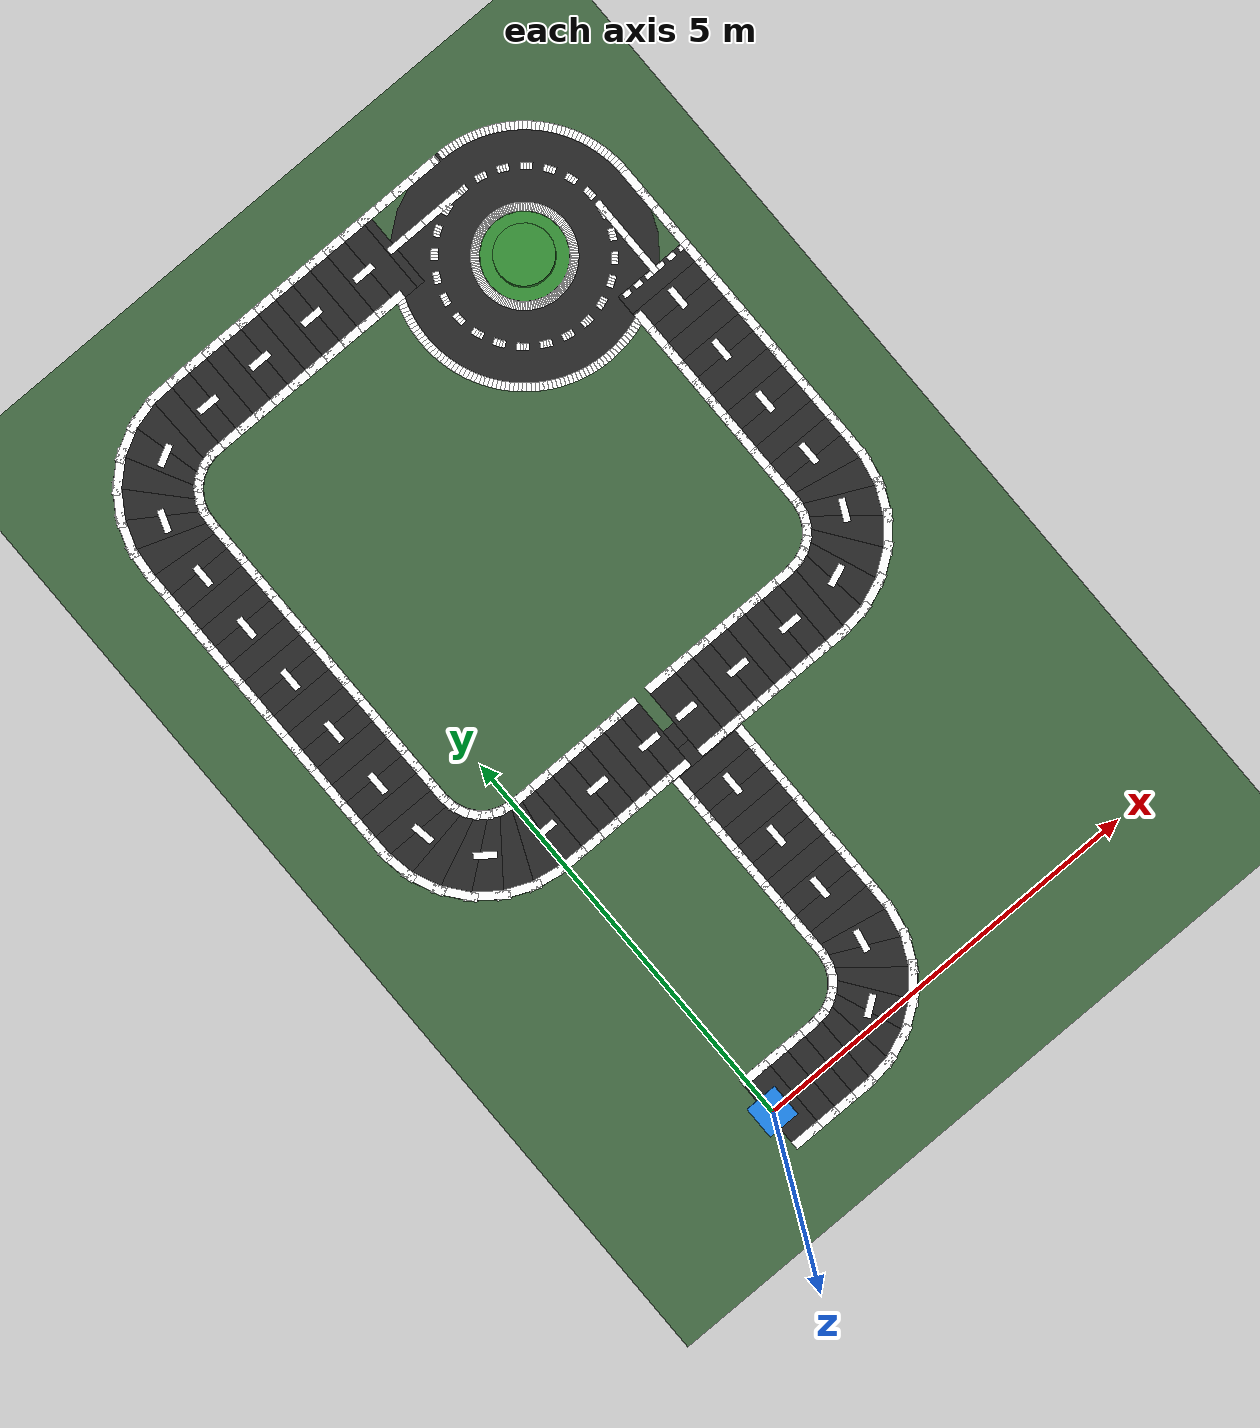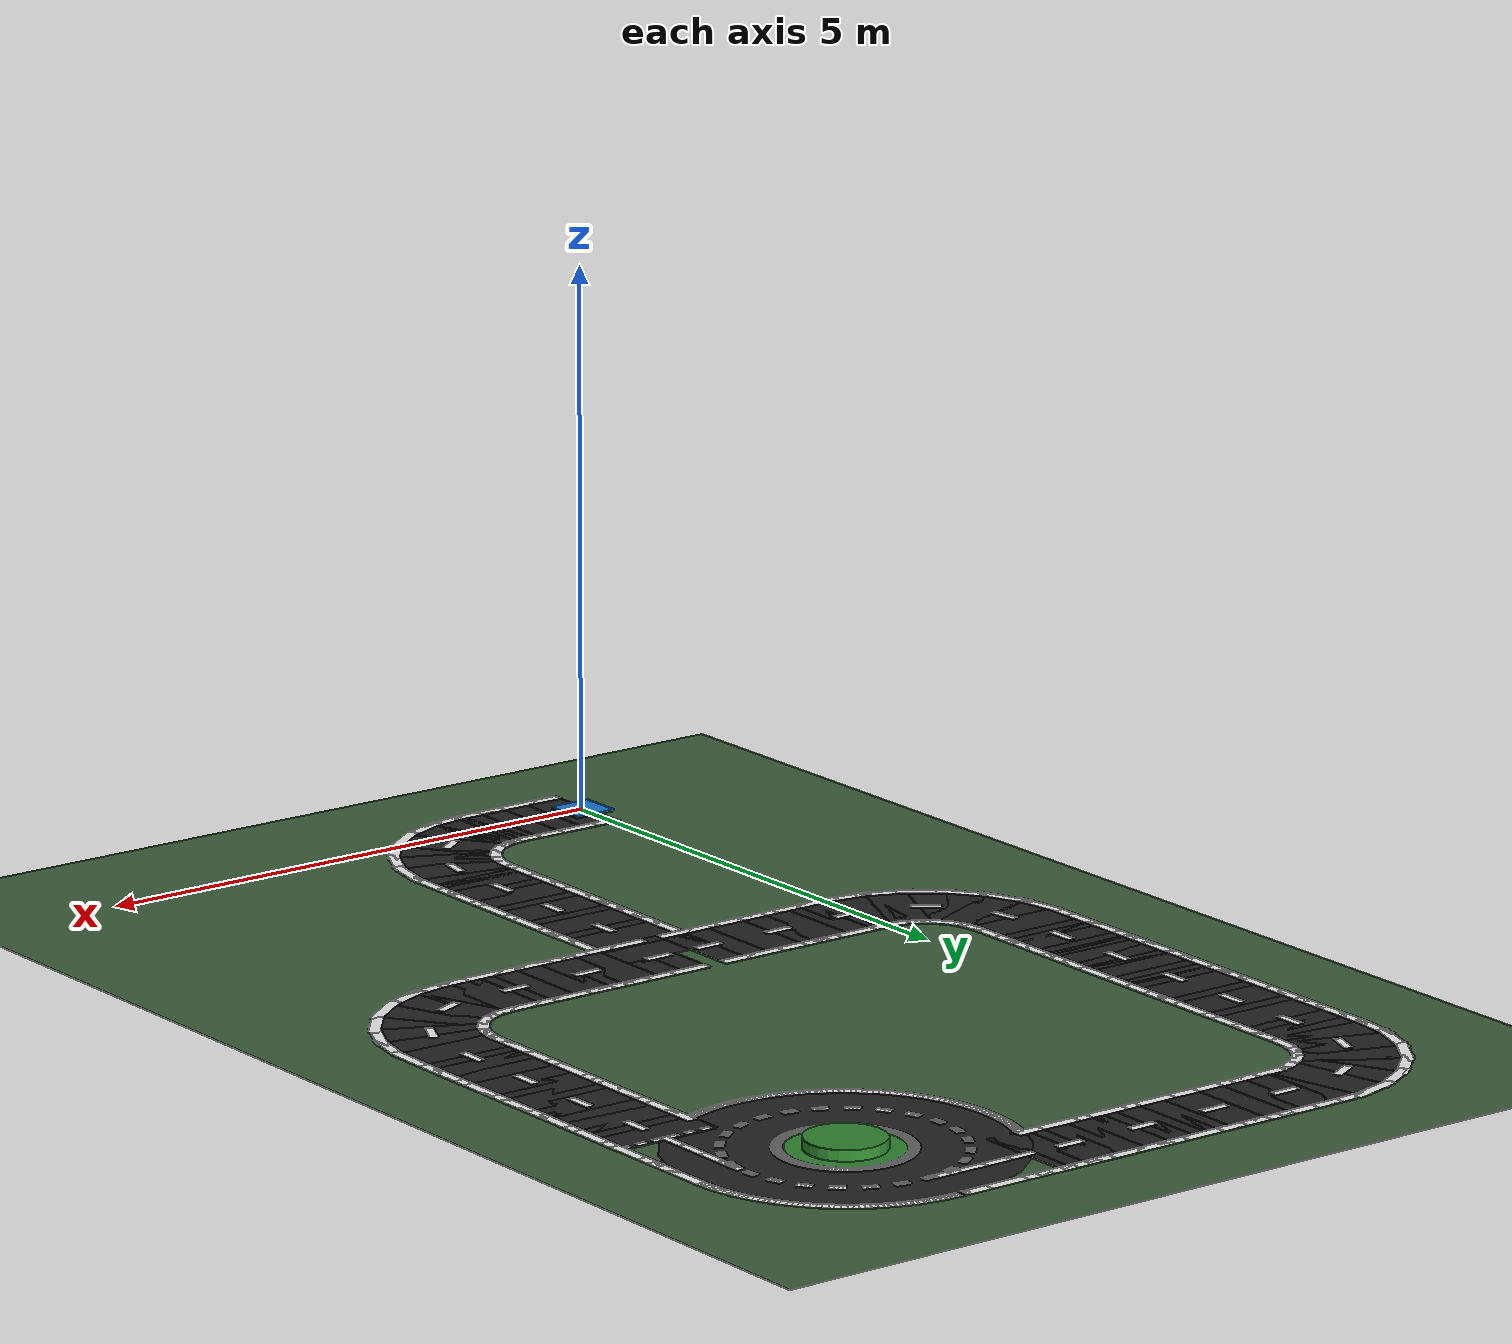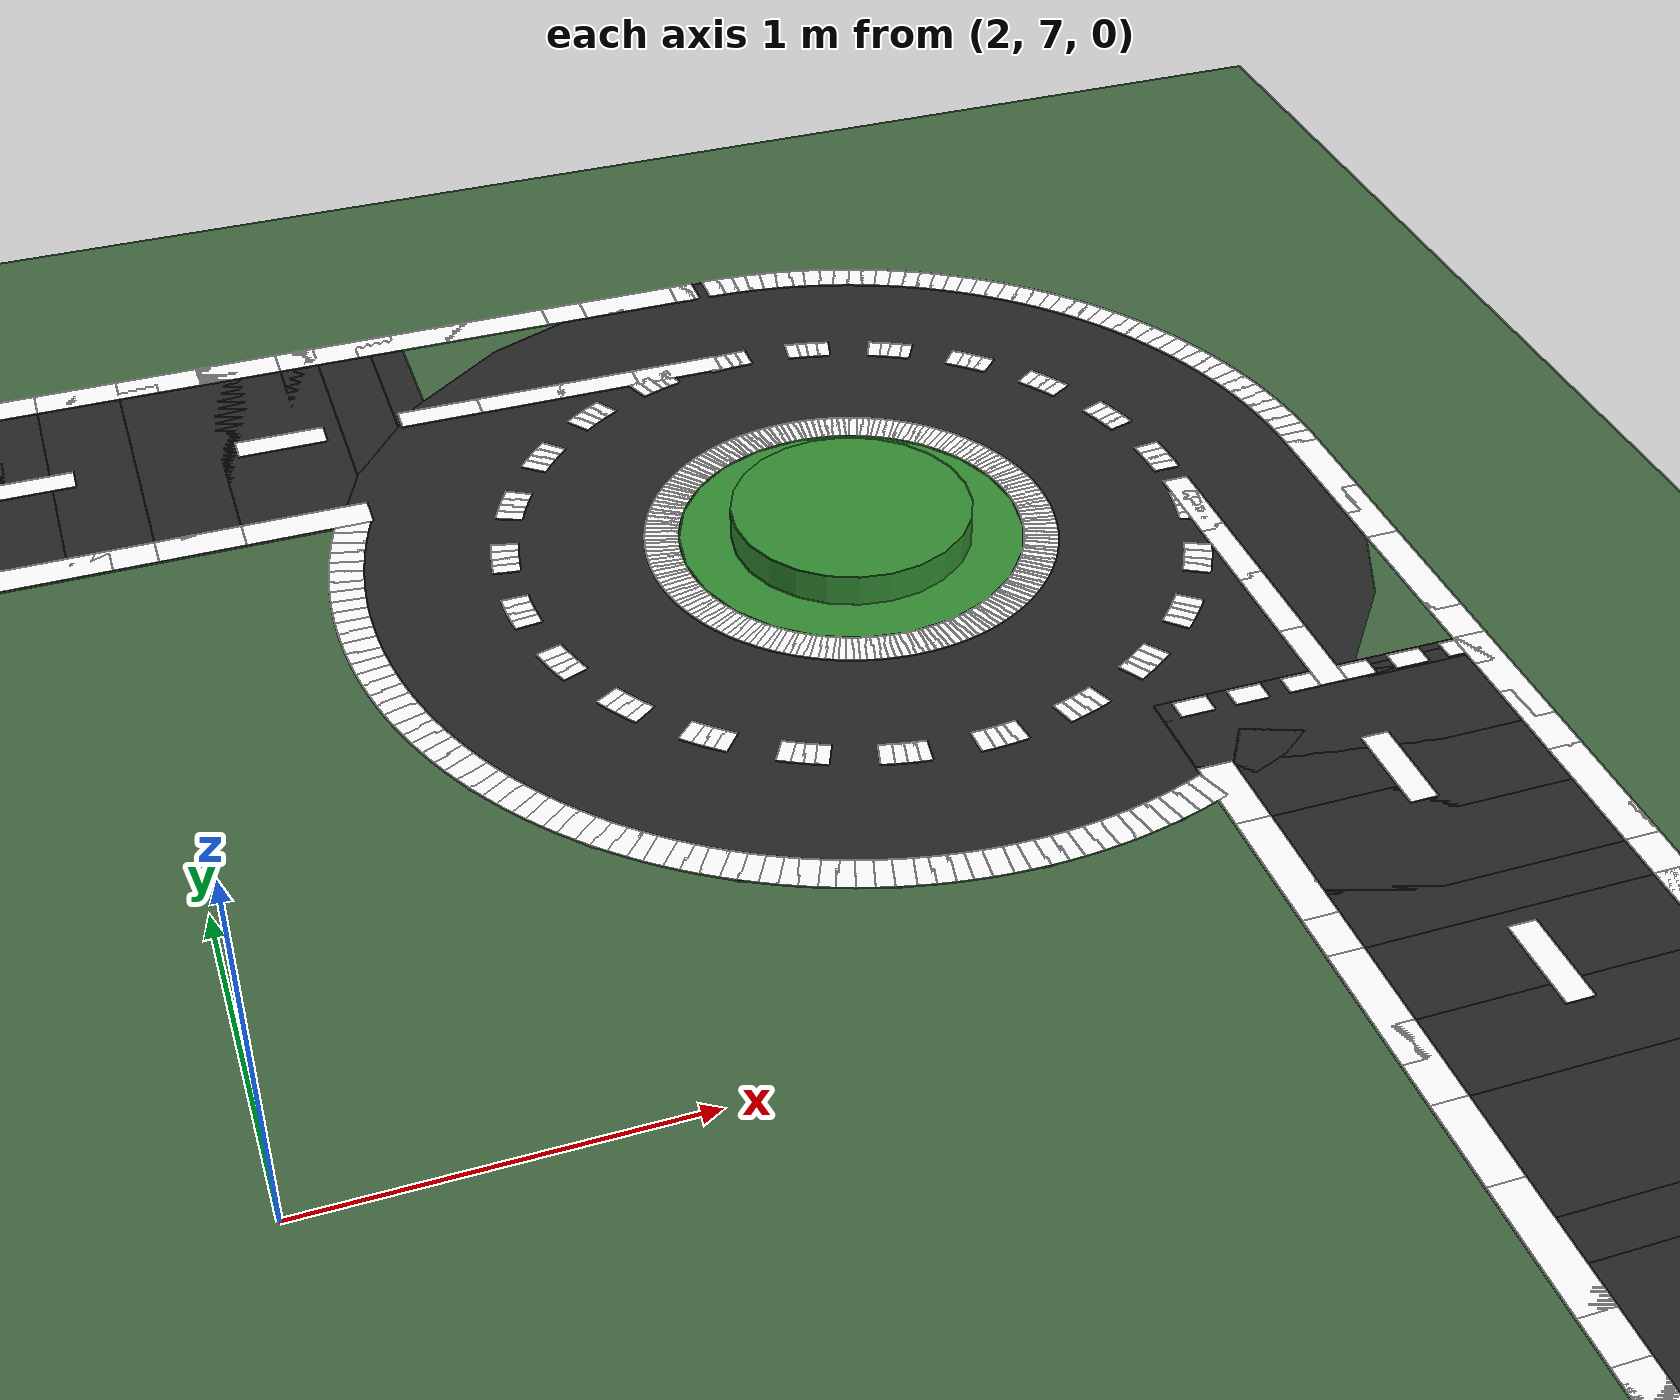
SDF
<?xml version="1.0" ?>
<sdf version="1.6">
  <world name="university_track">
    <physics name="1ms" type="ignored">
      <max_step_size>0.001</max_step_size>
      <real_time_factor>1.0</real_time_factor>
    </physics>
    <plugin filename="gz-sim-physics-system"           name="gz::sim::systems::Physics"/>
    <plugin filename="gz-sim-user-commands-system"     name="gz::sim::systems::UserCommands"/>
    <plugin filename="gz-sim-scene-broadcaster-system" name="gz::sim::systems::SceneBroadcaster"/>
    <plugin filename="gz-sim-sensors-system"           name="gz::sim::systems::Sensors">
      <render_engine>ogre2</render_engine>
    </plugin>
    <plugin filename="gz-sim-imu-system"               name="gz::sim::systems::Imu"/>
    <plugin filename="gz-sim-contact-system"           name="gz::sim::systems::Contact"/>
    <light type="directional" name="sun">
      <cast_shadows>true</cast_shadows>
      <pose>0 0 20 0 0 0</pose>
      <diffuse>0.9 0.9 0.9 1</diffuse>
      <specular>0.3 0.3 0.3 1</specular>
      <attenuation><range>1000</range><constant>0.9</constant><linear>0.01</linear><quadratic>0.001</quadratic></attenuation>
      <direction>-0.3 0.1 -0.9</direction>
    </light>
    <model name="ground_plane">
      <static>true</static>
      <link name="link">
        <collision name="collision"><geometry><plane><normal>0 0 1</normal><size>200 200</size></plane></geometry></collision>
        <visual name="visual"><geometry><plane><normal>0 0 1</normal><size>200 200</size></plane></geometry>
          <material><ambient>0.25 0.40 0.25 1</ambient><diffuse>0.25 0.40 0.25 1</diffuse></material></visual>
      </link>
    </model>
    <model name="loop_0_0"><static>true</static><pose>2.1250 4.0000 0.0020 0 0 0.00000</pose><link name="l"><visual name="v"><geometry><box><size>0.3700 1.0000 0.0020</size></box></geometry><material><ambient>0.15 0.15 0.15 1</ambient><diffuse>0.15 0.15 0.15 1</diffuse></material></visual></link></model>
    <model name="loop_1_0"><static>true</static><pose>2.3750 4.0000 0.0020 0 0 0.00000</pose><link name="l"><visual name="v"><geometry><box><size>0.3700 1.0000 0.0020</size></box></geometry><material><ambient>0.15 0.15 0.15 1</ambient><diffuse>0.15 0.15 0.15 1</diffuse></material></visual></link></model>
    <model name="loop_2_0"><static>true</static><pose>2.6250 4.0000 0.0020 0 0 0.00000</pose><link name="l"><visual name="v"><geometry><box><size>0.3700 1.0000 0.0020</size></box></geometry><material><ambient>0.15 0.15 0.15 1</ambient><diffuse>0.15 0.15 0.15 1</diffuse></material></visual></link></model>
    <model name="loop_3_0"><static>true</static><pose>2.8750 4.0000 0.0020 0 0 0.00000</pose><link name="l"><visual name="v"><geometry><box><size>0.3700 1.0000 0.0020</size></box></geometry><material><ambient>0.15 0.15 0.15 1</ambient><diffuse>0.15 0.15 0.15 1</diffuse></material></visual></link></model>
    <model name="loop_4_0"><static>true</static><pose>3.1250 4.0000 0.0020 0 0 0.00000</pose><link name="l"><visual name="v"><geometry><box><size>0.3700 1.0000 0.0020</size></box></geometry><material><ambient>0.15 0.15 0.15 1</ambient><diffuse>0.15 0.15 0.15 1</diffuse></material></visual></link></model>
    <model name="loop_5_0"><static>true</static><pose>3.3750 4.0000 0.0020 0 0 0.00000</pose><link name="l"><visual name="v"><geometry><box><size>0.3700 1.0000 0.0020</size></box></geometry><material><ambient>0.15 0.15 0.15 1</ambient><diffuse>0.15 0.15 0.15 1</diffuse></material></visual></link></model>
    <model name="loop_6_0"><static>true</static><pose>3.6250 4.0000 0.0020 0 0 0.00000</pose><link name="l"><visual name="v"><geometry><box><size>0.3700 1.0000 0.0020</size></box></geometry><material><ambient>0.15 0.15 0.15 1</ambient><diffuse>0.15 0.15 0.15 1</diffuse></material></visual></link></model>
    <model name="loop_7_0"><static>true</static><pose>3.8750 4.0000 0.0020 0 0 0.00000</pose><link name="l"><visual name="v"><geometry><box><size>0.3700 1.0000 0.0020</size></box></geometry><material><ambient>0.15 0.15 0.15 1</ambient><diffuse>0.15 0.15 0.15 1</diffuse></material></visual></link></model>
    <model name="loop_8_0"><static>true</static><pose>4.1236 4.0162 0.0020 0 0 0.13023</pose><link name="l"><visual name="v"><geometry><box><size>0.3690 1.0000 0.0020</size></box></geometry><material><ambient>0.15 0.15 0.15 1</ambient><diffuse>0.15 0.15 0.15 1</diffuse></material></visual></link></model>
    <model name="loop_9_0"><static>true</static><pose>4.3632 4.0779 0.0020 0 0 0.37377</pose><link name="l"><visual name="v"><geometry><box><size>0.3689 1.0000 0.0020</size></box></geometry><material><ambient>0.15 0.15 0.15 1</ambient><diffuse>0.15 0.15 0.15 1</diffuse></material></visual></link></model>
    <model name="loop_10_0"><static>true</static><pose>4.5803 4.1962 0.0020 0 0 0.62451</pose><link name="l"><visual name="v"><geometry><box><size>0.3689 1.0000 0.0020</size></box></geometry><material><ambient>0.15 0.15 0.15 1</ambient><diffuse>0.15 0.15 0.15 1</diffuse></material></visual></link></model>
    <model name="loop_11_0"><static>true</static><pose>4.7610 4.3650 0.0020 0 0 0.87778</pose><link name="l"><visual name="v"><geometry><box><size>0.3689 1.0000 0.0020</size></box></geometry><material><ambient>0.15 0.15 0.15 1</ambient><diffuse>0.15 0.15 0.15 1</diffuse></material></visual></link></model>
    <model name="loop_12_0"><static>true</static><pose>4.8947 4.5731 0.0020 0 0 1.12132</pose><link name="l"><visual name="v"><geometry><box><size>0.3690 1.0000 0.0020</size></box></geometry><material><ambient>0.15 0.15 0.15 1</ambient><diffuse>0.15 0.15 0.15 1</diffuse></material></visual></link></model>
    <model name="loop_13_0"><static>true</static><pose>4.9726 4.8077 0.0020 0 0 1.37926</pose><link name="l"><visual name="v"><geometry><box><size>0.3690 1.0000 0.0020</size></box></geometry><material><ambient>0.15 0.15 0.15 1</ambient><diffuse>0.15 0.15 0.15 1</diffuse></material></visual></link></model>
    <model name="loop_14_0"><static>true</static><pose>4.9982 5.0550 0.0020 0 0 1.55612</pose><link name="l"><visual name="v"><geometry><box><size>0.3699 1.0000 0.0020</size></box></geometry><material><ambient>0.15 0.15 0.15 1</ambient><diffuse>0.15 0.15 0.15 1</diffuse></material></visual></link></model>
    <model name="loop_15_0"><static>true</static><pose>5.0000 5.3049 0.0020 0 0 1.57080</pose><link name="l"><visual name="v"><geometry><box><size>0.3700 1.0000 0.0020</size></box></geometry><material><ambient>0.15 0.15 0.15 1</ambient><diffuse>0.15 0.15 0.15 1</diffuse></material></visual></link></model>
    <model name="loop_16_0"><static>true</static><pose>5.0000 5.5549 0.0020 0 0 1.57080</pose><link name="l"><visual name="v"><geometry><box><size>0.3700 1.0000 0.0020</size></box></geometry><material><ambient>0.15 0.15 0.15 1</ambient><diffuse>0.15 0.15 0.15 1</diffuse></material></visual></link></model>
    <model name="loop_17_0"><static>true</static><pose>5.0000 5.8049 0.0020 0 0 1.57080</pose><link name="l"><visual name="v"><geometry><box><size>0.3700 1.0000 0.0020</size></box></geometry><material><ambient>0.15 0.15 0.15 1</ambient><diffuse>0.15 0.15 0.15 1</diffuse></material></visual></link></model>
    <model name="loop_18_0"><static>true</static><pose>5.0000 6.0549 0.0020 0 0 1.57080</pose><link name="l"><visual name="v"><geometry><box><size>0.3700 1.0000 0.0020</size></box></geometry><material><ambient>0.15 0.15 0.15 1</ambient><diffuse>0.15 0.15 0.15 1</diffuse></material></visual></link></model>
    <model name="loop_19_0"><static>true</static><pose>5.0000 6.3049 0.0020 0 0 1.57080</pose><link name="l"><visual name="v"><geometry><box><size>0.3700 1.0000 0.0020</size></box></geometry><material><ambient>0.15 0.15 0.15 1</ambient><diffuse>0.15 0.15 0.15 1</diffuse></material></visual></link></model>
    <model name="loop_20_0"><static>true</static><pose>5.0000 6.5549 0.0020 0 0 1.57080</pose><link name="l"><visual name="v"><geometry><box><size>0.3700 1.0000 0.0020</size></box></geometry><material><ambient>0.15 0.15 0.15 1</ambient><diffuse>0.15 0.15 0.15 1</diffuse></material></visual></link></model>
    <model name="loop_21_0"><static>true</static><pose>5.0000 6.8049 0.0020 0 0 1.57080</pose><link name="l"><visual name="v"><geometry><box><size>0.3700 1.0000 0.0020</size></box></geometry><material><ambient>0.15 0.15 0.15 1</ambient><diffuse>0.15 0.15 0.15 1</diffuse></material></visual></link></model>
    <model name="loop_22_0"><static>true</static><pose>5.0000 7.0549 0.0020 0 0 1.57080</pose><link name="l"><visual name="v"><geometry><box><size>0.3700 1.0000 0.0020</size></box></geometry><material><ambient>0.15 0.15 0.15 1</ambient><diffuse>0.15 0.15 0.15 1</diffuse></material></visual></link></model>
    <model name="loop_23_0"><static>true</static><pose>5.0000 7.3049 0.0020 0 0 1.57080</pose><link name="l"><visual name="v"><geometry><box><size>0.3700 1.0000 0.0020</size></box></geometry><material><ambient>0.15 0.15 0.15 1</ambient><diffuse>0.15 0.15 0.15 1</diffuse></material></visual></link></model>
    <model name="loop_24_0"><static>true</static><pose>5.0000 7.5549 0.0020 0 0 1.57080</pose><link name="l"><visual name="v"><geometry><box><size>0.3700 1.0000 0.0020</size></box></geometry><material><ambient>0.15 0.15 0.15 1</ambient><diffuse>0.15 0.15 0.15 1</diffuse></material></visual></link></model>
    <model name="loop_25_0"><static>true</static><pose>5.0000 7.8049 0.0020 0 0 1.57080</pose><link name="l"><visual name="v"><geometry><box><size>0.3700 1.0000 0.0020</size></box></geometry><material><ambient>0.15 0.15 0.15 1</ambient><diffuse>0.15 0.15 0.15 1</diffuse></material></visual></link></model>
    <model name="loop_26_0"><static>true</static><pose>5.0000 7.9400 0.0020 0 0 1.57080</pose><link name="l"><visual name="v"><geometry><box><size>0.0481 1.0000 0.0020</size></box></geometry><material><ambient>0.15 0.15 0.15 1</ambient><diffuse>0.15 0.15 0.15 1</diffuse></material></visual></link></model>
    <model name="loop_40_0"><static>true</static><pose>2.9201 10.0000 0.0020 0 0 3.14159</pose><link name="l"><visual name="v"><geometry><box><size>0.1037 1.0000 0.0020</size></box></geometry><material><ambient>0.15 0.15 0.15 1</ambient><diffuse>0.15 0.15 0.15 1</diffuse></material></visual></link></model>
    <model name="loop_41_0"><static>true</static><pose>2.7652 10.0000 0.0020 0 0 3.14159</pose><link name="l"><visual name="v"><geometry><box><size>0.3700 1.0000 0.0020</size></box></geometry><material><ambient>0.15 0.15 0.15 1</ambient><diffuse>0.15 0.15 0.15 1</diffuse></material></visual></link></model>
    <model name="loop_42_0"><static>true</static><pose>2.5152 10.0000 0.0020 0 0 3.14159</pose><link name="l"><visual name="v"><geometry><box><size>0.3700 1.0000 0.0020</size></box></geometry><material><ambient>0.15 0.15 0.15 1</ambient><diffuse>0.15 0.15 0.15 1</diffuse></material></visual></link></model>
    <model name="loop_43_0"><static>true</static><pose>2.2652 10.0000 0.0020 0 0 3.14159</pose><link name="l"><visual name="v"><geometry><box><size>0.3700 1.0000 0.0020</size></box></geometry><material><ambient>0.15 0.15 0.15 1</ambient><diffuse>0.15 0.15 0.15 1</diffuse></material></visual></link></model>
    <model name="loop_44_0"><static>true</static><pose>2.0152 10.0000 0.0020 0 0 3.14159</pose><link name="l"><visual name="v"><geometry><box><size>0.3700 1.0000 0.0020</size></box></geometry><material><ambient>0.15 0.15 0.15 1</ambient><diffuse>0.15 0.15 0.15 1</diffuse></material></visual></link></model>
    <model name="loop_45_0"><static>true</static><pose>1.7652 10.0000 0.0020 0 0 3.14159</pose><link name="l"><visual name="v"><geometry><box><size>0.3700 1.0000 0.0020</size></box></geometry><material><ambient>0.15 0.15 0.15 1</ambient><diffuse>0.15 0.15 0.15 1</diffuse></material></visual></link></model>
    <model name="loop_46_0"><static>true</static><pose>1.5152 10.0000 0.0020 0 0 3.14159</pose><link name="l"><visual name="v"><geometry><box><size>0.3700 1.0000 0.0020</size></box></geometry><material><ambient>0.15 0.15 0.15 1</ambient><diffuse>0.15 0.15 0.15 1</diffuse></material></visual></link></model>
    <model name="loop_47_0"><static>true</static><pose>1.2652 10.0000 0.0020 0 0 3.14159</pose><link name="l"><visual name="v"><geometry><box><size>0.3700 1.0000 0.0020</size></box></geometry><material><ambient>0.15 0.15 0.15 1</ambient><diffuse>0.15 0.15 0.15 1</diffuse></material></visual></link></model>
    <model name="loop_48_0"><static>true</static><pose>1.0152 10.0000 0.0020 0 0 3.14159</pose><link name="l"><visual name="v"><geometry><box><size>0.3700 1.0000 0.0020</size></box></geometry><material><ambient>0.15 0.15 0.15 1</ambient><diffuse>0.15 0.15 0.15 1</diffuse></material></visual></link></model>
    <model name="loop_49_0"><static>true</static><pose>0.7652 10.0000 0.0020 0 0 3.14159</pose><link name="l"><visual name="v"><geometry><box><size>0.3700 1.0000 0.0020</size></box></geometry><material><ambient>0.15 0.15 0.15 1</ambient><diffuse>0.15 0.15 0.15 1</diffuse></material></visual></link></model>
    <model name="loop_50_0"><static>true</static><pose>0.5152 10.0000 0.0020 0 0 3.14159</pose><link name="l"><visual name="v"><geometry><box><size>0.3700 1.0000 0.0020</size></box></geometry><material><ambient>0.15 0.15 0.15 1</ambient><diffuse>0.15 0.15 0.15 1</diffuse></material></visual></link></model>
    <model name="loop_51_0"><static>true</static><pose>0.2652 10.0000 0.0020 0 0 3.14159</pose><link name="l"><visual name="v"><geometry><box><size>0.3700 1.0000 0.0020</size></box></geometry><material><ambient>0.15 0.15 0.15 1</ambient><diffuse>0.15 0.15 0.15 1</diffuse></material></visual></link></model>
    <model name="loop_52_0"><static>true</static><pose>0.0153 9.9969 0.0020 0 0 -3.11645</pose><link name="l"><visual name="v"><geometry><box><size>0.3698 1.0000 0.0020</size></box></geometry><material><ambient>0.15 0.15 0.15 1</ambient><diffuse>0.15 0.15 0.15 1</diffuse></material></visual></link></model>
    <model name="loop_53_0"><static>true</static><pose>-0.2307 9.9642 0.0020 0 0 -2.90233</pose><link name="l"><visual name="v"><geometry><box><size>0.3690 1.0000 0.0020</size></box></geometry><material><ambient>0.15 0.15 0.15 1</ambient><diffuse>0.15 0.15 0.15 1</diffuse></material></visual></link></model>
    <model name="loop_54_0"><static>true</static><pose>-0.4621 9.8768 0.0020 0 0 -2.65879</pose><link name="l"><visual name="v"><geometry><box><size>0.3689 1.0000 0.0020</size></box></geometry><material><ambient>0.15 0.15 0.15 1</ambient><diffuse>0.15 0.15 0.15 1</diffuse></material></visual></link></model>
    <model name="loop_55_0"><static>true</static><pose>-0.6649 9.7353 0.0020 0 0 -2.40591</pose><link name="l"><visual name="v"><geometry><box><size>0.3689 1.0000 0.0020</size></box></geometry><material><ambient>0.15 0.15 0.15 1</ambient><diffuse>0.15 0.15 0.15 1</diffuse></material></visual></link></model>
    <model name="loop_56_0"><static>true</static><pose>-0.8260 9.5477 0.0020 0 0 -2.15479</pose><link name="l"><visual name="v"><geometry><box><size>0.3689 1.0000 0.0020</size></box></geometry><material><ambient>0.15 0.15 0.15 1</ambient><diffuse>0.15 0.15 0.15 1</diffuse></material></visual></link></model>
    <model name="loop_57_0"><static>true</static><pose>-0.9363 9.3263 0.0020 0 0 -1.91125</pose><link name="l"><visual name="v"><geometry><box><size>0.3690 1.0000 0.0020</size></box></geometry><material><ambient>0.15 0.15 0.15 1</ambient><diffuse>0.15 0.15 0.15 1</diffuse></material></visual></link></model>
    <model name="loop_58_0"><static>true</static><pose>-0.9890 9.0845 0.0020 0 0 -1.65945</pose><link name="l"><visual name="v"><geometry><box><size>0.3693 1.0000 0.0020</size></box></geometry><material><ambient>0.15 0.15 0.15 1</ambient><diffuse>0.15 0.15 0.15 1</diffuse></material></visual></link></model>
    <model name="loop_59_0"><static>true</static><pose>-1.0000 8.8353 0.0020 0 0 -1.57080</pose><link name="l"><visual name="v"><geometry><box><size>0.3700 1.0000 0.0020</size></box></geometry><material><ambient>0.15 0.15 0.15 1</ambient><diffuse>0.15 0.15 0.15 1</diffuse></material></visual></link></model>
    <model name="loop_60_0"><static>true</static><pose>-1.0000 8.5853 0.0020 0 0 -1.57080</pose><link name="l"><visual name="v"><geometry><box><size>0.3700 1.0000 0.0020</size></box></geometry><material><ambient>0.15 0.15 0.15 1</ambient><diffuse>0.15 0.15 0.15 1</diffuse></material></visual></link></model>
    <model name="loop_61_0"><static>true</static><pose>-1.0000 8.3353 0.0020 0 0 -1.57080</pose><link name="l"><visual name="v"><geometry><box><size>0.3700 1.0000 0.0020</size></box></geometry><material><ambient>0.15 0.15 0.15 1</ambient><diffuse>0.15 0.15 0.15 1</diffuse></material></visual></link></model>
    <model name="loop_62_0"><static>true</static><pose>-1.0000 8.0853 0.0020 0 0 -1.57080</pose><link name="l"><visual name="v"><geometry><box><size>0.3700 1.0000 0.0020</size></box></geometry><material><ambient>0.15 0.15 0.15 1</ambient><diffuse>0.15 0.15 0.15 1</diffuse></material></visual></link></model>
    <model name="loop_63_0"><static>true</static><pose>-1.0000 7.8353 0.0020 0 0 -1.57080</pose><link name="l"><visual name="v"><geometry><box><size>0.3700 1.0000 0.0020</size></box></geometry><material><ambient>0.15 0.15 0.15 1</ambient><diffuse>0.15 0.15 0.15 1</diffuse></material></visual></link></model>
    <model name="loop_64_0"><static>true</static><pose>-1.0000 7.5853 0.0020 0 0 -1.57080</pose><link name="l"><visual name="v"><geometry><box><size>0.3700 1.0000 0.0020</size></box></geometry><material><ambient>0.15 0.15 0.15 1</ambient><diffuse>0.15 0.15 0.15 1</diffuse></material></visual></link></model>
    <model name="loop_65_0"><static>true</static><pose>-1.0000 7.3353 0.0020 0 0 -1.57080</pose><link name="l"><visual name="v"><geometry><box><size>0.3700 1.0000 0.0020</size></box></geometry><material><ambient>0.15 0.15 0.15 1</ambient><diffuse>0.15 0.15 0.15 1</diffuse></material></visual></link></model>
    <model name="loop_66_0"><static>true</static><pose>-1.0000 7.0853 0.0020 0 0 -1.57080</pose><link name="l"><visual name="v"><geometry><box><size>0.3700 1.0000 0.0020</size></box></geometry><material><ambient>0.15 0.15 0.15 1</ambient><diffuse>0.15 0.15 0.15 1</diffuse></material></visual></link></model>
    <model name="loop_67_0"><static>true</static><pose>-1.0000 6.8353 0.0020 0 0 -1.57080</pose><link name="l"><visual name="v"><geometry><box><size>0.3700 1.0000 0.0020</size></box></geometry><material><ambient>0.15 0.15 0.15 1</ambient><diffuse>0.15 0.15 0.15 1</diffuse></material></visual></link></model>
    <model name="loop_68_0"><static>true</static><pose>-1.0000 6.5853 0.0020 0 0 -1.57080</pose><link name="l"><visual name="v"><geometry><box><size>0.3700 1.0000 0.0020</size></box></geometry><material><ambient>0.15 0.15 0.15 1</ambient><diffuse>0.15 0.15 0.15 1</diffuse></material></visual></link></model>
    <model name="loop_69_0"><static>true</static><pose>-1.0000 6.3353 0.0020 0 0 -1.57080</pose><link name="l"><visual name="v"><geometry><box><size>0.3700 1.0000 0.0020</size></box></geometry><material><ambient>0.15 0.15 0.15 1</ambient><diffuse>0.15 0.15 0.15 1</diffuse></material></visual></link></model>
    <model name="loop_70_0"><static>true</static><pose>-1.0000 6.0853 0.0020 0 0 -1.57080</pose><link name="l"><visual name="v"><geometry><box><size>0.3700 1.0000 0.0020</size></box></geometry><material><ambient>0.15 0.15 0.15 1</ambient><diffuse>0.15 0.15 0.15 1</diffuse></material></visual></link></model>
    <model name="loop_71_0"><static>true</static><pose>-1.0000 5.8353 0.0020 0 0 -1.57080</pose><link name="l"><visual name="v"><geometry><box><size>0.3700 1.0000 0.0020</size></box></geometry><material><ambient>0.15 0.15 0.15 1</ambient><diffuse>0.15 0.15 0.15 1</diffuse></material></visual></link></model>
    <model name="loop_72_0"><static>true</static><pose>-1.0000 5.5853 0.0020 0 0 -1.57080</pose><link name="l"><visual name="v"><geometry><box><size>0.3700 1.0000 0.0020</size></box></geometry><material><ambient>0.15 0.15 0.15 1</ambient><diffuse>0.15 0.15 0.15 1</diffuse></material></visual></link></model>
    <model name="loop_73_0"><static>true</static><pose>-1.0000 5.3353 0.0020 0 0 -1.57080</pose><link name="l"><visual name="v"><geometry><box><size>0.3700 1.0000 0.0020</size></box></geometry><material><ambient>0.15 0.15 0.15 1</ambient><diffuse>0.15 0.15 0.15 1</diffuse></material></visual></link></model>
    <model name="loop_74_0"><static>true</static><pose>-0.9995 5.0853 0.0020 0 0 -1.56664</pose><link name="l"><visual name="v"><geometry><box><size>0.3700 1.0000 0.0020</size></box></geometry><material><ambient>0.15 0.15 0.15 1</ambient><diffuse>0.15 0.15 0.15 1</diffuse></material></visual></link></model>
    <model name="loop_75_0"><static>true</static><pose>-0.9781 4.8374 0.0020 0 0 -1.40274</pose><link name="l"><visual name="v"><geometry><box><size>0.3690 1.0000 0.0020</size></box></geometry><material><ambient>0.15 0.15 0.15 1</ambient><diffuse>0.15 0.15 0.15 1</diffuse></material></visual></link></model>
    <model name="loop_76_0"><static>true</static><pose>-0.9070 4.6005 0.0020 0 0 -1.15525</pose><link name="l"><visual name="v"><geometry><box><size>0.3689 1.0000 0.0020</size></box></geometry><material><ambient>0.15 0.15 0.15 1</ambient><diffuse>0.15 0.15 0.15 1</diffuse></material></visual></link></model>
    <model name="loop_77_0"><static>true</static><pose>-0.7801 4.3881 0.0020 0 0 -0.90977</pose><link name="l"><visual name="v"><geometry><box><size>0.3690 1.0000 0.0020</size></box></geometry><material><ambient>0.15 0.15 0.15 1</ambient><diffuse>0.15 0.15 0.15 1</diffuse></material></visual></link></model>
    <model name="loop_78_0"><static>true</static><pose>-0.6045 4.2142 0.0020 0 0 -0.65125</pose><link name="l"><visual name="v"><geometry><box><size>0.3690 1.0000 0.0020</size></box></geometry><material><ambient>0.15 0.15 0.15 1</ambient><diffuse>0.15 0.15 0.15 1</diffuse></material></visual></link></model>
    <model name="loop_79_0"><static>true</static><pose>-0.3910 4.0893 0.0020 0 0 -0.40771</pose><link name="l"><visual name="v"><geometry><box><size>0.3689 1.0000 0.0020</size></box></geometry><material><ambient>0.15 0.15 0.15 1</ambient><diffuse>0.15 0.15 0.15 1</diffuse></material></visual></link></model>
    <model name="loop_80_0"><static>true</static><pose>-0.1535 4.0203 0.0020 0 0 -0.15731</pose><link name="l"><visual name="v"><geometry><box><size>0.3690 1.0000 0.0020</size></box></geometry><material><ambient>0.15 0.15 0.15 1</ambient><diffuse>0.15 0.15 0.15 1</diffuse></material></visual></link></model>
    <model name="loop_81_0"><static>true</static><pose>0.0946 4.0004 0.0020 0 0 -0.00318</pose><link name="l"><visual name="v"><geometry><box><size>0.3700 1.0000 0.0020</size></box></geometry><material><ambient>0.15 0.15 0.15 1</ambient><diffuse>0.15 0.15 0.15 1</diffuse></material></visual></link></model>
    <model name="loop_82_0"><static>true</static><pose>0.3446 4.0000 0.0020 0 0 0.00000</pose><link name="l"><visual name="v"><geometry><box><size>0.3700 1.0000 0.0020</size></box></geometry><material><ambient>0.15 0.15 0.15 1</ambient><diffuse>0.15 0.15 0.15 1</diffuse></material></visual></link></model>
    <model name="loop_83_0"><static>true</static><pose>0.5946 4.0000 0.0020 0 0 0.00000</pose><link name="l"><visual name="v"><geometry><box><size>0.3700 1.0000 0.0020</size></box></geometry><material><ambient>0.15 0.15 0.15 1</ambient><diffuse>0.15 0.15 0.15 1</diffuse></material></visual></link></model>
    <model name="loop_84_0"><static>true</static><pose>0.8446 4.0000 0.0020 0 0 -0.00000</pose><link name="l"><visual name="v"><geometry><box><size>0.3700 1.0000 0.0020</size></box></geometry><material><ambient>0.15 0.15 0.15 1</ambient><diffuse>0.15 0.15 0.15 1</diffuse></material></visual></link></model>
    <model name="loop_85_0"><static>true</static><pose>1.0946 4.0000 0.0020 0 0 0.00000</pose><link name="l"><visual name="v"><geometry><box><size>0.3700 1.0000 0.0020</size></box></geometry><material><ambient>0.15 0.15 0.15 1</ambient><diffuse>0.15 0.15 0.15 1</diffuse></material></visual></link></model>
    <model name="loop_86_0"><static>true</static><pose>1.3446 4.0000 0.0020 0 0 0.00000</pose><link name="l"><visual name="v"><geometry><box><size>0.3700 1.0000 0.0020</size></box></geometry><material><ambient>0.15 0.15 0.15 1</ambient><diffuse>0.15 0.15 0.15 1</diffuse></material></visual></link></model>
    <model name="loop_87_0"><static>true</static><pose>1.5946 4.0000 0.0020 0 0 0.00000</pose><link name="l"><visual name="v"><geometry><box><size>0.3700 1.0000 0.0020</size></box></geometry><material><ambient>0.15 0.15 0.15 1</ambient><diffuse>0.15 0.15 0.15 1</diffuse></material></visual></link></model>
    <model name="loop_le_0_0"><static>true</static><pose>2.1250 4.4500 0.0050 0 0 0.00000</pose><link name="l"><visual name="v"><geometry><box><size>0.3700 0.1000 0.0020</size></box></geometry><material><ambient>1.0 1.0 1.0 1</ambient><diffuse>1.0 1.0 1.0 1</diffuse></material></visual></link></model>
    <model name="loop_le_1_0"><static>true</static><pose>2.3750 4.4500 0.0050 0 0 0.00000</pose><link name="l"><visual name="v"><geometry><box><size>0.3700 0.1000 0.0020</size></box></geometry><material><ambient>1.0 1.0 1.0 1</ambient><diffuse>1.0 1.0 1.0 1</diffuse></material></visual></link></model>
    <model name="loop_le_2_0"><static>true</static><pose>2.6250 4.4500 0.0050 0 0 0.00000</pose><link name="l"><visual name="v"><geometry><box><size>0.3700 0.1000 0.0020</size></box></geometry><material><ambient>1.0 1.0 1.0 1</ambient><diffuse>1.0 1.0 1.0 1</diffuse></material></visual></link></model>
    <model name="loop_le_3_0"><static>true</static><pose>2.8750 4.4500 0.0050 0 0 0.00000</pose><link name="l"><visual name="v"><geometry><box><size>0.3700 0.1000 0.0020</size></box></geometry><material><ambient>1.0 1.0 1.0 1</ambient><diffuse>1.0 1.0 1.0 1</diffuse></material></visual></link></model>
    <model name="loop_le_4_0"><static>true</static><pose>3.1250 4.4500 0.0050 0 0 0.00000</pose><link name="l"><visual name="v"><geometry><box><size>0.3700 0.1000 0.0020</size></box></geometry><material><ambient>1.0 1.0 1.0 1</ambient><diffuse>1.0 1.0 1.0 1</diffuse></material></visual></link></model>
    <model name="loop_le_5_0"><static>true</static><pose>3.3750 4.4500 0.0050 0 0 0.00000</pose><link name="l"><visual name="v"><geometry><box><size>0.3700 0.1000 0.0020</size></box></geometry><material><ambient>1.0 1.0 1.0 1</ambient><diffuse>1.0 1.0 1.0 1</diffuse></material></visual></link></model>
    <model name="loop_le_6_0"><static>true</static><pose>3.6250 4.4500 0.0050 0 0 0.00000</pose><link name="l"><visual name="v"><geometry><box><size>0.3700 0.1000 0.0020</size></box></geometry><material><ambient>1.0 1.0 1.0 1</ambient><diffuse>1.0 1.0 1.0 1</diffuse></material></visual></link></model>
    <model name="loop_le_7_0"><static>true</static><pose>3.8604 4.4495 0.0050 0 0 -0.00431</pose><link name="l"><visual name="v"><geometry><box><size>0.3291 0.1000 0.0020</size></box></geometry><material><ambient>1.0 1.0 1.0 1</ambient><diffuse>1.0 1.0 1.0 1</diffuse></material></visual></link></model>
    <model name="loop_le_8_0"><static>true</static><pose>4.0529 4.4586 0.0050 0 0 0.11587</pose><link name="l"><visual name="v"><geometry><box><size>0.2515 0.1000 0.0020</size></box></geometry><material><ambient>1.0 1.0 1.0 1</ambient><diffuse>1.0 1.0 1.0 1</diffuse></material></visual></link></model>
    <model name="loop_le_9_0"><static>true</static><pose>4.1994 4.4933 0.0050 0 0 0.37234</pose><link name="l"><visual name="v"><geometry><box><size>0.2136 0.1000 0.0020</size></box></geometry><material><ambient>1.0 1.0 1.0 1</ambient><diffuse>1.0 1.0 1.0 1</diffuse></material></visual></link></model>
    <model name="loop_le_10_0"><static>true</static><pose>4.3190 4.5582 0.0050 0 0 0.62399</pose><link name="l"><visual name="v"><geometry><box><size>0.2106 0.1000 0.0020</size></box></geometry><material><ambient>1.0 1.0 1.0 1</ambient><diffuse>1.0 1.0 1.0 1</diffuse></material></visual></link></model>
    <model name="loop_le_11_0"><static>true</static><pose>4.4181 4.6511 0.0050 0 0 0.87974</pose><link name="l"><visual name="v"><geometry><box><size>0.2128 0.1000 0.0020</size></box></geometry><material><ambient>1.0 1.0 1.0 1</ambient><diffuse>1.0 1.0 1.0 1</diffuse></material></visual></link></model>
    <model name="loop_le_12_0"><static>true</static><pose>4.4919 4.7656 0.0050 0 0 1.11835</pose><link name="l"><visual name="v"><geometry><box><size>0.2114 0.1000 0.0020</size></box></geometry><material><ambient>1.0 1.0 1.0 1</ambient><diffuse>1.0 1.0 1.0 1</diffuse></material></visual></link></model>
    <model name="loop_le_13_0"><static>true</static><pose>4.5353 4.9017 0.0050 0 0 1.39229</pose><link name="l"><visual name="v"><geometry><box><size>0.2322 0.1000 0.0020</size></box></geometry><material><ambient>1.0 1.0 1.0 1</ambient><diffuse>1.0 1.0 1.0 1</diffuse></material></visual></link></model>
    <model name="loop_le_14_0"><static>true</static><pose>4.5494 5.0798 0.0050 0 0 1.56454</pose><link name="l"><visual name="v"><geometry><box><size>0.3097 0.1000 0.0020</size></box></geometry><material><ambient>1.0 1.0 1.0 1</ambient><diffuse>1.0 1.0 1.0 1</diffuse></material></visual></link></model>
    <model name="loop_le_15_0"><static>true</static><pose>4.5500 5.3066 0.0050 0 0 1.57085</pose><link name="l"><visual name="v"><geometry><box><size>0.3654 0.1000 0.0020</size></box></geometry><material><ambient>1.0 1.0 1.0 1</ambient><diffuse>1.0 1.0 1.0 1</diffuse></material></visual></link></model>
    <model name="loop_le_16_0"><static>true</static><pose>4.5500 5.5549 0.0050 0 0 1.57080</pose><link name="l"><visual name="v"><geometry><box><size>0.3700 0.1000 0.0020</size></box></geometry><material><ambient>1.0 1.0 1.0 1</ambient><diffuse>1.0 1.0 1.0 1</diffuse></material></visual></link></model>
    <model name="loop_le_17_0"><static>true</static><pose>4.5500 5.8049 0.0050 0 0 1.57080</pose><link name="l"><visual name="v"><geometry><box><size>0.3700 0.1000 0.0020</size></box></geometry><material><ambient>1.0 1.0 1.0 1</ambient><diffuse>1.0 1.0 1.0 1</diffuse></material></visual></link></model>
    <model name="loop_le_18_0"><static>true</static><pose>4.5500 6.0549 0.0050 0 0 1.57080</pose><link name="l"><visual name="v"><geometry><box><size>0.3700 0.1000 0.0020</size></box></geometry><material><ambient>1.0 1.0 1.0 1</ambient><diffuse>1.0 1.0 1.0 1</diffuse></material></visual></link></model>
    <model name="loop_le_19_0"><static>true</static><pose>4.5500 6.3049 0.0050 0 0 1.57080</pose><link name="l"><visual name="v"><geometry><box><size>0.3700 0.1000 0.0020</size></box></geometry><material><ambient>1.0 1.0 1.0 1</ambient><diffuse>1.0 1.0 1.0 1</diffuse></material></visual></link></model>
    <model name="loop_le_20_0"><static>true</static><pose>4.5500 6.5549 0.0050 0 0 1.57080</pose><link name="l"><visual name="v"><geometry><box><size>0.3700 0.1000 0.0020</size></box></geometry><material><ambient>1.0 1.0 1.0 1</ambient><diffuse>1.0 1.0 1.0 1</diffuse></material></visual></link></model>
    <model name="loop_le_21_0"><static>true</static><pose>4.5500 6.8049 0.0050 0 0 1.57080</pose><link name="l"><visual name="v"><geometry><box><size>0.3700 0.1000 0.0020</size></box></geometry><material><ambient>1.0 1.0 1.0 1</ambient><diffuse>1.0 1.0 1.0 1</diffuse></material></visual></link></model>
    <model name="loop_le_22_0"><static>true</static><pose>4.5500 7.0549 0.0050 0 0 1.57080</pose><link name="l"><visual name="v"><geometry><box><size>0.3700 0.1000 0.0020</size></box></geometry><material><ambient>1.0 1.0 1.0 1</ambient><diffuse>1.0 1.0 1.0 1</diffuse></material></visual></link></model>
    <model name="loop_le_23_0"><static>true</static><pose>4.5500 7.3049 0.0050 0 0 1.57080</pose><link name="l"><visual name="v"><geometry><box><size>0.3700 0.1000 0.0020</size></box></geometry><material><ambient>1.0 1.0 1.0 1</ambient><diffuse>1.0 1.0 1.0 1</diffuse></material></visual></link></model>
    <model name="loop_le_24_0"><static>true</static><pose>4.5500 7.5441 0.0050 0 0 1.57080</pose><link name="l"><visual name="v"><geometry><box><size>0.3398 0.1000 0.0020</size></box></geometry><material><ambient>1.0 1.0 1.0 1</ambient><diffuse>1.0 1.0 1.0 1</diffuse></material></visual></link></model>
    <model name="loop_le_42_0"><static>true</static><pose>2.5152 9.5500 0.0050 0 0 3.14159</pose><link name="l"><visual name="v"><geometry><box><size>0.3700 0.1000 0.0020</size></box></geometry><material><ambient>1.0 1.0 1.0 1</ambient><diffuse>1.0 1.0 1.0 1</diffuse></material></visual></link></model>
    <model name="loop_le_43_0"><static>true</static><pose>2.2652 9.5500 0.0050 0 0 3.14159</pose><link name="l"><visual name="v"><geometry><box><size>0.3700 0.1000 0.0020</size></box></geometry><material><ambient>1.0 1.0 1.0 1</ambient><diffuse>1.0 1.0 1.0 1</diffuse></material></visual></link></model>
    <model name="loop_le_44_0"><static>true</static><pose>2.0152 9.5500 0.0050 0 0 3.14159</pose><link name="l"><visual name="v"><geometry><box><size>0.3700 0.1000 0.0020</size></box></geometry><material><ambient>1.0 1.0 1.0 1</ambient><diffuse>1.0 1.0 1.0 1</diffuse></material></visual></link></model>
    <model name="loop_le_45_0"><static>true</static><pose>1.7652 9.5500 0.0050 0 0 3.14159</pose><link name="l"><visual name="v"><geometry><box><size>0.3700 0.1000 0.0020</size></box></geometry><material><ambient>1.0 1.0 1.0 1</ambient><diffuse>1.0 1.0 1.0 1</diffuse></material></visual></link></model>
    <model name="loop_le_46_0"><static>true</static><pose>1.5152 9.5500 0.0050 0 0 3.14159</pose><link name="l"><visual name="v"><geometry><box><size>0.3700 0.1000 0.0020</size></box></geometry><material><ambient>1.0 1.0 1.0 1</ambient><diffuse>1.0 1.0 1.0 1</diffuse></material></visual></link></model>
    <model name="loop_le_47_0"><static>true</static><pose>1.2652 9.5500 0.0050 0 0 3.14159</pose><link name="l"><visual name="v"><geometry><box><size>0.3700 0.1000 0.0020</size></box></geometry><material><ambient>1.0 1.0 1.0 1</ambient><diffuse>1.0 1.0 1.0 1</diffuse></material></visual></link></model>
    <model name="loop_le_48_0"><static>true</static><pose>1.0152 9.5500 0.0050 0 0 3.14159</pose><link name="l"><visual name="v"><geometry><box><size>0.3700 0.1000 0.0020</size></box></geometry><material><ambient>1.0 1.0 1.0 1</ambient><diffuse>1.0 1.0 1.0 1</diffuse></material></visual></link></model>
    <model name="loop_le_49_0"><static>true</static><pose>0.7652 9.5500 0.0050 0 0 3.14159</pose><link name="l"><visual name="v"><geometry><box><size>0.3700 0.1000 0.0020</size></box></geometry><material><ambient>1.0 1.0 1.0 1</ambient><diffuse>1.0 1.0 1.0 1</diffuse></material></visual></link></model>
    <model name="loop_le_50_0"><static>true</static><pose>0.5152 9.5500 0.0050 0 0 3.14159</pose><link name="l"><visual name="v"><geometry><box><size>0.3700 0.1000 0.0020</size></box></geometry><material><ambient>1.0 1.0 1.0 1</ambient><diffuse>1.0 1.0 1.0 1</diffuse></material></visual></link></model>
    <model name="loop_le_51_0"><static>true</static><pose>0.2680 9.5500 0.0050 0 0 3.14145</pose><link name="l"><visual name="v"><geometry><box><size>0.3621 0.1000 0.0020</size></box></geometry><material><ambient>1.0 1.0 1.0 1</ambient><diffuse>1.0 1.0 1.0 1</diffuse></material></visual></link></model>
    <model name="loop_le_52_0"><static>true</static><pose>0.0478 9.5488 0.0050 0 0 -3.12937</pose><link name="l"><visual name="v"><geometry><box><size>0.2947 0.1000 0.0020</size></box></geometry><material><ambient>1.0 1.0 1.0 1</ambient><diffuse>1.0 1.0 1.0 1</diffuse></material></visual></link></model>
    <model name="loop_le_53_0"><static>true</static><pose>-0.1216 9.5306 0.0050 0 0 -2.90745</pose><link name="l"><visual name="v"><geometry><box><size>0.2251 0.1000 0.0020</size></box></geometry><material><ambient>1.0 1.0 1.0 1</ambient><diffuse>1.0 1.0 1.0 1</diffuse></material></visual></link></model>
    <model name="loop_le_54_0"><static>true</static><pose>-0.2539 9.4818 0.0050 0 0 -2.66067</pose><link name="l"><visual name="v"><geometry><box><size>0.2129 0.1000 0.0020</size></box></geometry><material><ambient>1.0 1.0 1.0 1</ambient><diffuse>1.0 1.0 1.0 1</diffuse></material></visual></link></model>
    <model name="loop_le_55_0"><static>true</static><pose>-0.3654 9.4042 0.0050 0 0 -2.40555</pose><link name="l"><visual name="v"><geometry><box><size>0.2106 0.1000 0.0020</size></box></geometry><material><ambient>1.0 1.0 1.0 1</ambient><diffuse>1.0 1.0 1.0 1</diffuse></material></visual></link></model>
    <model name="loop_le_56_0"><static>true</static><pose>-0.4539 9.3008 0.0050 0 0 -2.15327</pose><link name="l"><visual name="v"><geometry><box><size>0.2135 0.1000 0.0020</size></box></geometry><material><ambient>1.0 1.0 1.0 1</ambient><diffuse>1.0 1.0 1.0 1</diffuse></material></visual></link></model>
    <model name="loop_le_57_0"><static>true</static><pose>-0.5151 9.1781 0.0050 0 0 -1.91294</pose><link name="l"><visual name="v"><geometry><box><size>0.2133 0.1000 0.0020</size></box></geometry><material><ambient>1.0 1.0 1.0 1</ambient><diffuse>1.0 1.0 1.0 1</diffuse></material></visual></link></model>
    <model name="loop_le_58_0"><static>true</static><pose>-0.5443 9.0267 0.0050 0 0 -1.64146</pose><link name="l"><visual name="v"><geometry><box><size>0.2623 0.1000 0.0020</size></box></geometry><material><ambient>1.0 1.0 1.0 1</ambient><diffuse>1.0 1.0 1.0 1</diffuse></material></visual></link></model>
    <model name="loop_le_59_0"><static>true</static><pose>-0.5502 8.8253 0.0050 0 0 -1.56888</pose><link name="l"><visual name="v"><geometry><box><size>0.3421 0.1000 0.0020</size></box></geometry><material><ambient>1.0 1.0 1.0 1</ambient><diffuse>1.0 1.0 1.0 1</diffuse></material></visual></link></model>
    <model name="loop_le_60_0"><static>true</static><pose>-0.5500 8.5853 0.0050 0 0 -1.57080</pose><link name="l"><visual name="v"><geometry><box><size>0.3700 0.1000 0.0020</size></box></geometry><material><ambient>1.0 1.0 1.0 1</ambient><diffuse>1.0 1.0 1.0 1</diffuse></material></visual></link></model>
    <model name="loop_le_61_0"><static>true</static><pose>-0.5500 8.3353 0.0050 0 0 -1.57080</pose><link name="l"><visual name="v"><geometry><box><size>0.3700 0.1000 0.0020</size></box></geometry><material><ambient>1.0 1.0 1.0 1</ambient><diffuse>1.0 1.0 1.0 1</diffuse></material></visual></link></model>
    <model name="loop_le_62_0"><static>true</static><pose>-0.5500 8.0853 0.0050 0 0 -1.57080</pose><link name="l"><visual name="v"><geometry><box><size>0.3700 0.1000 0.0020</size></box></geometry><material><ambient>1.0 1.0 1.0 1</ambient><diffuse>1.0 1.0 1.0 1</diffuse></material></visual></link></model>
    <model name="loop_le_63_0"><static>true</static><pose>-0.5500 7.8353 0.0050 0 0 -1.57080</pose><link name="l"><visual name="v"><geometry><box><size>0.3700 0.1000 0.0020</size></box></geometry><material><ambient>1.0 1.0 1.0 1</ambient><diffuse>1.0 1.0 1.0 1</diffuse></material></visual></link></model>
    <model name="loop_le_64_0"><static>true</static><pose>-0.5500 7.5853 0.0050 0 0 -1.57080</pose><link name="l"><visual name="v"><geometry><box><size>0.3700 0.1000 0.0020</size></box></geometry><material><ambient>1.0 1.0 1.0 1</ambient><diffuse>1.0 1.0 1.0 1</diffuse></material></visual></link></model>
    <model name="loop_le_65_0"><static>true</static><pose>-0.5500 7.3353 0.0050 0 0 -1.57080</pose><link name="l"><visual name="v"><geometry><box><size>0.3700 0.1000 0.0020</size></box></geometry><material><ambient>1.0 1.0 1.0 1</ambient><diffuse>1.0 1.0 1.0 1</diffuse></material></visual></link></model>
    <model name="loop_le_66_0"><static>true</static><pose>-0.5500 7.0853 0.0050 0 0 -1.57080</pose><link name="l"><visual name="v"><geometry><box><size>0.3700 0.1000 0.0020</size></box></geometry><material><ambient>1.0 1.0 1.0 1</ambient><diffuse>1.0 1.0 1.0 1</diffuse></material></visual></link></model>
    <model name="loop_le_67_0"><static>true</static><pose>-0.5500 6.8353 0.0050 0 0 -1.57080</pose><link name="l"><visual name="v"><geometry><box><size>0.3700 0.1000 0.0020</size></box></geometry><material><ambient>1.0 1.0 1.0 1</ambient><diffuse>1.0 1.0 1.0 1</diffuse></material></visual></link></model>
    <model name="loop_le_68_0"><static>true</static><pose>-0.5500 6.5853 0.0050 0 0 -1.57080</pose><link name="l"><visual name="v"><geometry><box><size>0.3700 0.1000 0.0020</size></box></geometry><material><ambient>1.0 1.0 1.0 1</ambient><diffuse>1.0 1.0 1.0 1</diffuse></material></visual></link></model>
    <model name="loop_le_69_0"><static>true</static><pose>-0.5500 6.3353 0.0050 0 0 -1.57080</pose><link name="l"><visual name="v"><geometry><box><size>0.3700 0.1000 0.0020</size></box></geometry><material><ambient>1.0 1.0 1.0 1</ambient><diffuse>1.0 1.0 1.0 1</diffuse></material></visual></link></model>
    <model name="loop_le_70_0"><static>true</static><pose>-0.5500 6.0853 0.0050 0 0 -1.57080</pose><link name="l"><visual name="v"><geometry><box><size>0.3700 0.1000 0.0020</size></box></geometry><material><ambient>1.0 1.0 1.0 1</ambient><diffuse>1.0 1.0 1.0 1</diffuse></material></visual></link></model>
    <model name="loop_le_71_0"><static>true</static><pose>-0.5500 5.8353 0.0050 0 0 -1.57080</pose><link name="l"><visual name="v"><geometry><box><size>0.3700 0.1000 0.0020</size></box></geometry><material><ambient>1.0 1.0 1.0 1</ambient><diffuse>1.0 1.0 1.0 1</diffuse></material></visual></link></model>
    <model name="loop_le_72_0"><static>true</static><pose>-0.5500 5.5853 0.0050 0 0 -1.57080</pose><link name="l"><visual name="v"><geometry><box><size>0.3700 0.1000 0.0020</size></box></geometry><material><ambient>1.0 1.0 1.0 1</ambient><diffuse>1.0 1.0 1.0 1</diffuse></material></visual></link></model>
    <model name="loop_le_73_0"><static>true</static><pose>-0.5500 5.3357 0.0050 0 0 -1.57080</pose><link name="l"><visual name="v"><geometry><box><size>0.3687 0.1000 0.0020</size></box></geometry><material><ambient>1.0 1.0 1.0 1</ambient><diffuse>1.0 1.0 1.0 1</diffuse></material></visual></link></model>
    <model name="loop_le_74_0"><static>true</static><pose>-0.5503 5.1051 0.0050 0 0 -1.57373</pose><link name="l"><visual name="v"><geometry><box><size>0.3172 0.1000 0.0020</size></box></geometry><material><ambient>1.0 1.0 1.0 1</ambient><diffuse>1.0 1.0 1.0 1</diffuse></material></visual></link></model>
    <model name="loop_le_75_0"><static>true</static><pose>-0.5385 4.9215 0.0050 0 0 -1.41501</pose><link name="l"><visual name="v"><geometry><box><size>0.2396 0.1000 0.0020</size></box></geometry><material><ambient>1.0 1.0 1.0 1</ambient><diffuse>1.0 1.0 1.0 1</diffuse></material></visual></link></model>
    <model name="loop_le_76_0"><static>true</static><pose>-0.4983 4.7806 0.0050 0 0 -1.15485</pose><link name="l"><visual name="v"><geometry><box><size>0.2140 0.1000 0.0020</size></box></geometry><material><ambient>1.0 1.0 1.0 1</ambient><diffuse>1.0 1.0 1.0 1</diffuse></material></visual></link></model>
    <model name="loop_le_77_0"><static>true</static><pose>-0.4286 4.6634 0.0050 0 0 -0.91249</pose><link name="l"><visual name="v"><geometry><box><size>0.2106 0.1000 0.0020</size></box></geometry><material><ambient>1.0 1.0 1.0 1</ambient><diffuse>1.0 1.0 1.0 1</diffuse></material></visual></link></model>
    <model name="loop_le_78_0"><static>true</static><pose>-0.3325 4.5683 0.0050 0 0 -0.64815</pose><link name="l"><visual name="v"><geometry><box><size>0.2113 0.1000 0.0020</size></box></geometry><material><ambient>1.0 1.0 1.0 1</ambient><diffuse>1.0 1.0 1.0 1</diffuse></material></visual></link></model>
    <model name="loop_le_79_0"><static>true</static><pose>-0.2146 4.4995 0.0050 0 0 -0.40908</pose><link name="l"><visual name="v"><geometry><box><size>0.2137 0.1000 0.0020</size></box></geometry><material><ambient>1.0 1.0 1.0 1</ambient><diffuse>1.0 1.0 1.0 1</diffuse></material></visual></link></model>
    <model name="loop_le_80_0"><static>true</static><pose>-0.0728 4.4607 0.0050 0 0 -0.14353</pose><link name="l"><visual name="v"><geometry><box><size>0.2418 0.1000 0.0020</size></box></geometry><material><ambient>1.0 1.0 1.0 1</ambient><diffuse>1.0 1.0 1.0 1</diffuse></material></visual></link></model>
    <model name="loop_le_81_0"><static>true</static><pose>0.1130 4.4497 0.0050 0 0 0.00302</pose><link name="l"><visual name="v"><geometry><box><size>0.3206 0.1000 0.0020</size></box></geometry><material><ambient>1.0 1.0 1.0 1</ambient><diffuse>1.0 1.0 1.0 1</diffuse></material></visual></link></model>
    <model name="loop_le_82_0"><static>true</static><pose>0.3450 4.4500 0.0050 0 0 0.00000</pose><link name="l"><visual name="v"><geometry><box><size>0.3690 0.1000 0.0020</size></box></geometry><material><ambient>1.0 1.0 1.0 1</ambient><diffuse>1.0 1.0 1.0 1</diffuse></material></visual></link></model>
    <model name="loop_le_83_0"><static>true</static><pose>0.5946 4.4500 0.0050 0 0 0.00000</pose><link name="l"><visual name="v"><geometry><box><size>0.3700 0.1000 0.0020</size></box></geometry><material><ambient>1.0 1.0 1.0 1</ambient><diffuse>1.0 1.0 1.0 1</diffuse></material></visual></link></model>
    <model name="loop_le_84_0"><static>true</static><pose>0.8446 4.4500 0.0050 0 0 -0.00000</pose><link name="l"><visual name="v"><geometry><box><size>0.3700 0.1000 0.0020</size></box></geometry><material><ambient>1.0 1.0 1.0 1</ambient><diffuse>1.0 1.0 1.0 1</diffuse></material></visual></link></model>
    <model name="loop_le_85_0"><static>true</static><pose>1.0946 4.4500 0.0050 0 0 0.00000</pose><link name="l"><visual name="v"><geometry><box><size>0.3700 0.1000 0.0020</size></box></geometry><material><ambient>1.0 1.0 1.0 1</ambient><diffuse>1.0 1.0 1.0 1</diffuse></material></visual></link></model>
    <model name="loop_le_86_0"><static>true</static><pose>1.3446 4.4500 0.0050 0 0 0.00000</pose><link name="l"><visual name="v"><geometry><box><size>0.3700 0.1000 0.0020</size></box></geometry><material><ambient>1.0 1.0 1.0 1</ambient><diffuse>1.0 1.0 1.0 1</diffuse></material></visual></link></model>
    <model name="loop_le_87_0"><static>true</static><pose>1.5946 4.4500 0.0050 0 0 0.00000</pose><link name="l"><visual name="v"><geometry><box><size>0.3700 0.1000 0.0020</size></box></geometry><material><ambient>1.0 1.0 1.0 1</ambient><diffuse>1.0 1.0 1.0 1</diffuse></material></visual></link></model>
    <model name="loop_re_0_0"><static>true</static><pose>2.1250 3.5500 0.0050 0 0 0.00000</pose><link name="l"><visual name="v"><geometry><box><size>0.3700 0.1000 0.0020</size></box></geometry><material><ambient>1.0 1.0 1.0 1</ambient><diffuse>1.0 1.0 1.0 1</diffuse></material></visual></link></model>
    <model name="loop_re_1_0"><static>true</static><pose>2.3750 3.5500 0.0050 0 0 0.00000</pose><link name="l"><visual name="v"><geometry><box><size>0.3700 0.1000 0.0020</size></box></geometry><material><ambient>1.0 1.0 1.0 1</ambient><diffuse>1.0 1.0 1.0 1</diffuse></material></visual></link></model>
    <model name="loop_re_2_0"><static>true</static><pose>2.6250 3.5500 0.0050 0 0 0.00000</pose><link name="l"><visual name="v"><geometry><box><size>0.3700 0.1000 0.0020</size></box></geometry><material><ambient>1.0 1.0 1.0 1</ambient><diffuse>1.0 1.0 1.0 1</diffuse></material></visual></link></model>
    <model name="loop_re_3_0"><static>true</static><pose>2.8750 3.5500 0.0050 0 0 0.00000</pose><link name="l"><visual name="v"><geometry><box><size>0.3700 0.1000 0.0020</size></box></geometry><material><ambient>1.0 1.0 1.0 1</ambient><diffuse>1.0 1.0 1.0 1</diffuse></material></visual></link></model>
    <model name="loop_re_4_0"><static>true</static><pose>3.1250 3.5500 0.0050 0 0 0.00000</pose><link name="l"><visual name="v"><geometry><box><size>0.3700 0.1000 0.0020</size></box></geometry><material><ambient>1.0 1.0 1.0 1</ambient><diffuse>1.0 1.0 1.0 1</diffuse></material></visual></link></model>
    <model name="loop_re_5_0"><static>true</static><pose>3.3750 3.5500 0.0050 0 0 0.00000</pose><link name="l"><visual name="v"><geometry><box><size>0.3700 0.1000 0.0020</size></box></geometry><material><ambient>1.0 1.0 1.0 1</ambient><diffuse>1.0 1.0 1.0 1</diffuse></material></visual></link></model>
    <model name="loop_re_6_0"><static>true</static><pose>3.6250 3.5500 0.0050 0 0 0.00000</pose><link name="l"><visual name="v"><geometry><box><size>0.3700 0.1000 0.0020</size></box></geometry><material><ambient>1.0 1.0 1.0 1</ambient><diffuse>1.0 1.0 1.0 1</diffuse></material></visual></link></model>
    <model name="loop_re_7_0"><static>true</static><pose>3.8896 3.5505 0.0050 0 0 0.00341</pose><link name="l"><visual name="v"><geometry><box><size>0.4109 0.1000 0.0020</size></box></geometry><material><ambient>1.0 1.0 1.0 1</ambient><diffuse>1.0 1.0 1.0 1</diffuse></material></visual></link></model>
    <model name="loop_re_8_0"><static>true</static><pose>4.1943 3.5738 0.0050 0 0 0.13736</pose><link name="l"><visual name="v"><geometry><box><size>0.4866 0.1000 0.0020</size></box></geometry><material><ambient>1.0 1.0 1.0 1</ambient><diffuse>1.0 1.0 1.0 1</diffuse></material></visual></link></model>
    <model name="loop_re_9_0"><static>true</static><pose>4.5270 3.6624 0.0050 0 0 0.37433</pose><link name="l"><visual name="v"><geometry><box><size>0.5242 0.1000 0.0020</size></box></geometry><material><ambient>1.0 1.0 1.0 1</ambient><diffuse>1.0 1.0 1.0 1</diffuse></material></visual></link></model>
    <model name="loop_re_10_0"><static>true</static><pose>4.8415 3.8342 0.0050 0 0 0.62471</pose><link name="l"><visual name="v"><geometry><box><size>0.5272 0.1000 0.0020</size></box></geometry><material><ambient>1.0 1.0 1.0 1</ambient><diffuse>1.0 1.0 1.0 1</diffuse></material></visual></link></model>
    <model name="loop_re_11_0"><static>true</static><pose>5.1038 4.0788 0.0050 0 0 0.87703</pose><link name="l"><visual name="v"><geometry><box><size>0.5250 0.1000 0.0020</size></box></geometry><material><ambient>1.0 1.0 1.0 1</ambient><diffuse>1.0 1.0 1.0 1</diffuse></material></visual></link></model>
    <model name="loop_re_12_0"><static>true</static><pose>5.2976 4.3805 0.0050 0 0 1.12244</pose><link name="l"><visual name="v"><geometry><box><size>0.5265 0.1000 0.0020</size></box></geometry><material><ambient>1.0 1.0 1.0 1</ambient><diffuse>1.0 1.0 1.0 1</diffuse></material></visual></link></model>
    <model name="loop_re_13_0"><static>true</static><pose>5.4100 4.7137 0.0050 0 0 1.37357</pose><link name="l"><visual name="v"><geometry><box><size>0.5057 0.1000 0.0020</size></box></geometry><material><ambient>1.0 1.0 1.0 1</ambient><diffuse>1.0 1.0 1.0 1</diffuse></material></visual></link></model>
    <model name="loop_re_14_0"><static>true</static><pose>5.4470 5.0302 0.0050 0 0 1.55018</pose><link name="l"><visual name="v"><geometry><box><size>0.4301 0.1000 0.0020</size></box></geometry><material><ambient>1.0 1.0 1.0 1</ambient><diffuse>1.0 1.0 1.0 1</diffuse></material></visual></link></model>
    <model name="loop_re_15_0"><static>true</static><pose>5.4500 5.3033 0.0050 0 0 1.57075</pose><link name="l"><visual name="v"><geometry><box><size>0.3746 0.1000 0.0020</size></box></geometry><material><ambient>1.0 1.0 1.0 1</ambient><diffuse>1.0 1.0 1.0 1</diffuse></material></visual></link></model>
    <model name="loop_re_16_0"><static>true</static><pose>5.4500 5.5549 0.0050 0 0 1.57080</pose><link name="l"><visual name="v"><geometry><box><size>0.3700 0.1000 0.0020</size></box></geometry><material><ambient>1.0 1.0 1.0 1</ambient><diffuse>1.0 1.0 1.0 1</diffuse></material></visual></link></model>
    <model name="loop_re_17_0"><static>true</static><pose>5.4500 5.8049 0.0050 0 0 1.57080</pose><link name="l"><visual name="v"><geometry><box><size>0.3700 0.1000 0.0020</size></box></geometry><material><ambient>1.0 1.0 1.0 1</ambient><diffuse>1.0 1.0 1.0 1</diffuse></material></visual></link></model>
    <model name="loop_re_18_0"><static>true</static><pose>5.4500 6.0549 0.0050 0 0 1.57080</pose><link name="l"><visual name="v"><geometry><box><size>0.3700 0.1000 0.0020</size></box></geometry><material><ambient>1.0 1.0 1.0 1</ambient><diffuse>1.0 1.0 1.0 1</diffuse></material></visual></link></model>
    <model name="loop_re_19_0"><static>true</static><pose>5.4500 6.3049 0.0050 0 0 1.57080</pose><link name="l"><visual name="v"><geometry><box><size>0.3700 0.1000 0.0020</size></box></geometry><material><ambient>1.0 1.0 1.0 1</ambient><diffuse>1.0 1.0 1.0 1</diffuse></material></visual></link></model>
    <model name="loop_re_20_0"><static>true</static><pose>5.4500 6.5549 0.0050 0 0 1.57080</pose><link name="l"><visual name="v"><geometry><box><size>0.3700 0.1000 0.0020</size></box></geometry><material><ambient>1.0 1.0 1.0 1</ambient><diffuse>1.0 1.0 1.0 1</diffuse></material></visual></link></model>
    <model name="loop_re_21_0"><static>true</static><pose>5.4500 6.8049 0.0050 0 0 1.57080</pose><link name="l"><visual name="v"><geometry><box><size>0.3700 0.1000 0.0020</size></box></geometry><material><ambient>1.0 1.0 1.0 1</ambient><diffuse>1.0 1.0 1.0 1</diffuse></material></visual></link></model>
    <model name="loop_re_22_0"><static>true</static><pose>5.4500 7.0549 0.0050 0 0 1.57080</pose><link name="l"><visual name="v"><geometry><box><size>0.3700 0.1000 0.0020</size></box></geometry><material><ambient>1.0 1.0 1.0 1</ambient><diffuse>1.0 1.0 1.0 1</diffuse></material></visual></link></model>
    <model name="loop_re_23_0"><static>true</static><pose>5.4500 7.3049 0.0050 0 0 1.57080</pose><link name="l"><visual name="v"><geometry><box><size>0.3700 0.1000 0.0020</size></box></geometry><material><ambient>1.0 1.0 1.0 1</ambient><diffuse>1.0 1.0 1.0 1</diffuse></material></visual></link></model>
    <model name="loop_re_24_0"><static>true</static><pose>5.4500 7.5549 0.0050 0 0 1.57080</pose><link name="l"><visual name="v"><geometry><box><size>0.3700 0.1000 0.0020</size></box></geometry><material><ambient>1.0 1.0 1.0 1</ambient><diffuse>1.0 1.0 1.0 1</diffuse></material></visual></link></model>
    <model name="loop_re_25_0"><static>true</static><pose>5.4500 7.8049 0.0050 0 0 1.57080</pose><link name="l"><visual name="v"><geometry><box><size>0.3700 0.1000 0.0020</size></box></geometry><material><ambient>1.0 1.0 1.0 1</ambient><diffuse>1.0 1.0 1.0 1</diffuse></material></visual></link></model>
    <model name="loop_re_26_0"><static>true</static><pose>5.4500 8.0549 0.0050 0 0 1.57080</pose><link name="l"><visual name="v"><geometry><box><size>0.3700 0.1000 0.0020</size></box></geometry><material><ambient>1.0 1.0 1.0 1</ambient><diffuse>1.0 1.0 1.0 1</diffuse></material></visual></link></model>
    <model name="loop_re_27_0"><static>true</static><pose>5.4500 8.3049 0.0050 0 0 1.57080</pose><link name="l"><visual name="v"><geometry><box><size>0.3700 0.1000 0.0020</size></box></geometry><material><ambient>1.0 1.0 1.0 1</ambient><diffuse>1.0 1.0 1.0 1</diffuse></material></visual></link></model>
    <model name="loop_re_28_0"><static>true</static><pose>5.4500 8.5549 0.0050 0 0 1.57080</pose><link name="l"><visual name="v"><geometry><box><size>0.3700 0.1000 0.0020</size></box></geometry><material><ambient>1.0 1.0 1.0 1</ambient><diffuse>1.0 1.0 1.0 1</diffuse></material></visual></link></model>
    <model name="loop_re_29_0"><static>true</static><pose>5.4499 8.8126 0.0050 0 0 1.57179</pose><link name="l"><visual name="v"><geometry><box><size>0.3915 0.1000 0.0020</size></box></geometry><material><ambient>1.0 1.0 1.0 1</ambient><diffuse>1.0 1.0 1.0 1</diffuse></material></visual></link></model>
    <model name="loop_re_36_0"><static>true</static><pose>3.9151 10.4491 0.0050 0 0 3.09056</pose><link name="l"><visual name="v"><geometry><box><size>0.0631 0.1000 0.0020</size></box></geometry><material><ambient>1.0 1.0 1.0 1</ambient><diffuse>1.0 1.0 1.0 1</diffuse></material></visual></link></model>
    <model name="loop_re_37_0"><static>true</static><pose>3.7699 10.4499 0.0050 0 0 3.14121</pose><link name="l"><visual name="v"><geometry><box><size>0.3833 0.1000 0.0020</size></box></geometry><material><ambient>1.0 1.0 1.0 1</ambient><diffuse>1.0 1.0 1.0 1</diffuse></material></visual></link></model>
    <model name="loop_re_38_0"><static>true</static><pose>3.5152 10.4500 0.0050 0 0 3.14159</pose><link name="l"><visual name="v"><geometry><box><size>0.3700 0.1000 0.0020</size></box></geometry><material><ambient>1.0 1.0 1.0 1</ambient><diffuse>1.0 1.0 1.0 1</diffuse></material></visual></link></model>
    <model name="loop_re_39_0"><static>true</static><pose>3.2652 10.4500 0.0050 0 0 3.14159</pose><link name="l"><visual name="v"><geometry><box><size>0.3700 0.1000 0.0020</size></box></geometry><material><ambient>1.0 1.0 1.0 1</ambient><diffuse>1.0 1.0 1.0 1</diffuse></material></visual></link></model>
    <model name="loop_re_40_0"><static>true</static><pose>3.0152 10.4500 0.0050 0 0 3.14159</pose><link name="l"><visual name="v"><geometry><box><size>0.3700 0.1000 0.0020</size></box></geometry><material><ambient>1.0 1.0 1.0 1</ambient><diffuse>1.0 1.0 1.0 1</diffuse></material></visual></link></model>
    <model name="loop_re_41_0"><static>true</static><pose>2.7652 10.4500 0.0050 0 0 3.14159</pose><link name="l"><visual name="v"><geometry><box><size>0.3700 0.1000 0.0020</size></box></geometry><material><ambient>1.0 1.0 1.0 1</ambient><diffuse>1.0 1.0 1.0 1</diffuse></material></visual></link></model>
    <model name="loop_re_42_0"><static>true</static><pose>2.5152 10.4500 0.0050 0 0 3.14159</pose><link name="l"><visual name="v"><geometry><box><size>0.3700 0.1000 0.0020</size></box></geometry><material><ambient>1.0 1.0 1.0 1</ambient><diffuse>1.0 1.0 1.0 1</diffuse></material></visual></link></model>
    <model name="loop_re_43_0"><static>true</static><pose>2.2652 10.4500 0.0050 0 0 3.14159</pose><link name="l"><visual name="v"><geometry><box><size>0.3700 0.1000 0.0020</size></box></geometry><material><ambient>1.0 1.0 1.0 1</ambient><diffuse>1.0 1.0 1.0 1</diffuse></material></visual></link></model>
    <model name="loop_re_44_0"><static>true</static><pose>2.0152 10.4500 0.0050 0 0 3.14159</pose><link name="l"><visual name="v"><geometry><box><size>0.3700 0.1000 0.0020</size></box></geometry><material><ambient>1.0 1.0 1.0 1</ambient><diffuse>1.0 1.0 1.0 1</diffuse></material></visual></link></model>
    <model name="loop_re_45_0"><static>true</static><pose>1.7652 10.4500 0.0050 0 0 3.14159</pose><link name="l"><visual name="v"><geometry><box><size>0.3700 0.1000 0.0020</size></box></geometry><material><ambient>1.0 1.0 1.0 1</ambient><diffuse>1.0 1.0 1.0 1</diffuse></material></visual></link></model>
    <model name="loop_re_46_0"><static>true</static><pose>1.5152 10.4500 0.0050 0 0 3.14159</pose><link name="l"><visual name="v"><geometry><box><size>0.3700 0.1000 0.0020</size></box></geometry><material><ambient>1.0 1.0 1.0 1</ambient><diffuse>1.0 1.0 1.0 1</diffuse></material></visual></link></model>
    <model name="loop_re_47_0"><static>true</static><pose>1.2652 10.4500 0.0050 0 0 3.14159</pose><link name="l"><visual name="v"><geometry><box><size>0.3700 0.1000 0.0020</size></box></geometry><material><ambient>1.0 1.0 1.0 1</ambient><diffuse>1.0 1.0 1.0 1</diffuse></material></visual></link></model>
    <model name="loop_re_48_0"><static>true</static><pose>1.0152 10.4500 0.0050 0 0 3.14159</pose><link name="l"><visual name="v"><geometry><box><size>0.3700 0.1000 0.0020</size></box></geometry><material><ambient>1.0 1.0 1.0 1</ambient><diffuse>1.0 1.0 1.0 1</diffuse></material></visual></link></model>
    <model name="loop_re_49_0"><static>true</static><pose>0.7652 10.4500 0.0050 0 0 3.14159</pose><link name="l"><visual name="v"><geometry><box><size>0.3700 0.1000 0.0020</size></box></geometry><material><ambient>1.0 1.0 1.0 1</ambient><diffuse>1.0 1.0 1.0 1</diffuse></material></visual></link></model>
    <model name="loop_re_50_0"><static>true</static><pose>0.5152 10.4500 0.0050 0 0 3.14159</pose><link name="l"><visual name="v"><geometry><box><size>0.3700 0.1000 0.0020</size></box></geometry><material><ambient>1.0 1.0 1.0 1</ambient><diffuse>1.0 1.0 1.0 1</diffuse></material></visual></link></model>
    <model name="loop_re_51_0"><static>true</static><pose>0.2624 10.4500 0.0050 0 0 -3.14145</pose><link name="l"><visual name="v"><geometry><box><size>0.3779 0.1000 0.0020</size></box></geometry><material><ambient>1.0 1.0 1.0 1</ambient><diffuse>1.0 1.0 1.0 1</diffuse></material></visual></link></model>
    <model name="loop_re_52_0"><static>true</static><pose>-0.0172 10.4449 0.0050 0 0 -3.10810</pose><link name="l"><visual name="v"><geometry><box><size>0.4450 0.1000 0.0020</size></box></geometry><material><ambient>1.0 1.0 1.0 1</ambient><diffuse>1.0 1.0 1.0 1</diffuse></material></visual></link></model>
    <model name="loop_re_53_0"><static>true</static><pose>-0.3398 10.3977 0.0050 0 0 -2.90021</pose><link name="l"><visual name="v"><geometry><box><size>0.5129 0.1000 0.0020</size></box></geometry><material><ambient>1.0 1.0 1.0 1</ambient><diffuse>1.0 1.0 1.0 1</diffuse></material></visual></link></model>
    <model name="loop_re_54_0"><static>true</static><pose>-0.6704 10.2718 0.0050 0 0 -2.65807</pose><link name="l"><visual name="v"><geometry><box><size>0.5249 0.1000 0.0020</size></box></geometry><material><ambient>1.0 1.0 1.0 1</ambient><diffuse>1.0 1.0 1.0 1</diffuse></material></visual></link></model>
    <model name="loop_re_55_0"><static>true</static><pose>-0.9643 10.0664 0.0050 0 0 -2.40605</pose><link name="l"><visual name="v"><geometry><box><size>0.5272 0.1000 0.0020</size></box></geometry><material><ambient>1.0 1.0 1.0 1</ambient><diffuse>1.0 1.0 1.0 1</diffuse></material></visual></link></model>
    <model name="loop_re_56_0"><static>true</static><pose>-1.1981 9.7947 0.0050 0 0 -2.15537</pose><link name="l"><visual name="v"><geometry><box><size>0.5243 0.1000 0.0020</size></box></geometry><material><ambient>1.0 1.0 1.0 1</ambient><diffuse>1.0 1.0 1.0 1</diffuse></material></visual></link></model>
    <model name="loop_re_57_0"><static>true</static><pose>-1.3575 9.4745 0.0050 0 0 -1.91060</pose><link name="l"><visual name="v"><geometry><box><size>0.5247 0.1000 0.0020</size></box></geometry><material><ambient>1.0 1.0 1.0 1</ambient><diffuse>1.0 1.0 1.0 1</diffuse></material></visual></link></model>
    <model name="loop_re_58_0"><static>true</static><pose>-1.4336 9.1424 0.0050 0 0 -1.66901</pose><link name="l"><visual name="v"><geometry><box><size>0.4764 0.1000 0.0020</size></box></geometry><material><ambient>1.0 1.0 1.0 1</ambient><diffuse>1.0 1.0 1.0 1</diffuse></material></visual></link></model>
    <model name="loop_re_59_0"><static>true</static><pose>-1.4498 8.8452 0.0050 0 0 -1.57243</pose><link name="l"><visual name="v"><geometry><box><size>0.3979 0.1000 0.0020</size></box></geometry><material><ambient>1.0 1.0 1.0 1</ambient><diffuse>1.0 1.0 1.0 1</diffuse></material></visual></link></model>
    <model name="loop_re_60_0"><static>true</static><pose>-1.4500 8.5853 0.0050 0 0 -1.57080</pose><link name="l"><visual name="v"><geometry><box><size>0.3700 0.1000 0.0020</size></box></geometry><material><ambient>1.0 1.0 1.0 1</ambient><diffuse>1.0 1.0 1.0 1</diffuse></material></visual></link></model>
    <model name="loop_re_61_0"><static>true</static><pose>-1.4500 8.3353 0.0050 0 0 -1.57080</pose><link name="l"><visual name="v"><geometry><box><size>0.3700 0.1000 0.0020</size></box></geometry><material><ambient>1.0 1.0 1.0 1</ambient><diffuse>1.0 1.0 1.0 1</diffuse></material></visual></link></model>
    <model name="loop_re_62_0"><static>true</static><pose>-1.4500 8.0853 0.0050 0 0 -1.57080</pose><link name="l"><visual name="v"><geometry><box><size>0.3700 0.1000 0.0020</size></box></geometry><material><ambient>1.0 1.0 1.0 1</ambient><diffuse>1.0 1.0 1.0 1</diffuse></material></visual></link></model>
    <model name="loop_re_63_0"><static>true</static><pose>-1.4500 7.8353 0.0050 0 0 -1.57080</pose><link name="l"><visual name="v"><geometry><box><size>0.3700 0.1000 0.0020</size></box></geometry><material><ambient>1.0 1.0 1.0 1</ambient><diffuse>1.0 1.0 1.0 1</diffuse></material></visual></link></model>
    <model name="loop_re_64_0"><static>true</static><pose>-1.4500 7.5853 0.0050 0 0 -1.57080</pose><link name="l"><visual name="v"><geometry><box><size>0.3700 0.1000 0.0020</size></box></geometry><material><ambient>1.0 1.0 1.0 1</ambient><diffuse>1.0 1.0 1.0 1</diffuse></material></visual></link></model>
    <model name="loop_re_65_0"><static>true</static><pose>-1.4500 7.3353 0.0050 0 0 -1.57080</pose><link name="l"><visual name="v"><geometry><box><size>0.3700 0.1000 0.0020</size></box></geometry><material><ambient>1.0 1.0 1.0 1</ambient><diffuse>1.0 1.0 1.0 1</diffuse></material></visual></link></model>
    <model name="loop_re_66_0"><static>true</static><pose>-1.4500 7.0853 0.0050 0 0 -1.57080</pose><link name="l"><visual name="v"><geometry><box><size>0.3700 0.1000 0.0020</size></box></geometry><material><ambient>1.0 1.0 1.0 1</ambient><diffuse>1.0 1.0 1.0 1</diffuse></material></visual></link></model>
    <model name="loop_re_67_0"><static>true</static><pose>-1.4500 6.8353 0.0050 0 0 -1.57080</pose><link name="l"><visual name="v"><geometry><box><size>0.3700 0.1000 0.0020</size></box></geometry><material><ambient>1.0 1.0 1.0 1</ambient><diffuse>1.0 1.0 1.0 1</diffuse></material></visual></link></model>
    <model name="loop_re_68_0"><static>true</static><pose>-1.4500 6.5853 0.0050 0 0 -1.57080</pose><link name="l"><visual name="v"><geometry><box><size>0.3700 0.1000 0.0020</size></box></geometry><material><ambient>1.0 1.0 1.0 1</ambient><diffuse>1.0 1.0 1.0 1</diffuse></material></visual></link></model>
    <model name="loop_re_69_0"><static>true</static><pose>-1.4500 6.3353 0.0050 0 0 -1.57080</pose><link name="l"><visual name="v"><geometry><box><size>0.3700 0.1000 0.0020</size></box></geometry><material><ambient>1.0 1.0 1.0 1</ambient><diffuse>1.0 1.0 1.0 1</diffuse></material></visual></link></model>
    <model name="loop_re_70_0"><static>true</static><pose>-1.4500 6.0853 0.0050 0 0 -1.57080</pose><link name="l"><visual name="v"><geometry><box><size>0.3700 0.1000 0.0020</size></box></geometry><material><ambient>1.0 1.0 1.0 1</ambient><diffuse>1.0 1.0 1.0 1</diffuse></material></visual></link></model>
    <model name="loop_re_71_0"><static>true</static><pose>-1.4500 5.8353 0.0050 0 0 -1.57080</pose><link name="l"><visual name="v"><geometry><box><size>0.3700 0.1000 0.0020</size></box></geometry><material><ambient>1.0 1.0 1.0 1</ambient><diffuse>1.0 1.0 1.0 1</diffuse></material></visual></link></model>
    <model name="loop_re_72_0"><static>true</static><pose>-1.4500 5.5853 0.0050 0 0 -1.57080</pose><link name="l"><visual name="v"><geometry><box><size>0.3700 0.1000 0.0020</size></box></geometry><material><ambient>1.0 1.0 1.0 1</ambient><diffuse>1.0 1.0 1.0 1</diffuse></material></visual></link></model>
    <model name="loop_re_73_0"><static>true</static><pose>-1.4500 5.3348 0.0050 0 0 -1.57079</pose><link name="l"><visual name="v"><geometry><box><size>0.3713 0.1000 0.0020</size></box></geometry><material><ambient>1.0 1.0 1.0 1</ambient><diffuse>1.0 1.0 1.0 1</diffuse></material></visual></link></model>
    <model name="loop_re_74_0"><static>true</static><pose>-1.4486 5.0655 0.0050 0 0 -1.56141</pose><link name="l"><visual name="v"><geometry><box><size>0.4228 0.1000 0.0020</size></box></geometry><material><ambient>1.0 1.0 1.0 1</ambient><diffuse>1.0 1.0 1.0 1</diffuse></material></visual></link></model>
    <model name="loop_re_75_0"><static>true</static><pose>-1.4178 4.7534 0.0050 0 0 -1.39710</pose><link name="l"><visual name="v"><geometry><box><size>0.4984 0.1000 0.0020</size></box></geometry><material><ambient>1.0 1.0 1.0 1</ambient><diffuse>1.0 1.0 1.0 1</diffuse></material></visual></link></model>
    <model name="loop_re_76_0"><static>true</static><pose>-1.3156 4.4204 0.0050 0 0 -1.15541</pose><link name="l"><visual name="v"><geometry><box><size>0.5238 0.1000 0.0020</size></box></geometry><material><ambient>1.0 1.0 1.0 1</ambient><diffuse>1.0 1.0 1.0 1</diffuse></material></visual></link></model>
    <model name="loop_re_77_0"><static>true</static><pose>-1.1316 4.1129 0.0050 0 0 -0.90875</pose><link name="l"><visual name="v"><geometry><box><size>0.5273 0.1000 0.0020</size></box></geometry><material><ambient>1.0 1.0 1.0 1</ambient><diffuse>1.0 1.0 1.0 1</diffuse></material></visual></link></model>
    <model name="loop_re_78_0"><static>true</static><pose>-0.8765 3.8602 0.0050 0 0 -0.65242</pose><link name="l"><visual name="v"><geometry><box><size>0.5267 0.1000 0.0020</size></box></geometry><material><ambient>1.0 1.0 1.0 1</ambient><diffuse>1.0 1.0 1.0 1</diffuse></material></visual></link></model>
    <model name="loop_re_79_0"><static>true</static><pose>-0.5674 3.6790 0.0050 0 0 -0.40718</pose><link name="l"><visual name="v"><geometry><box><size>0.5241 0.1000 0.0020</size></box></geometry><material><ambient>1.0 1.0 1.0 1</ambient><diffuse>1.0 1.0 1.0 1</diffuse></material></visual></link></model>
    <model name="loop_re_80_0"><static>true</static><pose>-0.2342 3.5800 0.0050 0 0 -0.16372</pose><link name="l"><visual name="v"><geometry><box><size>0.4962 0.1000 0.0020</size></box></geometry><material><ambient>1.0 1.0 1.0 1</ambient><diffuse>1.0 1.0 1.0 1</diffuse></material></visual></link></model>
    <model name="loop_re_81_0"><static>true</static><pose>0.0762 3.5511 0.0050 0 0 -0.00785</pose><link name="l"><visual name="v"><geometry><box><size>0.4194 0.1000 0.0020</size></box></geometry><material><ambient>1.0 1.0 1.0 1</ambient><diffuse>1.0 1.0 1.0 1</diffuse></material></visual></link></model>
    <model name="loop_re_82_0"><static>true</static><pose>0.3443 3.5500 0.0050 0 0 -0.00000</pose><link name="l"><visual name="v"><geometry><box><size>0.3710 0.1000 0.0020</size></box></geometry><material><ambient>1.0 1.0 1.0 1</ambient><diffuse>1.0 1.0 1.0 1</diffuse></material></visual></link></model>
    <model name="loop_re_83_0"><static>true</static><pose>0.5946 3.5500 0.0050 0 0 0.00000</pose><link name="l"><visual name="v"><geometry><box><size>0.3700 0.1000 0.0020</size></box></geometry><material><ambient>1.0 1.0 1.0 1</ambient><diffuse>1.0 1.0 1.0 1</diffuse></material></visual></link></model>
    <model name="loop_re_84_0"><static>true</static><pose>0.8446 3.5500 0.0050 0 0 -0.00000</pose><link name="l"><visual name="v"><geometry><box><size>0.3700 0.1000 0.0020</size></box></geometry><material><ambient>1.0 1.0 1.0 1</ambient><diffuse>1.0 1.0 1.0 1</diffuse></material></visual></link></model>
    <model name="loop_re_85_0"><static>true</static><pose>1.0946 3.5500 0.0050 0 0 0.00000</pose><link name="l"><visual name="v"><geometry><box><size>0.3700 0.1000 0.0020</size></box></geometry><material><ambient>1.0 1.0 1.0 1</ambient><diffuse>1.0 1.0 1.0 1</diffuse></material></visual></link></model>
    <model name="loop_re_86_0"><static>true</static><pose>1.3446 3.5500 0.0050 0 0 0.00000</pose><link name="l"><visual name="v"><geometry><box><size>0.3700 0.1000 0.0020</size></box></geometry><material><ambient>1.0 1.0 1.0 1</ambient><diffuse>1.0 1.0 1.0 1</diffuse></material></visual></link></model>
    <model name="loop_re_87_0"><static>true</static><pose>1.5946 3.5500 0.0050 0 0 0.00000</pose><link name="l"><visual name="v"><geometry><box><size>0.3700 0.1000 0.0020</size></box></geometry><material><ambient>1.0 1.0 1.0 1</ambient><diffuse>1.0 1.0 1.0 1</diffuse></material></visual></link></model>
    <model name="loop_cd_0_0"><static>true</static><pose>2.1250 4.0000 0.0050 0 0 0.00000</pose><link name="l"><visual name="v"><geometry><box><size>0.2700 0.0800 0.0020</size></box></geometry><material><ambient>1.0 1.0 1.0 1</ambient><diffuse>1.0 1.0 1.0 1</diffuse></material></visual></link></model>
    <model name="loop_cd_3_0"><static>true</static><pose>2.8750 4.0000 0.0050 0 0 0.00000</pose><link name="l"><visual name="v"><geometry><box><size>0.2700 0.0800 0.0020</size></box></geometry><material><ambient>1.0 1.0 1.0 1</ambient><diffuse>1.0 1.0 1.0 1</diffuse></material></visual></link></model>
    <model name="loop_cd_6_0"><static>true</static><pose>3.6250 4.0000 0.0050 0 0 0.00000</pose><link name="l"><visual name="v"><geometry><box><size>0.2700 0.0800 0.0020</size></box></geometry><material><ambient>1.0 1.0 1.0 1</ambient><diffuse>1.0 1.0 1.0 1</diffuse></material></visual></link></model>
    <model name="loop_cd_9_0"><static>true</static><pose>4.3632 4.0779 0.0050 0 0 0.37377</pose><link name="l"><visual name="v"><geometry><box><size>0.2692 0.0800 0.0020</size></box></geometry><material><ambient>1.0 1.0 1.0 1</ambient><diffuse>1.0 1.0 1.0 1</diffuse></material></visual></link></model>
    <model name="loop_cd_12_0"><static>true</static><pose>4.8947 4.5731 0.0050 0 0 1.12132</pose><link name="l"><visual name="v"><geometry><box><size>0.2693 0.0800 0.0020</size></box></geometry><material><ambient>1.0 1.0 1.0 1</ambient><diffuse>1.0 1.0 1.0 1</diffuse></material></visual></link></model>
    <model name="loop_cd_15_0"><static>true</static><pose>5.0000 5.3049 0.0050 0 0 1.57080</pose><link name="l"><visual name="v"><geometry><box><size>0.2700 0.0800 0.0020</size></box></geometry><material><ambient>1.0 1.0 1.0 1</ambient><diffuse>1.0 1.0 1.0 1</diffuse></material></visual></link></model>
    <model name="loop_cd_18_0"><static>true</static><pose>5.0000 6.0549 0.0050 0 0 1.57080</pose><link name="l"><visual name="v"><geometry><box><size>0.2700 0.0800 0.0020</size></box></geometry><material><ambient>1.0 1.0 1.0 1</ambient><diffuse>1.0 1.0 1.0 1</diffuse></material></visual></link></model>
    <model name="loop_cd_21_0"><static>true</static><pose>5.0000 6.8049 0.0050 0 0 1.57080</pose><link name="l"><visual name="v"><geometry><box><size>0.2700 0.0800 0.0020</size></box></geometry><material><ambient>1.0 1.0 1.0 1</ambient><diffuse>1.0 1.0 1.0 1</diffuse></material></visual></link></model>
    <model name="loop_cd_24_0"><static>true</static><pose>5.0000 7.5549 0.0050 0 0 1.57080</pose><link name="l"><visual name="v"><geometry><box><size>0.2700 0.0800 0.0020</size></box></geometry><material><ambient>1.0 1.0 1.0 1</ambient><diffuse>1.0 1.0 1.0 1</diffuse></material></visual></link></model>
    <model name="loop_cd_42_0"><static>true</static><pose>2.5152 10.0000 0.0050 0 0 3.14159</pose><link name="l"><visual name="v"><geometry><box><size>0.2700 0.0800 0.0020</size></box></geometry><material><ambient>1.0 1.0 1.0 1</ambient><diffuse>1.0 1.0 1.0 1</diffuse></material></visual></link></model>
    <model name="loop_cd_45_0"><static>true</static><pose>1.7652 10.0000 0.0050 0 0 3.14159</pose><link name="l"><visual name="v"><geometry><box><size>0.2700 0.0800 0.0020</size></box></geometry><material><ambient>1.0 1.0 1.0 1</ambient><diffuse>1.0 1.0 1.0 1</diffuse></material></visual></link></model>
    <model name="loop_cd_48_0"><static>true</static><pose>1.0152 10.0000 0.0050 0 0 3.14159</pose><link name="l"><visual name="v"><geometry><box><size>0.2700 0.0800 0.0020</size></box></geometry><material><ambient>1.0 1.0 1.0 1</ambient><diffuse>1.0 1.0 1.0 1</diffuse></material></visual></link></model>
    <model name="loop_cd_51_0"><static>true</static><pose>0.2652 10.0000 0.0050 0 0 3.14159</pose><link name="l"><visual name="v"><geometry><box><size>0.2700 0.0800 0.0020</size></box></geometry><material><ambient>1.0 1.0 1.0 1</ambient><diffuse>1.0 1.0 1.0 1</diffuse></material></visual></link></model>
    <model name="loop_cd_54_0"><static>true</static><pose>-0.4621 9.8768 0.0050 0 0 -2.65879</pose><link name="l"><visual name="v"><geometry><box><size>0.2692 0.0800 0.0020</size></box></geometry><material><ambient>1.0 1.0 1.0 1</ambient><diffuse>1.0 1.0 1.0 1</diffuse></material></visual></link></model>
    <model name="loop_cd_57_0"><static>true</static><pose>-0.9363 9.3263 0.0050 0 0 -1.91125</pose><link name="l"><visual name="v"><geometry><box><size>0.2693 0.0800 0.0020</size></box></geometry><material><ambient>1.0 1.0 1.0 1</ambient><diffuse>1.0 1.0 1.0 1</diffuse></material></visual></link></model>
    <model name="loop_cd_60_0"><static>true</static><pose>-1.0000 8.5853 0.0050 0 0 -1.57080</pose><link name="l"><visual name="v"><geometry><box><size>0.2700 0.0800 0.0020</size></box></geometry><material><ambient>1.0 1.0 1.0 1</ambient><diffuse>1.0 1.0 1.0 1</diffuse></material></visual></link></model>
    <model name="loop_cd_63_0"><static>true</static><pose>-1.0000 7.8353 0.0050 0 0 -1.57080</pose><link name="l"><visual name="v"><geometry><box><size>0.2700 0.0800 0.0020</size></box></geometry><material><ambient>1.0 1.0 1.0 1</ambient><diffuse>1.0 1.0 1.0 1</diffuse></material></visual></link></model>
    <model name="loop_cd_66_0"><static>true</static><pose>-1.0000 7.0853 0.0050 0 0 -1.57080</pose><link name="l"><visual name="v"><geometry><box><size>0.2700 0.0800 0.0020</size></box></geometry><material><ambient>1.0 1.0 1.0 1</ambient><diffuse>1.0 1.0 1.0 1</diffuse></material></visual></link></model>
    <model name="loop_cd_69_0"><static>true</static><pose>-1.0000 6.3353 0.0050 0 0 -1.57080</pose><link name="l"><visual name="v"><geometry><box><size>0.2700 0.0800 0.0020</size></box></geometry><material><ambient>1.0 1.0 1.0 1</ambient><diffuse>1.0 1.0 1.0 1</diffuse></material></visual></link></model>
    <model name="loop_cd_72_0"><static>true</static><pose>-1.0000 5.5853 0.0050 0 0 -1.57080</pose><link name="l"><visual name="v"><geometry><box><size>0.2700 0.0800 0.0020</size></box></geometry><material><ambient>1.0 1.0 1.0 1</ambient><diffuse>1.0 1.0 1.0 1</diffuse></material></visual></link></model>
    <model name="loop_cd_75_0"><static>true</static><pose>-0.9781 4.8374 0.0050 0 0 -1.40274</pose><link name="l"><visual name="v"><geometry><box><size>0.2693 0.0800 0.0020</size></box></geometry><material><ambient>1.0 1.0 1.0 1</ambient><diffuse>1.0 1.0 1.0 1</diffuse></material></visual></link></model>
    <model name="loop_cd_78_0"><static>true</static><pose>-0.6045 4.2142 0.0050 0 0 -0.65125</pose><link name="l"><visual name="v"><geometry><box><size>0.2693 0.0800 0.0020</size></box></geometry><material><ambient>1.0 1.0 1.0 1</ambient><diffuse>1.0 1.0 1.0 1</diffuse></material></visual></link></model>
    <model name="loop_cd_81_0"><static>true</static><pose>0.0946 4.0004 0.0050 0 0 -0.00318</pose><link name="l"><visual name="v"><geometry><box><size>0.2700 0.0800 0.0020</size></box></geometry><material><ambient>1.0 1.0 1.0 1</ambient><diffuse>1.0 1.0 1.0 1</diffuse></material></visual></link></model>
    <model name="loop_cd_84_0"><static>true</static><pose>0.8446 4.0000 0.0050 0 0 -0.00000</pose><link name="l"><visual name="v"><geometry><box><size>0.2700 0.0800 0.0020</size></box></geometry><material><ambient>1.0 1.0 1.0 1</ambient><diffuse>1.0 1.0 1.0 1</diffuse></material></visual></link></model>
    <model name="loop_cd_87_0"><static>true</static><pose>1.5946 4.0000 0.0050 0 0 0.00000</pose><link name="l"><visual name="v"><geometry><box><size>0.2700 0.0800 0.0020</size></box></geometry><material><ambient>1.0 1.0 1.0 1</ambient><diffuse>1.0 1.0 1.0 1</diffuse></material></visual></link></model>
    <model name="loop_rb_cd_join_26"><static>true</static><pose>5.0000 8.0549 0.0060 0 0 1.57080</pose><link name="l"><visual name="v"><geometry><box><size>0.2700 0.0800 0.0020</size></box></geometry><material><ambient>1.0 1.0 1.0 1</ambient><diffuse>1.0 1.0 1.0 1</diffuse></material></visual></link></model>
    <model name="loop_rb_cd_join_27"><static>true</static><pose>5.0000 8.3049 0.0060 0 0 1.57080</pose><link name="l"><visual name="v"><geometry><box><size>0.2700 0.0800 0.0020</size></box></geometry><material><ambient>1.0 1.0 1.0 1</ambient><diffuse>1.0 1.0 1.0 1</diffuse></material></visual></link></model>
    <model name="loop_rb_cd_join_28"><static>true</static><pose>5.0000 8.5549 0.0060 0 0 1.57080</pose><link name="l"><visual name="v"><geometry><box><size>0.2700 0.0800 0.0020</size></box></geometry><material><ambient>1.0 1.0 1.0 1</ambient><diffuse>1.0 1.0 1.0 1</diffuse></material></visual></link></model>
    <model name="loop_rb_cd_join_29"><static>true</static><pose>5.0000 8.8049 0.0060 0 0 1.57080</pose><link name="l"><visual name="v"><geometry><box><size>0.2700 0.0800 0.0020</size></box></geometry><material><ambient>1.0 1.0 1.0 1</ambient><diffuse>1.0 1.0 1.0 1</diffuse></material></visual></link></model>
    <model name="loop_rb_cd_join_37"><static>true</static><pose>3.7652 10.0000 0.0060 0 0 3.14159</pose><link name="l"><visual name="v"><geometry><box><size>0.2700 0.0800 0.0020</size></box></geometry><material><ambient>1.0 1.0 1.0 1</ambient><diffuse>1.0 1.0 1.0 1</diffuse></material></visual></link></model>
    <model name="loop_rb_cd_join_38"><static>true</static><pose>3.5152 10.0000 0.0060 0 0 3.14159</pose><link name="l"><visual name="v"><geometry><box><size>0.2700 0.0800 0.0020</size></box></geometry><material><ambient>1.0 1.0 1.0 1</ambient><diffuse>1.0 1.0 1.0 1</diffuse></material></visual></link></model>
    <model name="loop_rb_cd_join_39"><static>true</static><pose>3.2652 10.0000 0.0060 0 0 3.14159</pose><link name="l"><visual name="v"><geometry><box><size>0.2700 0.0800 0.0020</size></box></geometry><material><ambient>1.0 1.0 1.0 1</ambient><diffuse>1.0 1.0 1.0 1</diffuse></material></visual></link></model>
    <model name="loop_rb_cd_join_40"><static>true</static><pose>3.0152 10.0000 0.0060 0 0 3.14159</pose><link name="l"><visual name="v"><geometry><box><size>0.2700 0.0800 0.0020</size></box></geometry><material><ambient>1.0 1.0 1.0 1</ambient><diffuse>1.0 1.0 1.0 1</diffuse></material></visual></link></model>
    <model name="branch_0_0"><static>true</static><pose>0.1250 0.0000 0.0020 0 0 0.00000</pose><link name="l"><visual name="v"><geometry><box><size>0.3700 1.0000 0.0020</size></box></geometry><material><ambient>0.15 0.15 0.15 1</ambient><diffuse>0.15 0.15 0.15 1</diffuse></material></visual></link></model>
    <model name="branch_1_0"><static>true</static><pose>0.3750 0.0000 0.0020 0 0 0.00000</pose><link name="l"><visual name="v"><geometry><box><size>0.3700 1.0000 0.0020</size></box></geometry><material><ambient>0.15 0.15 0.15 1</ambient><diffuse>0.15 0.15 0.15 1</diffuse></material></visual></link></model>
    <model name="branch_2_0"><static>true</static><pose>0.6250 0.0000 0.0020 0 0 0.00000</pose><link name="l"><visual name="v"><geometry><box><size>0.3700 1.0000 0.0020</size></box></geometry><material><ambient>0.15 0.15 0.15 1</ambient><diffuse>0.15 0.15 0.15 1</diffuse></material></visual></link></model>
    <model name="branch_3_0"><static>true</static><pose>0.8750 0.0000 0.0020 0 0 0.00000</pose><link name="l"><visual name="v"><geometry><box><size>0.3700 1.0000 0.0020</size></box></geometry><material><ambient>0.15 0.15 0.15 1</ambient><diffuse>0.15 0.15 0.15 1</diffuse></material></visual></link></model>
    <model name="branch_4_0"><static>true</static><pose>1.1236 0.0162 0.0020 0 0 0.13023</pose><link name="l"><visual name="v"><geometry><box><size>0.3690 1.0000 0.0020</size></box></geometry><material><ambient>0.15 0.15 0.15 1</ambient><diffuse>0.15 0.15 0.15 1</diffuse></material></visual></link></model>
    <model name="branch_5_0"><static>true</static><pose>1.3632 0.0779 0.0020 0 0 0.37377</pose><link name="l"><visual name="v"><geometry><box><size>0.3689 1.0000 0.0020</size></box></geometry><material><ambient>0.15 0.15 0.15 1</ambient><diffuse>0.15 0.15 0.15 1</diffuse></material></visual></link></model>
    <model name="branch_6_0"><static>true</static><pose>1.5803 0.1962 0.0020 0 0 0.62451</pose><link name="l"><visual name="v"><geometry><box><size>0.3689 1.0000 0.0020</size></box></geometry><material><ambient>0.15 0.15 0.15 1</ambient><diffuse>0.15 0.15 0.15 1</diffuse></material></visual></link></model>
    <model name="branch_7_0"><static>true</static><pose>1.7610 0.3650 0.0020 0 0 0.87778</pose><link name="l"><visual name="v"><geometry><box><size>0.3689 1.0000 0.0020</size></box></geometry><material><ambient>0.15 0.15 0.15 1</ambient><diffuse>0.15 0.15 0.15 1</diffuse></material></visual></link></model>
    <model name="branch_8_0"><static>true</static><pose>1.8947 0.5731 0.0020 0 0 1.12132</pose><link name="l"><visual name="v"><geometry><box><size>0.3690 1.0000 0.0020</size></box></geometry><material><ambient>0.15 0.15 0.15 1</ambient><diffuse>0.15 0.15 0.15 1</diffuse></material></visual></link></model>
    <model name="branch_9_0"><static>true</static><pose>1.9726 0.8077 0.0020 0 0 1.37926</pose><link name="l"><visual name="v"><geometry><box><size>0.3690 1.0000 0.0020</size></box></geometry><material><ambient>0.15 0.15 0.15 1</ambient><diffuse>0.15 0.15 0.15 1</diffuse></material></visual></link></model>
    <model name="branch_10_0"><static>true</static><pose>1.9982 1.0550 0.0020 0 0 1.55612</pose><link name="l"><visual name="v"><geometry><box><size>0.3699 1.0000 0.0020</size></box></geometry><material><ambient>0.15 0.15 0.15 1</ambient><diffuse>0.15 0.15 0.15 1</diffuse></material></visual></link></model>
    <model name="branch_11_0"><static>true</static><pose>2.0000 1.3049 0.0020 0 0 1.57080</pose><link name="l"><visual name="v"><geometry><box><size>0.3700 1.0000 0.0020</size></box></geometry><material><ambient>0.15 0.15 0.15 1</ambient><diffuse>0.15 0.15 0.15 1</diffuse></material></visual></link></model>
    <model name="branch_12_0"><static>true</static><pose>2.0000 1.5549 0.0020 0 0 1.57080</pose><link name="l"><visual name="v"><geometry><box><size>0.3700 1.0000 0.0020</size></box></geometry><material><ambient>0.15 0.15 0.15 1</ambient><diffuse>0.15 0.15 0.15 1</diffuse></material></visual></link></model>
    <model name="branch_13_0"><static>true</static><pose>2.0000 1.8049 0.0020 0 0 1.57080</pose><link name="l"><visual name="v"><geometry><box><size>0.3700 1.0000 0.0020</size></box></geometry><material><ambient>0.15 0.15 0.15 1</ambient><diffuse>0.15 0.15 0.15 1</diffuse></material></visual></link></model>
    <model name="branch_14_0"><static>true</static><pose>2.0000 2.0549 0.0020 0 0 1.57080</pose><link name="l"><visual name="v"><geometry><box><size>0.3700 1.0000 0.0020</size></box></geometry><material><ambient>0.15 0.15 0.15 1</ambient><diffuse>0.15 0.15 0.15 1</diffuse></material></visual></link></model>
    <model name="branch_15_0"><static>true</static><pose>2.0000 2.3049 0.0020 0 0 1.57080</pose><link name="l"><visual name="v"><geometry><box><size>0.3700 1.0000 0.0020</size></box></geometry><material><ambient>0.15 0.15 0.15 1</ambient><diffuse>0.15 0.15 0.15 1</diffuse></material></visual></link></model>
    <model name="branch_16_0"><static>true</static><pose>2.0000 2.5549 0.0020 0 0 1.57080</pose><link name="l"><visual name="v"><geometry><box><size>0.3700 1.0000 0.0020</size></box></geometry><material><ambient>0.15 0.15 0.15 1</ambient><diffuse>0.15 0.15 0.15 1</diffuse></material></visual></link></model>
    <model name="branch_17_0"><static>true</static><pose>2.0000 2.8049 0.0020 0 0 1.57080</pose><link name="l"><visual name="v"><geometry><box><size>0.3700 1.0000 0.0020</size></box></geometry><material><ambient>0.15 0.15 0.15 1</ambient><diffuse>0.15 0.15 0.15 1</diffuse></material></visual></link></model>
    <model name="branch_18_0"><static>true</static><pose>2.0000 3.0549 0.0020 0 0 1.57080</pose><link name="l"><visual name="v"><geometry><box><size>0.3700 1.0000 0.0020</size></box></geometry><material><ambient>0.15 0.15 0.15 1</ambient><diffuse>0.15 0.15 0.15 1</diffuse></material></visual></link></model>
    <model name="branch_19_0"><static>true</static><pose>2.0000 3.3049 0.0020 0 0 1.57080</pose><link name="l"><visual name="v"><geometry><box><size>0.3700 1.0000 0.0020</size></box></geometry><material><ambient>0.15 0.15 0.15 1</ambient><diffuse>0.15 0.15 0.15 1</diffuse></material></visual></link></model>
    <model name="branch_20_0"><static>true</static><pose>2.0000 3.5549 0.0020 0 0 1.57080</pose><link name="l"><visual name="v"><geometry><box><size>0.3700 1.0000 0.0020</size></box></geometry><material><ambient>0.15 0.15 0.15 1</ambient><diffuse>0.15 0.15 0.15 1</diffuse></material></visual></link></model>
    <model name="branch_21_0"><static>true</static><pose>2.0000 3.8049 0.0020 0 0 1.57080</pose><link name="l"><visual name="v"><geometry><box><size>0.3700 1.0000 0.0020</size></box></geometry><material><ambient>0.15 0.15 0.15 1</ambient><diffuse>0.15 0.15 0.15 1</diffuse></material></visual></link></model>
    <model name="branch_le_0_0"><static>true</static><pose>0.1250 0.4500 0.0050 0 0 0.00000</pose><link name="l"><visual name="v"><geometry><box><size>0.3700 0.1000 0.0020</size></box></geometry><material><ambient>1.0 1.0 1.0 1</ambient><diffuse>1.0 1.0 1.0 1</diffuse></material></visual></link></model>
    <model name="branch_le_1_0"><static>true</static><pose>0.3750 0.4500 0.0050 0 0 0.00000</pose><link name="l"><visual name="v"><geometry><box><size>0.3700 0.1000 0.0020</size></box></geometry><material><ambient>1.0 1.0 1.0 1</ambient><diffuse>1.0 1.0 1.0 1</diffuse></material></visual></link></model>
    <model name="branch_le_2_0"><static>true</static><pose>0.6250 0.4500 0.0050 0 0 0.00000</pose><link name="l"><visual name="v"><geometry><box><size>0.3700 0.1000 0.0020</size></box></geometry><material><ambient>1.0 1.0 1.0 1</ambient><diffuse>1.0 1.0 1.0 1</diffuse></material></visual></link></model>
    <model name="branch_le_3_0"><static>true</static><pose>0.8604 0.4495 0.0050 0 0 -0.00431</pose><link name="l"><visual name="v"><geometry><box><size>0.3291 0.1000 0.0020</size></box></geometry><material><ambient>1.0 1.0 1.0 1</ambient><diffuse>1.0 1.0 1.0 1</diffuse></material></visual></link></model>
    <model name="branch_le_4_0"><static>true</static><pose>1.0529 0.4586 0.0050 0 0 0.11587</pose><link name="l"><visual name="v"><geometry><box><size>0.2515 0.1000 0.0020</size></box></geometry><material><ambient>1.0 1.0 1.0 1</ambient><diffuse>1.0 1.0 1.0 1</diffuse></material></visual></link></model>
    <model name="branch_le_5_0"><static>true</static><pose>1.1994 0.4933 0.0050 0 0 0.37234</pose><link name="l"><visual name="v"><geometry><box><size>0.2136 0.1000 0.0020</size></box></geometry><material><ambient>1.0 1.0 1.0 1</ambient><diffuse>1.0 1.0 1.0 1</diffuse></material></visual></link></model>
    <model name="branch_le_6_0"><static>true</static><pose>1.3190 0.5582 0.0050 0 0 0.62399</pose><link name="l"><visual name="v"><geometry><box><size>0.2106 0.1000 0.0020</size></box></geometry><material><ambient>1.0 1.0 1.0 1</ambient><diffuse>1.0 1.0 1.0 1</diffuse></material></visual></link></model>
    <model name="branch_le_7_0"><static>true</static><pose>1.4181 0.6511 0.0050 0 0 0.87974</pose><link name="l"><visual name="v"><geometry><box><size>0.2128 0.1000 0.0020</size></box></geometry><material><ambient>1.0 1.0 1.0 1</ambient><diffuse>1.0 1.0 1.0 1</diffuse></material></visual></link></model>
    <model name="branch_le_8_0"><static>true</static><pose>1.4919 0.7656 0.0050 0 0 1.11835</pose><link name="l"><visual name="v"><geometry><box><size>0.2114 0.1000 0.0020</size></box></geometry><material><ambient>1.0 1.0 1.0 1</ambient><diffuse>1.0 1.0 1.0 1</diffuse></material></visual></link></model>
    <model name="branch_le_9_0"><static>true</static><pose>1.5353 0.9017 0.0050 0 0 1.39229</pose><link name="l"><visual name="v"><geometry><box><size>0.2322 0.1000 0.0020</size></box></geometry><material><ambient>1.0 1.0 1.0 1</ambient><diffuse>1.0 1.0 1.0 1</diffuse></material></visual></link></model>
    <model name="branch_le_10_0"><static>true</static><pose>1.5494 1.0798 0.0050 0 0 1.56454</pose><link name="l"><visual name="v"><geometry><box><size>0.3097 0.1000 0.0020</size></box></geometry><material><ambient>1.0 1.0 1.0 1</ambient><diffuse>1.0 1.0 1.0 1</diffuse></material></visual></link></model>
    <model name="branch_le_11_0"><static>true</static><pose>1.5500 1.3066 0.0050 0 0 1.57085</pose><link name="l"><visual name="v"><geometry><box><size>0.3654 0.1000 0.0020</size></box></geometry><material><ambient>1.0 1.0 1.0 1</ambient><diffuse>1.0 1.0 1.0 1</diffuse></material></visual></link></model>
    <model name="branch_le_12_0"><static>true</static><pose>1.5500 1.5549 0.0050 0 0 1.57080</pose><link name="l"><visual name="v"><geometry><box><size>0.3700 0.1000 0.0020</size></box></geometry><material><ambient>1.0 1.0 1.0 1</ambient><diffuse>1.0 1.0 1.0 1</diffuse></material></visual></link></model>
    <model name="branch_le_13_0"><static>true</static><pose>1.5500 1.8049 0.0050 0 0 1.57080</pose><link name="l"><visual name="v"><geometry><box><size>0.3700 0.1000 0.0020</size></box></geometry><material><ambient>1.0 1.0 1.0 1</ambient><diffuse>1.0 1.0 1.0 1</diffuse></material></visual></link></model>
    <model name="branch_le_14_0"><static>true</static><pose>1.5500 2.0549 0.0050 0 0 1.57080</pose><link name="l"><visual name="v"><geometry><box><size>0.3700 0.1000 0.0020</size></box></geometry><material><ambient>1.0 1.0 1.0 1</ambient><diffuse>1.0 1.0 1.0 1</diffuse></material></visual></link></model>
    <model name="branch_le_15_0"><static>true</static><pose>1.5500 2.3049 0.0050 0 0 1.57080</pose><link name="l"><visual name="v"><geometry><box><size>0.3700 0.1000 0.0020</size></box></geometry><material><ambient>1.0 1.0 1.0 1</ambient><diffuse>1.0 1.0 1.0 1</diffuse></material></visual></link></model>
    <model name="branch_le_16_0"><static>true</static><pose>1.5500 2.5549 0.0050 0 0 1.57080</pose><link name="l"><visual name="v"><geometry><box><size>0.3700 0.1000 0.0020</size></box></geometry><material><ambient>1.0 1.0 1.0 1</ambient><diffuse>1.0 1.0 1.0 1</diffuse></material></visual></link></model>
    <model name="branch_le_17_0"><static>true</static><pose>1.5500 2.8049 0.0050 0 0 1.57080</pose><link name="l"><visual name="v"><geometry><box><size>0.3700 0.1000 0.0020</size></box></geometry><material><ambient>1.0 1.0 1.0 1</ambient><diffuse>1.0 1.0 1.0 1</diffuse></material></visual></link></model>
    <model name="branch_le_18_0"><static>true</static><pose>1.5500 3.0549 0.0050 0 0 1.57080</pose><link name="l"><visual name="v"><geometry><box><size>0.3700 0.1000 0.0020</size></box></geometry><material><ambient>1.0 1.0 1.0 1</ambient><diffuse>1.0 1.0 1.0 1</diffuse></material></visual></link></model>
    <model name="branch_le_19_0"><static>true</static><pose>1.5500 3.3049 0.0050 0 0 1.57080</pose><link name="l"><visual name="v"><geometry><box><size>0.3700 0.1000 0.0020</size></box></geometry><material><ambient>1.0 1.0 1.0 1</ambient><diffuse>1.0 1.0 1.0 1</diffuse></material></visual></link></model>
    <model name="branch_re_0_0"><static>true</static><pose>0.1250 -0.4500 0.0050 0 0 0.00000</pose><link name="l"><visual name="v"><geometry><box><size>0.3700 0.1000 0.0020</size></box></geometry><material><ambient>1.0 1.0 1.0 1</ambient><diffuse>1.0 1.0 1.0 1</diffuse></material></visual></link></model>
    <model name="branch_re_1_0"><static>true</static><pose>0.3750 -0.4500 0.0050 0 0 0.00000</pose><link name="l"><visual name="v"><geometry><box><size>0.3700 0.1000 0.0020</size></box></geometry><material><ambient>1.0 1.0 1.0 1</ambient><diffuse>1.0 1.0 1.0 1</diffuse></material></visual></link></model>
    <model name="branch_re_2_0"><static>true</static><pose>0.6250 -0.4500 0.0050 0 0 0.00000</pose><link name="l"><visual name="v"><geometry><box><size>0.3700 0.1000 0.0020</size></box></geometry><material><ambient>1.0 1.0 1.0 1</ambient><diffuse>1.0 1.0 1.0 1</diffuse></material></visual></link></model>
    <model name="branch_re_3_0"><static>true</static><pose>0.8896 -0.4495 0.0050 0 0 0.00341</pose><link name="l"><visual name="v"><geometry><box><size>0.4109 0.1000 0.0020</size></box></geometry><material><ambient>1.0 1.0 1.0 1</ambient><diffuse>1.0 1.0 1.0 1</diffuse></material></visual></link></model>
    <model name="branch_re_4_0"><static>true</static><pose>1.1943 -0.4262 0.0050 0 0 0.13736</pose><link name="l"><visual name="v"><geometry><box><size>0.4866 0.1000 0.0020</size></box></geometry><material><ambient>1.0 1.0 1.0 1</ambient><diffuse>1.0 1.0 1.0 1</diffuse></material></visual></link></model>
    <model name="branch_re_5_0"><static>true</static><pose>1.5270 -0.3376 0.0050 0 0 0.37433</pose><link name="l"><visual name="v"><geometry><box><size>0.5242 0.1000 0.0020</size></box></geometry><material><ambient>1.0 1.0 1.0 1</ambient><diffuse>1.0 1.0 1.0 1</diffuse></material></visual></link></model>
    <model name="branch_re_6_0"><static>true</static><pose>1.8415 -0.1658 0.0050 0 0 0.62471</pose><link name="l"><visual name="v"><geometry><box><size>0.5272 0.1000 0.0020</size></box></geometry><material><ambient>1.0 1.0 1.0 1</ambient><diffuse>1.0 1.0 1.0 1</diffuse></material></visual></link></model>
    <model name="branch_re_7_0"><static>true</static><pose>2.1038 0.0788 0.0050 0 0 0.87703</pose><link name="l"><visual name="v"><geometry><box><size>0.5250 0.1000 0.0020</size></box></geometry><material><ambient>1.0 1.0 1.0 1</ambient><diffuse>1.0 1.0 1.0 1</diffuse></material></visual></link></model>
    <model name="branch_re_8_0"><static>true</static><pose>2.2976 0.3805 0.0050 0 0 1.12244</pose><link name="l"><visual name="v"><geometry><box><size>0.5265 0.1000 0.0020</size></box></geometry><material><ambient>1.0 1.0 1.0 1</ambient><diffuse>1.0 1.0 1.0 1</diffuse></material></visual></link></model>
    <model name="branch_re_9_0"><static>true</static><pose>2.4100 0.7137 0.0050 0 0 1.37357</pose><link name="l"><visual name="v"><geometry><box><size>0.5057 0.1000 0.0020</size></box></geometry><material><ambient>1.0 1.0 1.0 1</ambient><diffuse>1.0 1.0 1.0 1</diffuse></material></visual></link></model>
    <model name="branch_re_10_0"><static>true</static><pose>2.4470 1.0302 0.0050 0 0 1.55018</pose><link name="l"><visual name="v"><geometry><box><size>0.4301 0.1000 0.0020</size></box></geometry><material><ambient>1.0 1.0 1.0 1</ambient><diffuse>1.0 1.0 1.0 1</diffuse></material></visual></link></model>
    <model name="branch_re_11_0"><static>true</static><pose>2.4500 1.3033 0.0050 0 0 1.57075</pose><link name="l"><visual name="v"><geometry><box><size>0.3746 0.1000 0.0020</size></box></geometry><material><ambient>1.0 1.0 1.0 1</ambient><diffuse>1.0 1.0 1.0 1</diffuse></material></visual></link></model>
    <model name="branch_re_12_0"><static>true</static><pose>2.4500 1.5549 0.0050 0 0 1.57080</pose><link name="l"><visual name="v"><geometry><box><size>0.3700 0.1000 0.0020</size></box></geometry><material><ambient>1.0 1.0 1.0 1</ambient><diffuse>1.0 1.0 1.0 1</diffuse></material></visual></link></model>
    <model name="branch_re_13_0"><static>true</static><pose>2.4500 1.8049 0.0050 0 0 1.57080</pose><link name="l"><visual name="v"><geometry><box><size>0.3700 0.1000 0.0020</size></box></geometry><material><ambient>1.0 1.0 1.0 1</ambient><diffuse>1.0 1.0 1.0 1</diffuse></material></visual></link></model>
    <model name="branch_re_14_0"><static>true</static><pose>2.4500 2.0549 0.0050 0 0 1.57080</pose><link name="l"><visual name="v"><geometry><box><size>0.3700 0.1000 0.0020</size></box></geometry><material><ambient>1.0 1.0 1.0 1</ambient><diffuse>1.0 1.0 1.0 1</diffuse></material></visual></link></model>
    <model name="branch_re_15_0"><static>true</static><pose>2.4500 2.3049 0.0050 0 0 1.57080</pose><link name="l"><visual name="v"><geometry><box><size>0.3700 0.1000 0.0020</size></box></geometry><material><ambient>1.0 1.0 1.0 1</ambient><diffuse>1.0 1.0 1.0 1</diffuse></material></visual></link></model>
    <model name="branch_re_16_0"><static>true</static><pose>2.4500 2.5549 0.0050 0 0 1.57080</pose><link name="l"><visual name="v"><geometry><box><size>0.3700 0.1000 0.0020</size></box></geometry><material><ambient>1.0 1.0 1.0 1</ambient><diffuse>1.0 1.0 1.0 1</diffuse></material></visual></link></model>
    <model name="branch_re_17_0"><static>true</static><pose>2.4500 2.8049 0.0050 0 0 1.57080</pose><link name="l"><visual name="v"><geometry><box><size>0.3700 0.1000 0.0020</size></box></geometry><material><ambient>1.0 1.0 1.0 1</ambient><diffuse>1.0 1.0 1.0 1</diffuse></material></visual></link></model>
    <model name="branch_re_18_0"><static>true</static><pose>2.4500 3.0549 0.0050 0 0 1.57080</pose><link name="l"><visual name="v"><geometry><box><size>0.3700 0.1000 0.0020</size></box></geometry><material><ambient>1.0 1.0 1.0 1</ambient><diffuse>1.0 1.0 1.0 1</diffuse></material></visual></link></model>
    <model name="branch_re_19_0"><static>true</static><pose>2.4500 3.3049 0.0050 0 0 1.57080</pose><link name="l"><visual name="v"><geometry><box><size>0.3700 0.1000 0.0020</size></box></geometry><material><ambient>1.0 1.0 1.0 1</ambient><diffuse>1.0 1.0 1.0 1</diffuse></material></visual></link></model>
    <model name="branch_cd_0_0"><static>true</static><pose>0.1250 0.0000 0.0050 0 0 0.00000</pose><link name="l"><visual name="v"><geometry><box><size>0.2700 0.0800 0.0020</size></box></geometry><material><ambient>1.0 1.0 1.0 1</ambient><diffuse>1.0 1.0 1.0 1</diffuse></material></visual></link></model>
    <model name="branch_cd_3_0"><static>true</static><pose>0.8750 0.0000 0.0050 0 0 0.00000</pose><link name="l"><visual name="v"><geometry><box><size>0.2700 0.0800 0.0020</size></box></geometry><material><ambient>1.0 1.0 1.0 1</ambient><diffuse>1.0 1.0 1.0 1</diffuse></material></visual></link></model>
    <model name="branch_cd_6_0"><static>true</static><pose>1.5803 0.1962 0.0050 0 0 0.62451</pose><link name="l"><visual name="v"><geometry><box><size>0.2692 0.0800 0.0020</size></box></geometry><material><ambient>1.0 1.0 1.0 1</ambient><diffuse>1.0 1.0 1.0 1</diffuse></material></visual></link></model>
    <model name="branch_cd_9_0"><static>true</static><pose>1.9726 0.8077 0.0050 0 0 1.37926</pose><link name="l"><visual name="v"><geometry><box><size>0.2693 0.0800 0.0020</size></box></geometry><material><ambient>1.0 1.0 1.0 1</ambient><diffuse>1.0 1.0 1.0 1</diffuse></material></visual></link></model>
    <model name="branch_cd_12_0"><static>true</static><pose>2.0000 1.5549 0.0050 0 0 1.57080</pose><link name="l"><visual name="v"><geometry><box><size>0.2700 0.0800 0.0020</size></box></geometry><material><ambient>1.0 1.0 1.0 1</ambient><diffuse>1.0 1.0 1.0 1</diffuse></material></visual></link></model>
    <model name="branch_cd_15_0"><static>true</static><pose>2.0000 2.3049 0.0050 0 0 1.57080</pose><link name="l"><visual name="v"><geometry><box><size>0.2700 0.0800 0.0020</size></box></geometry><material><ambient>1.0 1.0 1.0 1</ambient><diffuse>1.0 1.0 1.0 1</diffuse></material></visual></link></model>
    <model name="branch_cd_18_0"><static>true</static><pose>2.0000 3.0549 0.0050 0 0 1.57080</pose><link name="l"><visual name="v"><geometry><box><size>0.2700 0.0800 0.0020</size></box></geometry><material><ambient>1.0 1.0 1.0 1</ambient><diffuse>1.0 1.0 1.0 1</diffuse></material></visual></link></model>
    <model name="roundabout_road"><static>true</static><pose>4.0000 9.0000 0.0020 0 0 0</pose><link name="l"><visual name="v"><geometry><cylinder><radius>1.500</radius><length>0.002</length></cylinder></geometry><material><ambient>0.15 0.15 0.15 1</ambient><diffuse>0.15 0.15 0.15 1</diffuse></material></visual></link></model>
    <model name="roundabout_inner_green"><static>true</static><pose>4.0000 9.0000 0.0040 0 0 0</pose><link name="l"><visual name="v"><geometry><cylinder><radius>0.500</radius><length>0.002</length></cylinder></geometry><material><ambient>0.2 0.55 0.2 1</ambient><diffuse>0.2 0.55 0.2 1</diffuse></material></visual></link></model>
    <model name="roundabout_inner_line_0"><static>true</static><pose>4.5499 9.0090 0.0050 0 0 1.58716</pose><link name="l"><visual name="v"><geometry><box><size>0.0224 0.1000 0.0020</size></box></geometry><material><ambient>1.0 1.0 1.0 1</ambient><diffuse>1.0 1.0 1.0 1</diffuse></material></visual></link></model>
    <model name="roundabout_inner_line_1"><static>true</static><pose>4.5493 9.0270 0.0050 0 0 1.61988</pose><link name="l"><visual name="v"><geometry><box><size>0.0224 0.1000 0.0020</size></box></geometry><material><ambient>1.0 1.0 1.0 1</ambient><diffuse>1.0 1.0 1.0 1</diffuse></material></visual></link></model>
    <model name="roundabout_inner_line_2"><static>true</static><pose>4.5481 9.0449 0.0050 0 0 1.65261</pose><link name="l"><visual name="v"><geometry><box><size>0.0224 0.1000 0.0020</size></box></geometry><material><ambient>1.0 1.0 1.0 1</ambient><diffuse>1.0 1.0 1.0 1</diffuse></material></visual></link></model>
    <model name="roundabout_inner_line_3"><static>true</static><pose>4.5463 9.0628 0.0050 0 0 1.68533</pose><link name="l"><visual name="v"><geometry><box><size>0.0224 0.1000 0.0020</size></box></geometry><material><ambient>1.0 1.0 1.0 1</ambient><diffuse>1.0 1.0 1.0 1</diffuse></material></visual></link></model>
    <model name="roundabout_inner_line_4"><static>true</static><pose>4.5440 9.0807 0.0050 0 0 1.71806</pose><link name="l"><visual name="v"><geometry><box><size>0.0224 0.1000 0.0020</size></box></geometry><material><ambient>1.0 1.0 1.0 1</ambient><diffuse>1.0 1.0 1.0 1</diffuse></material></visual></link></model>
    <model name="roundabout_inner_line_5"><static>true</static><pose>4.5410 9.0984 0.0050 0 0 1.75078</pose><link name="l"><visual name="v"><geometry><box><size>0.0224 0.1000 0.0020</size></box></geometry><material><ambient>1.0 1.0 1.0 1</ambient><diffuse>1.0 1.0 1.0 1</diffuse></material></visual></link></model>
    <model name="roundabout_inner_line_6"><static>true</static><pose>4.5375 9.1161 0.0050 0 0 1.78351</pose><link name="l"><visual name="v"><geometry><box><size>0.0224 0.1000 0.0020</size></box></geometry><material><ambient>1.0 1.0 1.0 1</ambient><diffuse>1.0 1.0 1.0 1</diffuse></material></visual></link></model>
    <model name="roundabout_inner_line_7"><static>true</static><pose>4.5334 9.1336 0.0050 0 0 1.81623</pose><link name="l"><visual name="v"><geometry><box><size>0.0224 0.1000 0.0020</size></box></geometry><material><ambient>1.0 1.0 1.0 1</ambient><diffuse>1.0 1.0 1.0 1</diffuse></material></visual></link></model>
    <model name="roundabout_inner_line_8"><static>true</static><pose>4.5288 9.1510 0.0050 0 0 1.84896</pose><link name="l"><visual name="v"><geometry><box><size>0.0224 0.1000 0.0020</size></box></geometry><material><ambient>1.0 1.0 1.0 1</ambient><diffuse>1.0 1.0 1.0 1</diffuse></material></visual></link></model>
    <model name="roundabout_inner_line_9"><static>true</static><pose>4.5236 9.1682 0.0050 0 0 1.88168</pose><link name="l"><visual name="v"><geometry><box><size>0.0224 0.1000 0.0020</size></box></geometry><material><ambient>1.0 1.0 1.0 1</ambient><diffuse>1.0 1.0 1.0 1</diffuse></material></visual></link></model>
    <model name="roundabout_inner_line_10"><static>true</static><pose>4.5178 9.1853 0.0050 0 0 1.91441</pose><link name="l"><visual name="v"><geometry><box><size>0.0224 0.1000 0.0020</size></box></geometry><material><ambient>1.0 1.0 1.0 1</ambient><diffuse>1.0 1.0 1.0 1</diffuse></material></visual></link></model>
    <model name="roundabout_inner_line_11"><static>true</static><pose>4.5114 9.2021 0.0050 0 0 1.94713</pose><link name="l"><visual name="v"><geometry><box><size>0.0224 0.1000 0.0020</size></box></geometry><material><ambient>1.0 1.0 1.0 1</ambient><diffuse>1.0 1.0 1.0 1</diffuse></material></visual></link></model>
    <model name="roundabout_inner_line_12"><static>true</static><pose>4.5046 9.2187 0.0050 0 0 1.97986</pose><link name="l"><visual name="v"><geometry><box><size>0.0224 0.1000 0.0020</size></box></geometry><material><ambient>1.0 1.0 1.0 1</ambient><diffuse>1.0 1.0 1.0 1</diffuse></material></visual></link></model>
    <model name="roundabout_inner_line_13"><static>true</static><pose>4.4971 9.2351 0.0050 0 0 2.01258</pose><link name="l"><visual name="v"><geometry><box><size>0.0224 0.1000 0.0020</size></box></geometry><material><ambient>1.0 1.0 1.0 1</ambient><diffuse>1.0 1.0 1.0 1</diffuse></material></visual></link></model>
    <model name="roundabout_inner_line_14"><static>true</static><pose>4.4892 9.2513 0.0050 0 0 2.04531</pose><link name="l"><visual name="v"><geometry><box><size>0.0224 0.1000 0.0020</size></box></geometry><material><ambient>1.0 1.0 1.0 1</ambient><diffuse>1.0 1.0 1.0 1</diffuse></material></visual></link></model>
    <model name="roundabout_inner_line_15"><static>true</static><pose>4.4807 9.2671 0.0050 0 0 2.07803</pose><link name="l"><visual name="v"><geometry><box><size>0.0224 0.1000 0.0020</size></box></geometry><material><ambient>1.0 1.0 1.0 1</ambient><diffuse>1.0 1.0 1.0 1</diffuse></material></visual></link></model>
    <model name="roundabout_inner_line_16"><static>true</static><pose>4.4717 9.2827 0.0050 0 0 2.11076</pose><link name="l"><visual name="v"><geometry><box><size>0.0224 0.1000 0.0020</size></box></geometry><material><ambient>1.0 1.0 1.0 1</ambient><diffuse>1.0 1.0 1.0 1</diffuse></material></visual></link></model>
    <model name="roundabout_inner_line_17"><static>true</static><pose>4.4622 9.2980 0.0050 0 0 2.14348</pose><link name="l"><visual name="v"><geometry><box><size>0.0224 0.1000 0.0020</size></box></geometry><material><ambient>1.0 1.0 1.0 1</ambient><diffuse>1.0 1.0 1.0 1</diffuse></material></visual></link></model>
    <model name="roundabout_inner_line_18"><static>true</static><pose>4.4522 9.3130 0.0050 0 0 2.17621</pose><link name="l"><visual name="v"><geometry><box><size>0.0224 0.1000 0.0020</size></box></geometry><material><ambient>1.0 1.0 1.0 1</ambient><diffuse>1.0 1.0 1.0 1</diffuse></material></visual></link></model>
    <model name="roundabout_inner_line_19"><static>true</static><pose>4.4417 9.3276 0.0050 0 0 2.20893</pose><link name="l"><visual name="v"><geometry><box><size>0.0224 0.1000 0.0020</size></box></geometry><material><ambient>1.0 1.0 1.0 1</ambient><diffuse>1.0 1.0 1.0 1</diffuse></material></visual></link></model>
    <model name="roundabout_inner_line_20"><static>true</static><pose>4.4308 9.3419 0.0050 0 0 2.24166</pose><link name="l"><visual name="v"><geometry><box><size>0.0224 0.1000 0.0020</size></box></geometry><material><ambient>1.0 1.0 1.0 1</ambient><diffuse>1.0 1.0 1.0 1</diffuse></material></visual></link></model>
    <model name="roundabout_inner_line_21"><static>true</static><pose>4.4193 9.3558 0.0050 0 0 2.27438</pose><link name="l"><visual name="v"><geometry><box><size>0.0224 0.1000 0.0020</size></box></geometry><material><ambient>1.0 1.0 1.0 1</ambient><diffuse>1.0 1.0 1.0 1</diffuse></material></visual></link></model>
    <model name="roundabout_inner_line_22"><static>true</static><pose>4.4075 9.3693 0.0050 0 0 2.30711</pose><link name="l"><visual name="v"><geometry><box><size>0.0224 0.1000 0.0020</size></box></geometry><material><ambient>1.0 1.0 1.0 1</ambient><diffuse>1.0 1.0 1.0 1</diffuse></material></visual></link></model>
    <model name="roundabout_inner_line_23"><static>true</static><pose>4.3952 9.3824 0.0050 0 0 2.33983</pose><link name="l"><visual name="v"><geometry><box><size>0.0224 0.1000 0.0020</size></box></geometry><material><ambient>1.0 1.0 1.0 1</ambient><diffuse>1.0 1.0 1.0 1</diffuse></material></visual></link></model>
    <model name="roundabout_inner_line_24"><static>true</static><pose>4.3824 9.3952 0.0050 0 0 2.37256</pose><link name="l"><visual name="v"><geometry><box><size>0.0224 0.1000 0.0020</size></box></geometry><material><ambient>1.0 1.0 1.0 1</ambient><diffuse>1.0 1.0 1.0 1</diffuse></material></visual></link></model>
    <model name="roundabout_inner_line_25"><static>true</static><pose>4.3693 9.4075 0.0050 0 0 2.40528</pose><link name="l"><visual name="v"><geometry><box><size>0.0224 0.1000 0.0020</size></box></geometry><material><ambient>1.0 1.0 1.0 1</ambient><diffuse>1.0 1.0 1.0 1</diffuse></material></visual></link></model>
    <model name="roundabout_inner_line_26"><static>true</static><pose>4.3558 9.4193 0.0050 0 0 2.43801</pose><link name="l"><visual name="v"><geometry><box><size>0.0224 0.1000 0.0020</size></box></geometry><material><ambient>1.0 1.0 1.0 1</ambient><diffuse>1.0 1.0 1.0 1</diffuse></material></visual></link></model>
    <model name="roundabout_inner_line_27"><static>true</static><pose>4.3419 9.4308 0.0050 0 0 2.47073</pose><link name="l"><visual name="v"><geometry><box><size>0.0224 0.1000 0.0020</size></box></geometry><material><ambient>1.0 1.0 1.0 1</ambient><diffuse>1.0 1.0 1.0 1</diffuse></material></visual></link></model>
    <model name="roundabout_inner_line_28"><static>true</static><pose>4.3276 9.4417 0.0050 0 0 2.50346</pose><link name="l"><visual name="v"><geometry><box><size>0.0224 0.1000 0.0020</size></box></geometry><material><ambient>1.0 1.0 1.0 1</ambient><diffuse>1.0 1.0 1.0 1</diffuse></material></visual></link></model>
    <model name="roundabout_inner_line_29"><static>true</static><pose>4.3130 9.4522 0.0050 0 0 2.53618</pose><link name="l"><visual name="v"><geometry><box><size>0.0224 0.1000 0.0020</size></box></geometry><material><ambient>1.0 1.0 1.0 1</ambient><diffuse>1.0 1.0 1.0 1</diffuse></material></visual></link></model>
    <model name="roundabout_inner_line_30"><static>true</static><pose>4.2980 9.4622 0.0050 0 0 2.56891</pose><link name="l"><visual name="v"><geometry><box><size>0.0224 0.1000 0.0020</size></box></geometry><material><ambient>1.0 1.0 1.0 1</ambient><diffuse>1.0 1.0 1.0 1</diffuse></material></visual></link></model>
    <model name="roundabout_inner_line_31"><static>true</static><pose>4.2827 9.4717 0.0050 0 0 2.60163</pose><link name="l"><visual name="v"><geometry><box><size>0.0224 0.1000 0.0020</size></box></geometry><material><ambient>1.0 1.0 1.0 1</ambient><diffuse>1.0 1.0 1.0 1</diffuse></material></visual></link></model>
    <model name="roundabout_inner_line_32"><static>true</static><pose>4.2671 9.4807 0.0050 0 0 2.63436</pose><link name="l"><visual name="v"><geometry><box><size>0.0224 0.1000 0.0020</size></box></geometry><material><ambient>1.0 1.0 1.0 1</ambient><diffuse>1.0 1.0 1.0 1</diffuse></material></visual></link></model>
    <model name="roundabout_inner_line_33"><static>true</static><pose>4.2513 9.4892 0.0050 0 0 2.66708</pose><link name="l"><visual name="v"><geometry><box><size>0.0224 0.1000 0.0020</size></box></geometry><material><ambient>1.0 1.0 1.0 1</ambient><diffuse>1.0 1.0 1.0 1</diffuse></material></visual></link></model>
    <model name="roundabout_inner_line_34"><static>true</static><pose>4.2351 9.4971 0.0050 0 0 2.69981</pose><link name="l"><visual name="v"><geometry><box><size>0.0224 0.1000 0.0020</size></box></geometry><material><ambient>1.0 1.0 1.0 1</ambient><diffuse>1.0 1.0 1.0 1</diffuse></material></visual></link></model>
    <model name="roundabout_inner_line_35"><static>true</static><pose>4.2187 9.5046 0.0050 0 0 2.73253</pose><link name="l"><visual name="v"><geometry><box><size>0.0224 0.1000 0.0020</size></box></geometry><material><ambient>1.0 1.0 1.0 1</ambient><diffuse>1.0 1.0 1.0 1</diffuse></material></visual></link></model>
    <model name="roundabout_inner_line_36"><static>true</static><pose>4.2021 9.5114 0.0050 0 0 2.76526</pose><link name="l"><visual name="v"><geometry><box><size>0.0224 0.1000 0.0020</size></box></geometry><material><ambient>1.0 1.0 1.0 1</ambient><diffuse>1.0 1.0 1.0 1</diffuse></material></visual></link></model>
    <model name="roundabout_inner_line_37"><static>true</static><pose>4.1853 9.5178 0.0050 0 0 2.79798</pose><link name="l"><visual name="v"><geometry><box><size>0.0224 0.1000 0.0020</size></box></geometry><material><ambient>1.0 1.0 1.0 1</ambient><diffuse>1.0 1.0 1.0 1</diffuse></material></visual></link></model>
    <model name="roundabout_inner_line_38"><static>true</static><pose>4.1682 9.5236 0.0050 0 0 2.83071</pose><link name="l"><visual name="v"><geometry><box><size>0.0224 0.1000 0.0020</size></box></geometry><material><ambient>1.0 1.0 1.0 1</ambient><diffuse>1.0 1.0 1.0 1</diffuse></material></visual></link></model>
    <model name="roundabout_inner_line_39"><static>true</static><pose>4.1510 9.5288 0.0050 0 0 2.86343</pose><link name="l"><visual name="v"><geometry><box><size>0.0224 0.1000 0.0020</size></box></geometry><material><ambient>1.0 1.0 1.0 1</ambient><diffuse>1.0 1.0 1.0 1</diffuse></material></visual></link></model>
    <model name="roundabout_inner_line_40"><static>true</static><pose>4.1336 9.5334 0.0050 0 0 2.89616</pose><link name="l"><visual name="v"><geometry><box><size>0.0224 0.1000 0.0020</size></box></geometry><material><ambient>1.0 1.0 1.0 1</ambient><diffuse>1.0 1.0 1.0 1</diffuse></material></visual></link></model>
    <model name="roundabout_inner_line_41"><static>true</static><pose>4.1161 9.5375 0.0050 0 0 2.92888</pose><link name="l"><visual name="v"><geometry><box><size>0.0224 0.1000 0.0020</size></box></geometry><material><ambient>1.0 1.0 1.0 1</ambient><diffuse>1.0 1.0 1.0 1</diffuse></material></visual></link></model>
    <model name="roundabout_inner_line_42"><static>true</static><pose>4.0984 9.5410 0.0050 0 0 2.96161</pose><link name="l"><visual name="v"><geometry><box><size>0.0224 0.1000 0.0020</size></box></geometry><material><ambient>1.0 1.0 1.0 1</ambient><diffuse>1.0 1.0 1.0 1</diffuse></material></visual></link></model>
    <model name="roundabout_inner_line_43"><static>true</static><pose>4.0807 9.5440 0.0050 0 0 2.99433</pose><link name="l"><visual name="v"><geometry><box><size>0.0224 0.1000 0.0020</size></box></geometry><material><ambient>1.0 1.0 1.0 1</ambient><diffuse>1.0 1.0 1.0 1</diffuse></material></visual></link></model>
    <model name="roundabout_inner_line_44"><static>true</static><pose>4.0628 9.5463 0.0050 0 0 3.02706</pose><link name="l"><visual name="v"><geometry><box><size>0.0224 0.1000 0.0020</size></box></geometry><material><ambient>1.0 1.0 1.0 1</ambient><diffuse>1.0 1.0 1.0 1</diffuse></material></visual></link></model>
    <model name="roundabout_inner_line_45"><static>true</static><pose>4.0449 9.5481 0.0050 0 0 3.05978</pose><link name="l"><visual name="v"><geometry><box><size>0.0224 0.1000 0.0020</size></box></geometry><material><ambient>1.0 1.0 1.0 1</ambient><diffuse>1.0 1.0 1.0 1</diffuse></material></visual></link></model>
    <model name="roundabout_inner_line_46"><static>true</static><pose>4.0270 9.5493 0.0050 0 0 3.09251</pose><link name="l"><visual name="v"><geometry><box><size>0.0224 0.1000 0.0020</size></box></geometry><material><ambient>1.0 1.0 1.0 1</ambient><diffuse>1.0 1.0 1.0 1</diffuse></material></visual></link></model>
    <model name="roundabout_inner_line_47"><static>true</static><pose>4.0090 9.5499 0.0050 0 0 3.12523</pose><link name="l"><visual name="v"><geometry><box><size>0.0224 0.1000 0.0020</size></box></geometry><material><ambient>1.0 1.0 1.0 1</ambient><diffuse>1.0 1.0 1.0 1</diffuse></material></visual></link></model>
    <model name="roundabout_inner_line_48"><static>true</static><pose>3.9910 9.5499 0.0050 0 0 3.15796</pose><link name="l"><visual name="v"><geometry><box><size>0.0224 0.1000 0.0020</size></box></geometry><material><ambient>1.0 1.0 1.0 1</ambient><diffuse>1.0 1.0 1.0 1</diffuse></material></visual></link></model>
    <model name="roundabout_inner_line_49"><static>true</static><pose>3.9730 9.5493 0.0050 0 0 3.19068</pose><link name="l"><visual name="v"><geometry><box><size>0.0224 0.1000 0.0020</size></box></geometry><material><ambient>1.0 1.0 1.0 1</ambient><diffuse>1.0 1.0 1.0 1</diffuse></material></visual></link></model>
    <model name="roundabout_inner_line_50"><static>true</static><pose>3.9551 9.5481 0.0050 0 0 3.22340</pose><link name="l"><visual name="v"><geometry><box><size>0.0224 0.1000 0.0020</size></box></geometry><material><ambient>1.0 1.0 1.0 1</ambient><diffuse>1.0 1.0 1.0 1</diffuse></material></visual></link></model>
    <model name="roundabout_inner_line_51"><static>true</static><pose>3.9372 9.5463 0.0050 0 0 3.25613</pose><link name="l"><visual name="v"><geometry><box><size>0.0224 0.1000 0.0020</size></box></geometry><material><ambient>1.0 1.0 1.0 1</ambient><diffuse>1.0 1.0 1.0 1</diffuse></material></visual></link></model>
    <model name="roundabout_inner_line_52"><static>true</static><pose>3.9193 9.5440 0.0050 0 0 3.28885</pose><link name="l"><visual name="v"><geometry><box><size>0.0224 0.1000 0.0020</size></box></geometry><material><ambient>1.0 1.0 1.0 1</ambient><diffuse>1.0 1.0 1.0 1</diffuse></material></visual></link></model>
    <model name="roundabout_inner_line_53"><static>true</static><pose>3.9016 9.5410 0.0050 0 0 3.32158</pose><link name="l"><visual name="v"><geometry><box><size>0.0224 0.1000 0.0020</size></box></geometry><material><ambient>1.0 1.0 1.0 1</ambient><diffuse>1.0 1.0 1.0 1</diffuse></material></visual></link></model>
    <model name="roundabout_inner_line_54"><static>true</static><pose>3.8839 9.5375 0.0050 0 0 3.35430</pose><link name="l"><visual name="v"><geometry><box><size>0.0224 0.1000 0.0020</size></box></geometry><material><ambient>1.0 1.0 1.0 1</ambient><diffuse>1.0 1.0 1.0 1</diffuse></material></visual></link></model>
    <model name="roundabout_inner_line_55"><static>true</static><pose>3.8664 9.5334 0.0050 0 0 3.38703</pose><link name="l"><visual name="v"><geometry><box><size>0.0224 0.1000 0.0020</size></box></geometry><material><ambient>1.0 1.0 1.0 1</ambient><diffuse>1.0 1.0 1.0 1</diffuse></material></visual></link></model>
    <model name="roundabout_inner_line_56"><static>true</static><pose>3.8490 9.5288 0.0050 0 0 3.41975</pose><link name="l"><visual name="v"><geometry><box><size>0.0224 0.1000 0.0020</size></box></geometry><material><ambient>1.0 1.0 1.0 1</ambient><diffuse>1.0 1.0 1.0 1</diffuse></material></visual></link></model>
    <model name="roundabout_inner_line_57"><static>true</static><pose>3.8318 9.5236 0.0050 0 0 3.45248</pose><link name="l"><visual name="v"><geometry><box><size>0.0224 0.1000 0.0020</size></box></geometry><material><ambient>1.0 1.0 1.0 1</ambient><diffuse>1.0 1.0 1.0 1</diffuse></material></visual></link></model>
    <model name="roundabout_inner_line_58"><static>true</static><pose>3.8147 9.5178 0.0050 0 0 3.48520</pose><link name="l"><visual name="v"><geometry><box><size>0.0224 0.1000 0.0020</size></box></geometry><material><ambient>1.0 1.0 1.0 1</ambient><diffuse>1.0 1.0 1.0 1</diffuse></material></visual></link></model>
    <model name="roundabout_inner_line_59"><static>true</static><pose>3.7979 9.5114 0.0050 0 0 3.51793</pose><link name="l"><visual name="v"><geometry><box><size>0.0224 0.1000 0.0020</size></box></geometry><material><ambient>1.0 1.0 1.0 1</ambient><diffuse>1.0 1.0 1.0 1</diffuse></material></visual></link></model>
    <model name="roundabout_inner_line_60"><static>true</static><pose>3.7813 9.5046 0.0050 0 0 3.55065</pose><link name="l"><visual name="v"><geometry><box><size>0.0224 0.1000 0.0020</size></box></geometry><material><ambient>1.0 1.0 1.0 1</ambient><diffuse>1.0 1.0 1.0 1</diffuse></material></visual></link></model>
    <model name="roundabout_inner_line_61"><static>true</static><pose>3.7649 9.4971 0.0050 0 0 3.58338</pose><link name="l"><visual name="v"><geometry><box><size>0.0224 0.1000 0.0020</size></box></geometry><material><ambient>1.0 1.0 1.0 1</ambient><diffuse>1.0 1.0 1.0 1</diffuse></material></visual></link></model>
    <model name="roundabout_inner_line_62"><static>true</static><pose>3.7487 9.4892 0.0050 0 0 3.61610</pose><link name="l"><visual name="v"><geometry><box><size>0.0224 0.1000 0.0020</size></box></geometry><material><ambient>1.0 1.0 1.0 1</ambient><diffuse>1.0 1.0 1.0 1</diffuse></material></visual></link></model>
    <model name="roundabout_inner_line_63"><static>true</static><pose>3.7329 9.4807 0.0050 0 0 3.64883</pose><link name="l"><visual name="v"><geometry><box><size>0.0224 0.1000 0.0020</size></box></geometry><material><ambient>1.0 1.0 1.0 1</ambient><diffuse>1.0 1.0 1.0 1</diffuse></material></visual></link></model>
    <model name="roundabout_inner_line_64"><static>true</static><pose>3.7173 9.4717 0.0050 0 0 3.68155</pose><link name="l"><visual name="v"><geometry><box><size>0.0224 0.1000 0.0020</size></box></geometry><material><ambient>1.0 1.0 1.0 1</ambient><diffuse>1.0 1.0 1.0 1</diffuse></material></visual></link></model>
    <model name="roundabout_inner_line_65"><static>true</static><pose>3.7020 9.4622 0.0050 0 0 3.71428</pose><link name="l"><visual name="v"><geometry><box><size>0.0224 0.1000 0.0020</size></box></geometry><material><ambient>1.0 1.0 1.0 1</ambient><diffuse>1.0 1.0 1.0 1</diffuse></material></visual></link></model>
    <model name="roundabout_inner_line_66"><static>true</static><pose>3.6870 9.4522 0.0050 0 0 3.74700</pose><link name="l"><visual name="v"><geometry><box><size>0.0224 0.1000 0.0020</size></box></geometry><material><ambient>1.0 1.0 1.0 1</ambient><diffuse>1.0 1.0 1.0 1</diffuse></material></visual></link></model>
    <model name="roundabout_inner_line_67"><static>true</static><pose>3.6724 9.4417 0.0050 0 0 3.77973</pose><link name="l"><visual name="v"><geometry><box><size>0.0224 0.1000 0.0020</size></box></geometry><material><ambient>1.0 1.0 1.0 1</ambient><diffuse>1.0 1.0 1.0 1</diffuse></material></visual></link></model>
    <model name="roundabout_inner_line_68"><static>true</static><pose>3.6581 9.4308 0.0050 0 0 3.81245</pose><link name="l"><visual name="v"><geometry><box><size>0.0224 0.1000 0.0020</size></box></geometry><material><ambient>1.0 1.0 1.0 1</ambient><diffuse>1.0 1.0 1.0 1</diffuse></material></visual></link></model>
    <model name="roundabout_inner_line_69"><static>true</static><pose>3.6442 9.4193 0.0050 0 0 3.84518</pose><link name="l"><visual name="v"><geometry><box><size>0.0224 0.1000 0.0020</size></box></geometry><material><ambient>1.0 1.0 1.0 1</ambient><diffuse>1.0 1.0 1.0 1</diffuse></material></visual></link></model>
    <model name="roundabout_inner_line_70"><static>true</static><pose>3.6307 9.4075 0.0050 0 0 3.87790</pose><link name="l"><visual name="v"><geometry><box><size>0.0224 0.1000 0.0020</size></box></geometry><material><ambient>1.0 1.0 1.0 1</ambient><diffuse>1.0 1.0 1.0 1</diffuse></material></visual></link></model>
    <model name="roundabout_inner_line_71"><static>true</static><pose>3.6176 9.3952 0.0050 0 0 3.91063</pose><link name="l"><visual name="v"><geometry><box><size>0.0224 0.1000 0.0020</size></box></geometry><material><ambient>1.0 1.0 1.0 1</ambient><diffuse>1.0 1.0 1.0 1</diffuse></material></visual></link></model>
    <model name="roundabout_inner_line_72"><static>true</static><pose>3.6048 9.3824 0.0050 0 0 3.94335</pose><link name="l"><visual name="v"><geometry><box><size>0.0224 0.1000 0.0020</size></box></geometry><material><ambient>1.0 1.0 1.0 1</ambient><diffuse>1.0 1.0 1.0 1</diffuse></material></visual></link></model>
    <model name="roundabout_inner_line_73"><static>true</static><pose>3.5925 9.3693 0.0050 0 0 3.97608</pose><link name="l"><visual name="v"><geometry><box><size>0.0224 0.1000 0.0020</size></box></geometry><material><ambient>1.0 1.0 1.0 1</ambient><diffuse>1.0 1.0 1.0 1</diffuse></material></visual></link></model>
    <model name="roundabout_inner_line_74"><static>true</static><pose>3.5807 9.3558 0.0050 0 0 4.00880</pose><link name="l"><visual name="v"><geometry><box><size>0.0224 0.1000 0.0020</size></box></geometry><material><ambient>1.0 1.0 1.0 1</ambient><diffuse>1.0 1.0 1.0 1</diffuse></material></visual></link></model>
    <model name="roundabout_inner_line_75"><static>true</static><pose>3.5692 9.3419 0.0050 0 0 4.04153</pose><link name="l"><visual name="v"><geometry><box><size>0.0224 0.1000 0.0020</size></box></geometry><material><ambient>1.0 1.0 1.0 1</ambient><diffuse>1.0 1.0 1.0 1</diffuse></material></visual></link></model>
    <model name="roundabout_inner_line_76"><static>true</static><pose>3.5583 9.3276 0.0050 0 0 4.07425</pose><link name="l"><visual name="v"><geometry><box><size>0.0224 0.1000 0.0020</size></box></geometry><material><ambient>1.0 1.0 1.0 1</ambient><diffuse>1.0 1.0 1.0 1</diffuse></material></visual></link></model>
    <model name="roundabout_inner_line_77"><static>true</static><pose>3.5478 9.3130 0.0050 0 0 4.10698</pose><link name="l"><visual name="v"><geometry><box><size>0.0224 0.1000 0.0020</size></box></geometry><material><ambient>1.0 1.0 1.0 1</ambient><diffuse>1.0 1.0 1.0 1</diffuse></material></visual></link></model>
    <model name="roundabout_inner_line_78"><static>true</static><pose>3.5378 9.2980 0.0050 0 0 4.13970</pose><link name="l"><visual name="v"><geometry><box><size>0.0224 0.1000 0.0020</size></box></geometry><material><ambient>1.0 1.0 1.0 1</ambient><diffuse>1.0 1.0 1.0 1</diffuse></material></visual></link></model>
    <model name="roundabout_inner_line_79"><static>true</static><pose>3.5283 9.2827 0.0050 0 0 4.17243</pose><link name="l"><visual name="v"><geometry><box><size>0.0224 0.1000 0.0020</size></box></geometry><material><ambient>1.0 1.0 1.0 1</ambient><diffuse>1.0 1.0 1.0 1</diffuse></material></visual></link></model>
    <model name="roundabout_inner_line_80"><static>true</static><pose>3.5193 9.2671 0.0050 0 0 4.20515</pose><link name="l"><visual name="v"><geometry><box><size>0.0224 0.1000 0.0020</size></box></geometry><material><ambient>1.0 1.0 1.0 1</ambient><diffuse>1.0 1.0 1.0 1</diffuse></material></visual></link></model>
    <model name="roundabout_inner_line_81"><static>true</static><pose>3.5108 9.2513 0.0050 0 0 4.23788</pose><link name="l"><visual name="v"><geometry><box><size>0.0224 0.1000 0.0020</size></box></geometry><material><ambient>1.0 1.0 1.0 1</ambient><diffuse>1.0 1.0 1.0 1</diffuse></material></visual></link></model>
    <model name="roundabout_inner_line_82"><static>true</static><pose>3.5029 9.2351 0.0050 0 0 4.27060</pose><link name="l"><visual name="v"><geometry><box><size>0.0224 0.1000 0.0020</size></box></geometry><material><ambient>1.0 1.0 1.0 1</ambient><diffuse>1.0 1.0 1.0 1</diffuse></material></visual></link></model>
    <model name="roundabout_inner_line_83"><static>true</static><pose>3.4954 9.2187 0.0050 0 0 4.30333</pose><link name="l"><visual name="v"><geometry><box><size>0.0224 0.1000 0.0020</size></box></geometry><material><ambient>1.0 1.0 1.0 1</ambient><diffuse>1.0 1.0 1.0 1</diffuse></material></visual></link></model>
    <model name="roundabout_inner_line_84"><static>true</static><pose>3.4886 9.2021 0.0050 0 0 4.33605</pose><link name="l"><visual name="v"><geometry><box><size>0.0224 0.1000 0.0020</size></box></geometry><material><ambient>1.0 1.0 1.0 1</ambient><diffuse>1.0 1.0 1.0 1</diffuse></material></visual></link></model>
    <model name="roundabout_inner_line_85"><static>true</static><pose>3.4822 9.1853 0.0050 0 0 4.36878</pose><link name="l"><visual name="v"><geometry><box><size>0.0224 0.1000 0.0020</size></box></geometry><material><ambient>1.0 1.0 1.0 1</ambient><diffuse>1.0 1.0 1.0 1</diffuse></material></visual></link></model>
    <model name="roundabout_inner_line_86"><static>true</static><pose>3.4764 9.1682 0.0050 0 0 4.40150</pose><link name="l"><visual name="v"><geometry><box><size>0.0224 0.1000 0.0020</size></box></geometry><material><ambient>1.0 1.0 1.0 1</ambient><diffuse>1.0 1.0 1.0 1</diffuse></material></visual></link></model>
    <model name="roundabout_inner_line_87"><static>true</static><pose>3.4712 9.1510 0.0050 0 0 4.43423</pose><link name="l"><visual name="v"><geometry><box><size>0.0224 0.1000 0.0020</size></box></geometry><material><ambient>1.0 1.0 1.0 1</ambient><diffuse>1.0 1.0 1.0 1</diffuse></material></visual></link></model>
    <model name="roundabout_inner_line_88"><static>true</static><pose>3.4666 9.1336 0.0050 0 0 4.46695</pose><link name="l"><visual name="v"><geometry><box><size>0.0224 0.1000 0.0020</size></box></geometry><material><ambient>1.0 1.0 1.0 1</ambient><diffuse>1.0 1.0 1.0 1</diffuse></material></visual></link></model>
    <model name="roundabout_inner_line_89"><static>true</static><pose>3.4625 9.1161 0.0050 0 0 4.49968</pose><link name="l"><visual name="v"><geometry><box><size>0.0224 0.1000 0.0020</size></box></geometry><material><ambient>1.0 1.0 1.0 1</ambient><diffuse>1.0 1.0 1.0 1</diffuse></material></visual></link></model>
    <model name="roundabout_inner_line_90"><static>true</static><pose>3.4590 9.0984 0.0050 0 0 4.53240</pose><link name="l"><visual name="v"><geometry><box><size>0.0224 0.1000 0.0020</size></box></geometry><material><ambient>1.0 1.0 1.0 1</ambient><diffuse>1.0 1.0 1.0 1</diffuse></material></visual></link></model>
    <model name="roundabout_inner_line_91"><static>true</static><pose>3.4560 9.0807 0.0050 0 0 4.56513</pose><link name="l"><visual name="v"><geometry><box><size>0.0224 0.1000 0.0020</size></box></geometry><material><ambient>1.0 1.0 1.0 1</ambient><diffuse>1.0 1.0 1.0 1</diffuse></material></visual></link></model>
    <model name="roundabout_inner_line_92"><static>true</static><pose>3.4537 9.0628 0.0050 0 0 4.59785</pose><link name="l"><visual name="v"><geometry><box><size>0.0224 0.1000 0.0020</size></box></geometry><material><ambient>1.0 1.0 1.0 1</ambient><diffuse>1.0 1.0 1.0 1</diffuse></material></visual></link></model>
    <model name="roundabout_inner_line_93"><static>true</static><pose>3.4519 9.0449 0.0050 0 0 4.63058</pose><link name="l"><visual name="v"><geometry><box><size>0.0224 0.1000 0.0020</size></box></geometry><material><ambient>1.0 1.0 1.0 1</ambient><diffuse>1.0 1.0 1.0 1</diffuse></material></visual></link></model>
    <model name="roundabout_inner_line_94"><static>true</static><pose>3.4507 9.0270 0.0050 0 0 4.66330</pose><link name="l"><visual name="v"><geometry><box><size>0.0224 0.1000 0.0020</size></box></geometry><material><ambient>1.0 1.0 1.0 1</ambient><diffuse>1.0 1.0 1.0 1</diffuse></material></visual></link></model>
    <model name="roundabout_inner_line_95"><static>true</static><pose>3.4501 9.0090 0.0050 0 0 4.69603</pose><link name="l"><visual name="v"><geometry><box><size>0.0224 0.1000 0.0020</size></box></geometry><material><ambient>1.0 1.0 1.0 1</ambient><diffuse>1.0 1.0 1.0 1</diffuse></material></visual></link></model>
    <model name="roundabout_inner_line_96"><static>true</static><pose>3.4501 8.9910 0.0050 0 0 4.72875</pose><link name="l"><visual name="v"><geometry><box><size>0.0224 0.1000 0.0020</size></box></geometry><material><ambient>1.0 1.0 1.0 1</ambient><diffuse>1.0 1.0 1.0 1</diffuse></material></visual></link></model>
    <model name="roundabout_inner_line_97"><static>true</static><pose>3.4507 8.9730 0.0050 0 0 4.76148</pose><link name="l"><visual name="v"><geometry><box><size>0.0224 0.1000 0.0020</size></box></geometry><material><ambient>1.0 1.0 1.0 1</ambient><diffuse>1.0 1.0 1.0 1</diffuse></material></visual></link></model>
    <model name="roundabout_inner_line_98"><static>true</static><pose>3.4519 8.9551 0.0050 0 0 4.79420</pose><link name="l"><visual name="v"><geometry><box><size>0.0224 0.1000 0.0020</size></box></geometry><material><ambient>1.0 1.0 1.0 1</ambient><diffuse>1.0 1.0 1.0 1</diffuse></material></visual></link></model>
    <model name="roundabout_inner_line_99"><static>true</static><pose>3.4537 8.9372 0.0050 0 0 4.82693</pose><link name="l"><visual name="v"><geometry><box><size>0.0224 0.1000 0.0020</size></box></geometry><material><ambient>1.0 1.0 1.0 1</ambient><diffuse>1.0 1.0 1.0 1</diffuse></material></visual></link></model>
    <model name="roundabout_inner_line_100"><static>true</static><pose>3.4560 8.9193 0.0050 0 0 4.85965</pose><link name="l"><visual name="v"><geometry><box><size>0.0224 0.1000 0.0020</size></box></geometry><material><ambient>1.0 1.0 1.0 1</ambient><diffuse>1.0 1.0 1.0 1</diffuse></material></visual></link></model>
    <model name="roundabout_inner_line_101"><static>true</static><pose>3.4590 8.9016 0.0050 0 0 4.89238</pose><link name="l"><visual name="v"><geometry><box><size>0.0224 0.1000 0.0020</size></box></geometry><material><ambient>1.0 1.0 1.0 1</ambient><diffuse>1.0 1.0 1.0 1</diffuse></material></visual></link></model>
    <model name="roundabout_inner_line_102"><static>true</static><pose>3.4625 8.8839 0.0050 0 0 4.92510</pose><link name="l"><visual name="v"><geometry><box><size>0.0224 0.1000 0.0020</size></box></geometry><material><ambient>1.0 1.0 1.0 1</ambient><diffuse>1.0 1.0 1.0 1</diffuse></material></visual></link></model>
    <model name="roundabout_inner_line_103"><static>true</static><pose>3.4666 8.8664 0.0050 0 0 4.95783</pose><link name="l"><visual name="v"><geometry><box><size>0.0224 0.1000 0.0020</size></box></geometry><material><ambient>1.0 1.0 1.0 1</ambient><diffuse>1.0 1.0 1.0 1</diffuse></material></visual></link></model>
    <model name="roundabout_inner_line_104"><static>true</static><pose>3.4712 8.8490 0.0050 0 0 4.99055</pose><link name="l"><visual name="v"><geometry><box><size>0.0224 0.1000 0.0020</size></box></geometry><material><ambient>1.0 1.0 1.0 1</ambient><diffuse>1.0 1.0 1.0 1</diffuse></material></visual></link></model>
    <model name="roundabout_inner_line_105"><static>true</static><pose>3.4764 8.8318 0.0050 0 0 5.02328</pose><link name="l"><visual name="v"><geometry><box><size>0.0224 0.1000 0.0020</size></box></geometry><material><ambient>1.0 1.0 1.0 1</ambient><diffuse>1.0 1.0 1.0 1</diffuse></material></visual></link></model>
    <model name="roundabout_inner_line_106"><static>true</static><pose>3.4822 8.8147 0.0050 0 0 5.05600</pose><link name="l"><visual name="v"><geometry><box><size>0.0224 0.1000 0.0020</size></box></geometry><material><ambient>1.0 1.0 1.0 1</ambient><diffuse>1.0 1.0 1.0 1</diffuse></material></visual></link></model>
    <model name="roundabout_inner_line_107"><static>true</static><pose>3.4886 8.7979 0.0050 0 0 5.08873</pose><link name="l"><visual name="v"><geometry><box><size>0.0224 0.1000 0.0020</size></box></geometry><material><ambient>1.0 1.0 1.0 1</ambient><diffuse>1.0 1.0 1.0 1</diffuse></material></visual></link></model>
    <model name="roundabout_inner_line_108"><static>true</static><pose>3.4954 8.7813 0.0050 0 0 5.12145</pose><link name="l"><visual name="v"><geometry><box><size>0.0224 0.1000 0.0020</size></box></geometry><material><ambient>1.0 1.0 1.0 1</ambient><diffuse>1.0 1.0 1.0 1</diffuse></material></visual></link></model>
    <model name="roundabout_inner_line_109"><static>true</static><pose>3.5029 8.7649 0.0050 0 0 5.15418</pose><link name="l"><visual name="v"><geometry><box><size>0.0224 0.1000 0.0020</size></box></geometry><material><ambient>1.0 1.0 1.0 1</ambient><diffuse>1.0 1.0 1.0 1</diffuse></material></visual></link></model>
    <model name="roundabout_inner_line_110"><static>true</static><pose>3.5108 8.7487 0.0050 0 0 5.18690</pose><link name="l"><visual name="v"><geometry><box><size>0.0224 0.1000 0.0020</size></box></geometry><material><ambient>1.0 1.0 1.0 1</ambient><diffuse>1.0 1.0 1.0 1</diffuse></material></visual></link></model>
    <model name="roundabout_inner_line_111"><static>true</static><pose>3.5193 8.7329 0.0050 0 0 5.21963</pose><link name="l"><visual name="v"><geometry><box><size>0.0224 0.1000 0.0020</size></box></geometry><material><ambient>1.0 1.0 1.0 1</ambient><diffuse>1.0 1.0 1.0 1</diffuse></material></visual></link></model>
    <model name="roundabout_inner_line_112"><static>true</static><pose>3.5283 8.7173 0.0050 0 0 5.25235</pose><link name="l"><visual name="v"><geometry><box><size>0.0224 0.1000 0.0020</size></box></geometry><material><ambient>1.0 1.0 1.0 1</ambient><diffuse>1.0 1.0 1.0 1</diffuse></material></visual></link></model>
    <model name="roundabout_inner_line_113"><static>true</static><pose>3.5378 8.7020 0.0050 0 0 5.28508</pose><link name="l"><visual name="v"><geometry><box><size>0.0224 0.1000 0.0020</size></box></geometry><material><ambient>1.0 1.0 1.0 1</ambient><diffuse>1.0 1.0 1.0 1</diffuse></material></visual></link></model>
    <model name="roundabout_inner_line_114"><static>true</static><pose>3.5478 8.6870 0.0050 0 0 5.31780</pose><link name="l"><visual name="v"><geometry><box><size>0.0224 0.1000 0.0020</size></box></geometry><material><ambient>1.0 1.0 1.0 1</ambient><diffuse>1.0 1.0 1.0 1</diffuse></material></visual></link></model>
    <model name="roundabout_inner_line_115"><static>true</static><pose>3.5583 8.6724 0.0050 0 0 5.35052</pose><link name="l"><visual name="v"><geometry><box><size>0.0224 0.1000 0.0020</size></box></geometry><material><ambient>1.0 1.0 1.0 1</ambient><diffuse>1.0 1.0 1.0 1</diffuse></material></visual></link></model>
    <model name="roundabout_inner_line_116"><static>true</static><pose>3.5692 8.6581 0.0050 0 0 5.38325</pose><link name="l"><visual name="v"><geometry><box><size>0.0224 0.1000 0.0020</size></box></geometry><material><ambient>1.0 1.0 1.0 1</ambient><diffuse>1.0 1.0 1.0 1</diffuse></material></visual></link></model>
    <model name="roundabout_inner_line_117"><static>true</static><pose>3.5807 8.6442 0.0050 0 0 5.41597</pose><link name="l"><visual name="v"><geometry><box><size>0.0224 0.1000 0.0020</size></box></geometry><material><ambient>1.0 1.0 1.0 1</ambient><diffuse>1.0 1.0 1.0 1</diffuse></material></visual></link></model>
    <model name="roundabout_inner_line_118"><static>true</static><pose>3.5925 8.6307 0.0050 0 0 5.44870</pose><link name="l"><visual name="v"><geometry><box><size>0.0224 0.1000 0.0020</size></box></geometry><material><ambient>1.0 1.0 1.0 1</ambient><diffuse>1.0 1.0 1.0 1</diffuse></material></visual></link></model>
    <model name="roundabout_inner_line_119"><static>true</static><pose>3.6048 8.6176 0.0050 0 0 5.48142</pose><link name="l"><visual name="v"><geometry><box><size>0.0224 0.1000 0.0020</size></box></geometry><material><ambient>1.0 1.0 1.0 1</ambient><diffuse>1.0 1.0 1.0 1</diffuse></material></visual></link></model>
    <model name="roundabout_inner_line_120"><static>true</static><pose>3.6176 8.6048 0.0050 0 0 5.51415</pose><link name="l"><visual name="v"><geometry><box><size>0.0224 0.1000 0.0020</size></box></geometry><material><ambient>1.0 1.0 1.0 1</ambient><diffuse>1.0 1.0 1.0 1</diffuse></material></visual></link></model>
    <model name="roundabout_inner_line_121"><static>true</static><pose>3.6307 8.5925 0.0050 0 0 5.54687</pose><link name="l"><visual name="v"><geometry><box><size>0.0224 0.1000 0.0020</size></box></geometry><material><ambient>1.0 1.0 1.0 1</ambient><diffuse>1.0 1.0 1.0 1</diffuse></material></visual></link></model>
    <model name="roundabout_inner_line_122"><static>true</static><pose>3.6442 8.5807 0.0050 0 0 5.57960</pose><link name="l"><visual name="v"><geometry><box><size>0.0224 0.1000 0.0020</size></box></geometry><material><ambient>1.0 1.0 1.0 1</ambient><diffuse>1.0 1.0 1.0 1</diffuse></material></visual></link></model>
    <model name="roundabout_inner_line_123"><static>true</static><pose>3.6581 8.5692 0.0050 0 0 5.61232</pose><link name="l"><visual name="v"><geometry><box><size>0.0224 0.1000 0.0020</size></box></geometry><material><ambient>1.0 1.0 1.0 1</ambient><diffuse>1.0 1.0 1.0 1</diffuse></material></visual></link></model>
    <model name="roundabout_inner_line_124"><static>true</static><pose>3.6724 8.5583 0.0050 0 0 5.64505</pose><link name="l"><visual name="v"><geometry><box><size>0.0224 0.1000 0.0020</size></box></geometry><material><ambient>1.0 1.0 1.0 1</ambient><diffuse>1.0 1.0 1.0 1</diffuse></material></visual></link></model>
    <model name="roundabout_inner_line_125"><static>true</static><pose>3.6870 8.5478 0.0050 0 0 5.67777</pose><link name="l"><visual name="v"><geometry><box><size>0.0224 0.1000 0.0020</size></box></geometry><material><ambient>1.0 1.0 1.0 1</ambient><diffuse>1.0 1.0 1.0 1</diffuse></material></visual></link></model>
    <model name="roundabout_inner_line_126"><static>true</static><pose>3.7020 8.5378 0.0050 0 0 5.71050</pose><link name="l"><visual name="v"><geometry><box><size>0.0224 0.1000 0.0020</size></box></geometry><material><ambient>1.0 1.0 1.0 1</ambient><diffuse>1.0 1.0 1.0 1</diffuse></material></visual></link></model>
    <model name="roundabout_inner_line_127"><static>true</static><pose>3.7173 8.5283 0.0050 0 0 5.74322</pose><link name="l"><visual name="v"><geometry><box><size>0.0224 0.1000 0.0020</size></box></geometry><material><ambient>1.0 1.0 1.0 1</ambient><diffuse>1.0 1.0 1.0 1</diffuse></material></visual></link></model>
    <model name="roundabout_inner_line_128"><static>true</static><pose>3.7329 8.5193 0.0050 0 0 5.77595</pose><link name="l"><visual name="v"><geometry><box><size>0.0224 0.1000 0.0020</size></box></geometry><material><ambient>1.0 1.0 1.0 1</ambient><diffuse>1.0 1.0 1.0 1</diffuse></material></visual></link></model>
    <model name="roundabout_inner_line_129"><static>true</static><pose>3.7487 8.5108 0.0050 0 0 5.80867</pose><link name="l"><visual name="v"><geometry><box><size>0.0224 0.1000 0.0020</size></box></geometry><material><ambient>1.0 1.0 1.0 1</ambient><diffuse>1.0 1.0 1.0 1</diffuse></material></visual></link></model>
    <model name="roundabout_inner_line_130"><static>true</static><pose>3.7649 8.5029 0.0050 0 0 5.84140</pose><link name="l"><visual name="v"><geometry><box><size>0.0224 0.1000 0.0020</size></box></geometry><material><ambient>1.0 1.0 1.0 1</ambient><diffuse>1.0 1.0 1.0 1</diffuse></material></visual></link></model>
    <model name="roundabout_inner_line_131"><static>true</static><pose>3.7813 8.4954 0.0050 0 0 5.87412</pose><link name="l"><visual name="v"><geometry><box><size>0.0224 0.1000 0.0020</size></box></geometry><material><ambient>1.0 1.0 1.0 1</ambient><diffuse>1.0 1.0 1.0 1</diffuse></material></visual></link></model>
    <model name="roundabout_inner_line_132"><static>true</static><pose>3.7979 8.4886 0.0050 0 0 5.90685</pose><link name="l"><visual name="v"><geometry><box><size>0.0224 0.1000 0.0020</size></box></geometry><material><ambient>1.0 1.0 1.0 1</ambient><diffuse>1.0 1.0 1.0 1</diffuse></material></visual></link></model>
    <model name="roundabout_inner_line_133"><static>true</static><pose>3.8147 8.4822 0.0050 0 0 5.93957</pose><link name="l"><visual name="v"><geometry><box><size>0.0224 0.1000 0.0020</size></box></geometry><material><ambient>1.0 1.0 1.0 1</ambient><diffuse>1.0 1.0 1.0 1</diffuse></material></visual></link></model>
    <model name="roundabout_inner_line_134"><static>true</static><pose>3.8318 8.4764 0.0050 0 0 5.97230</pose><link name="l"><visual name="v"><geometry><box><size>0.0224 0.1000 0.0020</size></box></geometry><material><ambient>1.0 1.0 1.0 1</ambient><diffuse>1.0 1.0 1.0 1</diffuse></material></visual></link></model>
    <model name="roundabout_inner_line_135"><static>true</static><pose>3.8490 8.4712 0.0050 0 0 6.00502</pose><link name="l"><visual name="v"><geometry><box><size>0.0224 0.1000 0.0020</size></box></geometry><material><ambient>1.0 1.0 1.0 1</ambient><diffuse>1.0 1.0 1.0 1</diffuse></material></visual></link></model>
    <model name="roundabout_inner_line_136"><static>true</static><pose>3.8664 8.4666 0.0050 0 0 6.03775</pose><link name="l"><visual name="v"><geometry><box><size>0.0224 0.1000 0.0020</size></box></geometry><material><ambient>1.0 1.0 1.0 1</ambient><diffuse>1.0 1.0 1.0 1</diffuse></material></visual></link></model>
    <model name="roundabout_inner_line_137"><static>true</static><pose>3.8839 8.4625 0.0050 0 0 6.07047</pose><link name="l"><visual name="v"><geometry><box><size>0.0224 0.1000 0.0020</size></box></geometry><material><ambient>1.0 1.0 1.0 1</ambient><diffuse>1.0 1.0 1.0 1</diffuse></material></visual></link></model>
    <model name="roundabout_inner_line_138"><static>true</static><pose>3.9016 8.4590 0.0050 0 0 6.10320</pose><link name="l"><visual name="v"><geometry><box><size>0.0224 0.1000 0.0020</size></box></geometry><material><ambient>1.0 1.0 1.0 1</ambient><diffuse>1.0 1.0 1.0 1</diffuse></material></visual></link></model>
    <model name="roundabout_inner_line_139"><static>true</static><pose>3.9193 8.4560 0.0050 0 0 6.13592</pose><link name="l"><visual name="v"><geometry><box><size>0.0224 0.1000 0.0020</size></box></geometry><material><ambient>1.0 1.0 1.0 1</ambient><diffuse>1.0 1.0 1.0 1</diffuse></material></visual></link></model>
    <model name="roundabout_inner_line_140"><static>true</static><pose>3.9372 8.4537 0.0050 0 0 6.16865</pose><link name="l"><visual name="v"><geometry><box><size>0.0224 0.1000 0.0020</size></box></geometry><material><ambient>1.0 1.0 1.0 1</ambient><diffuse>1.0 1.0 1.0 1</diffuse></material></visual></link></model>
    <model name="roundabout_inner_line_141"><static>true</static><pose>3.9551 8.4519 0.0050 0 0 6.20137</pose><link name="l"><visual name="v"><geometry><box><size>0.0224 0.1000 0.0020</size></box></geometry><material><ambient>1.0 1.0 1.0 1</ambient><diffuse>1.0 1.0 1.0 1</diffuse></material></visual></link></model>
    <model name="roundabout_inner_line_142"><static>true</static><pose>3.9730 8.4507 0.0050 0 0 6.23410</pose><link name="l"><visual name="v"><geometry><box><size>0.0224 0.1000 0.0020</size></box></geometry><material><ambient>1.0 1.0 1.0 1</ambient><diffuse>1.0 1.0 1.0 1</diffuse></material></visual></link></model>
    <model name="roundabout_inner_line_143"><static>true</static><pose>3.9910 8.4501 0.0050 0 0 6.26682</pose><link name="l"><visual name="v"><geometry><box><size>0.0224 0.1000 0.0020</size></box></geometry><material><ambient>1.0 1.0 1.0 1</ambient><diffuse>1.0 1.0 1.0 1</diffuse></material></visual></link></model>
    <model name="roundabout_inner_line_144"><static>true</static><pose>4.0090 8.4501 0.0050 0 0 6.29955</pose><link name="l"><visual name="v"><geometry><box><size>0.0224 0.1000 0.0020</size></box></geometry><material><ambient>1.0 1.0 1.0 1</ambient><diffuse>1.0 1.0 1.0 1</diffuse></material></visual></link></model>
    <model name="roundabout_inner_line_145"><static>true</static><pose>4.0270 8.4507 0.0050 0 0 6.33227</pose><link name="l"><visual name="v"><geometry><box><size>0.0224 0.1000 0.0020</size></box></geometry><material><ambient>1.0 1.0 1.0 1</ambient><diffuse>1.0 1.0 1.0 1</diffuse></material></visual></link></model>
    <model name="roundabout_inner_line_146"><static>true</static><pose>4.0449 8.4519 0.0050 0 0 6.36500</pose><link name="l"><visual name="v"><geometry><box><size>0.0224 0.1000 0.0020</size></box></geometry><material><ambient>1.0 1.0 1.0 1</ambient><diffuse>1.0 1.0 1.0 1</diffuse></material></visual></link></model>
    <model name="roundabout_inner_line_147"><static>true</static><pose>4.0628 8.4537 0.0050 0 0 6.39772</pose><link name="l"><visual name="v"><geometry><box><size>0.0224 0.1000 0.0020</size></box></geometry><material><ambient>1.0 1.0 1.0 1</ambient><diffuse>1.0 1.0 1.0 1</diffuse></material></visual></link></model>
    <model name="roundabout_inner_line_148"><static>true</static><pose>4.0807 8.4560 0.0050 0 0 6.43045</pose><link name="l"><visual name="v"><geometry><box><size>0.0224 0.1000 0.0020</size></box></geometry><material><ambient>1.0 1.0 1.0 1</ambient><diffuse>1.0 1.0 1.0 1</diffuse></material></visual></link></model>
    <model name="roundabout_inner_line_149"><static>true</static><pose>4.0984 8.4590 0.0050 0 0 6.46317</pose><link name="l"><visual name="v"><geometry><box><size>0.0224 0.1000 0.0020</size></box></geometry><material><ambient>1.0 1.0 1.0 1</ambient><diffuse>1.0 1.0 1.0 1</diffuse></material></visual></link></model>
    <model name="roundabout_inner_line_150"><static>true</static><pose>4.1161 8.4625 0.0050 0 0 6.49590</pose><link name="l"><visual name="v"><geometry><box><size>0.0224 0.1000 0.0020</size></box></geometry><material><ambient>1.0 1.0 1.0 1</ambient><diffuse>1.0 1.0 1.0 1</diffuse></material></visual></link></model>
    <model name="roundabout_inner_line_151"><static>true</static><pose>4.1336 8.4666 0.0050 0 0 6.52862</pose><link name="l"><visual name="v"><geometry><box><size>0.0224 0.1000 0.0020</size></box></geometry><material><ambient>1.0 1.0 1.0 1</ambient><diffuse>1.0 1.0 1.0 1</diffuse></material></visual></link></model>
    <model name="roundabout_inner_line_152"><static>true</static><pose>4.1510 8.4712 0.0050 0 0 6.56135</pose><link name="l"><visual name="v"><geometry><box><size>0.0224 0.1000 0.0020</size></box></geometry><material><ambient>1.0 1.0 1.0 1</ambient><diffuse>1.0 1.0 1.0 1</diffuse></material></visual></link></model>
    <model name="roundabout_inner_line_153"><static>true</static><pose>4.1682 8.4764 0.0050 0 0 6.59407</pose><link name="l"><visual name="v"><geometry><box><size>0.0224 0.1000 0.0020</size></box></geometry><material><ambient>1.0 1.0 1.0 1</ambient><diffuse>1.0 1.0 1.0 1</diffuse></material></visual></link></model>
    <model name="roundabout_inner_line_154"><static>true</static><pose>4.1853 8.4822 0.0050 0 0 6.62680</pose><link name="l"><visual name="v"><geometry><box><size>0.0224 0.1000 0.0020</size></box></geometry><material><ambient>1.0 1.0 1.0 1</ambient><diffuse>1.0 1.0 1.0 1</diffuse></material></visual></link></model>
    <model name="roundabout_inner_line_155"><static>true</static><pose>4.2021 8.4886 0.0050 0 0 6.65952</pose><link name="l"><visual name="v"><geometry><box><size>0.0224 0.1000 0.0020</size></box></geometry><material><ambient>1.0 1.0 1.0 1</ambient><diffuse>1.0 1.0 1.0 1</diffuse></material></visual></link></model>
    <model name="roundabout_inner_line_156"><static>true</static><pose>4.2187 8.4954 0.0050 0 0 6.69225</pose><link name="l"><visual name="v"><geometry><box><size>0.0224 0.1000 0.0020</size></box></geometry><material><ambient>1.0 1.0 1.0 1</ambient><diffuse>1.0 1.0 1.0 1</diffuse></material></visual></link></model>
    <model name="roundabout_inner_line_157"><static>true</static><pose>4.2351 8.5029 0.0050 0 0 6.72497</pose><link name="l"><visual name="v"><geometry><box><size>0.0224 0.1000 0.0020</size></box></geometry><material><ambient>1.0 1.0 1.0 1</ambient><diffuse>1.0 1.0 1.0 1</diffuse></material></visual></link></model>
    <model name="roundabout_inner_line_158"><static>true</static><pose>4.2513 8.5108 0.0050 0 0 6.75770</pose><link name="l"><visual name="v"><geometry><box><size>0.0224 0.1000 0.0020</size></box></geometry><material><ambient>1.0 1.0 1.0 1</ambient><diffuse>1.0 1.0 1.0 1</diffuse></material></visual></link></model>
    <model name="roundabout_inner_line_159"><static>true</static><pose>4.2671 8.5193 0.0050 0 0 6.79042</pose><link name="l"><visual name="v"><geometry><box><size>0.0224 0.1000 0.0020</size></box></geometry><material><ambient>1.0 1.0 1.0 1</ambient><diffuse>1.0 1.0 1.0 1</diffuse></material></visual></link></model>
    <model name="roundabout_inner_line_160"><static>true</static><pose>4.2827 8.5283 0.0050 0 0 6.82315</pose><link name="l"><visual name="v"><geometry><box><size>0.0224 0.1000 0.0020</size></box></geometry><material><ambient>1.0 1.0 1.0 1</ambient><diffuse>1.0 1.0 1.0 1</diffuse></material></visual></link></model>
    <model name="roundabout_inner_line_161"><static>true</static><pose>4.2980 8.5378 0.0050 0 0 6.85587</pose><link name="l"><visual name="v"><geometry><box><size>0.0224 0.1000 0.0020</size></box></geometry><material><ambient>1.0 1.0 1.0 1</ambient><diffuse>1.0 1.0 1.0 1</diffuse></material></visual></link></model>
    <model name="roundabout_inner_line_162"><static>true</static><pose>4.3130 8.5478 0.0050 0 0 6.88860</pose><link name="l"><visual name="v"><geometry><box><size>0.0224 0.1000 0.0020</size></box></geometry><material><ambient>1.0 1.0 1.0 1</ambient><diffuse>1.0 1.0 1.0 1</diffuse></material></visual></link></model>
    <model name="roundabout_inner_line_163"><static>true</static><pose>4.3276 8.5583 0.0050 0 0 6.92132</pose><link name="l"><visual name="v"><geometry><box><size>0.0224 0.1000 0.0020</size></box></geometry><material><ambient>1.0 1.0 1.0 1</ambient><diffuse>1.0 1.0 1.0 1</diffuse></material></visual></link></model>
    <model name="roundabout_inner_line_164"><static>true</static><pose>4.3419 8.5692 0.0050 0 0 6.95405</pose><link name="l"><visual name="v"><geometry><box><size>0.0224 0.1000 0.0020</size></box></geometry><material><ambient>1.0 1.0 1.0 1</ambient><diffuse>1.0 1.0 1.0 1</diffuse></material></visual></link></model>
    <model name="roundabout_inner_line_165"><static>true</static><pose>4.3558 8.5807 0.0050 0 0 6.98677</pose><link name="l"><visual name="v"><geometry><box><size>0.0224 0.1000 0.0020</size></box></geometry><material><ambient>1.0 1.0 1.0 1</ambient><diffuse>1.0 1.0 1.0 1</diffuse></material></visual></link></model>
    <model name="roundabout_inner_line_166"><static>true</static><pose>4.3693 8.5925 0.0050 0 0 7.01950</pose><link name="l"><visual name="v"><geometry><box><size>0.0224 0.1000 0.0020</size></box></geometry><material><ambient>1.0 1.0 1.0 1</ambient><diffuse>1.0 1.0 1.0 1</diffuse></material></visual></link></model>
    <model name="roundabout_inner_line_167"><static>true</static><pose>4.3824 8.6048 0.0050 0 0 7.05222</pose><link name="l"><visual name="v"><geometry><box><size>0.0224 0.1000 0.0020</size></box></geometry><material><ambient>1.0 1.0 1.0 1</ambient><diffuse>1.0 1.0 1.0 1</diffuse></material></visual></link></model>
    <model name="roundabout_inner_line_168"><static>true</static><pose>4.3952 8.6176 0.0050 0 0 7.08495</pose><link name="l"><visual name="v"><geometry><box><size>0.0224 0.1000 0.0020</size></box></geometry><material><ambient>1.0 1.0 1.0 1</ambient><diffuse>1.0 1.0 1.0 1</diffuse></material></visual></link></model>
    <model name="roundabout_inner_line_169"><static>true</static><pose>4.4075 8.6307 0.0050 0 0 7.11767</pose><link name="l"><visual name="v"><geometry><box><size>0.0224 0.1000 0.0020</size></box></geometry><material><ambient>1.0 1.0 1.0 1</ambient><diffuse>1.0 1.0 1.0 1</diffuse></material></visual></link></model>
    <model name="roundabout_inner_line_170"><static>true</static><pose>4.4193 8.6442 0.0050 0 0 7.15040</pose><link name="l"><visual name="v"><geometry><box><size>0.0224 0.1000 0.0020</size></box></geometry><material><ambient>1.0 1.0 1.0 1</ambient><diffuse>1.0 1.0 1.0 1</diffuse></material></visual></link></model>
    <model name="roundabout_inner_line_171"><static>true</static><pose>4.4308 8.6581 0.0050 0 0 7.18312</pose><link name="l"><visual name="v"><geometry><box><size>0.0224 0.1000 0.0020</size></box></geometry><material><ambient>1.0 1.0 1.0 1</ambient><diffuse>1.0 1.0 1.0 1</diffuse></material></visual></link></model>
    <model name="roundabout_inner_line_172"><static>true</static><pose>4.4417 8.6724 0.0050 0 0 7.21585</pose><link name="l"><visual name="v"><geometry><box><size>0.0224 0.1000 0.0020</size></box></geometry><material><ambient>1.0 1.0 1.0 1</ambient><diffuse>1.0 1.0 1.0 1</diffuse></material></visual></link></model>
    <model name="roundabout_inner_line_173"><static>true</static><pose>4.4522 8.6870 0.0050 0 0 7.24857</pose><link name="l"><visual name="v"><geometry><box><size>0.0224 0.1000 0.0020</size></box></geometry><material><ambient>1.0 1.0 1.0 1</ambient><diffuse>1.0 1.0 1.0 1</diffuse></material></visual></link></model>
    <model name="roundabout_inner_line_174"><static>true</static><pose>4.4622 8.7020 0.0050 0 0 7.28130</pose><link name="l"><visual name="v"><geometry><box><size>0.0224 0.1000 0.0020</size></box></geometry><material><ambient>1.0 1.0 1.0 1</ambient><diffuse>1.0 1.0 1.0 1</diffuse></material></visual></link></model>
    <model name="roundabout_inner_line_175"><static>true</static><pose>4.4717 8.7173 0.0050 0 0 7.31402</pose><link name="l"><visual name="v"><geometry><box><size>0.0224 0.1000 0.0020</size></box></geometry><material><ambient>1.0 1.0 1.0 1</ambient><diffuse>1.0 1.0 1.0 1</diffuse></material></visual></link></model>
    <model name="roundabout_inner_line_176"><static>true</static><pose>4.4807 8.7329 0.0050 0 0 7.34675</pose><link name="l"><visual name="v"><geometry><box><size>0.0224 0.1000 0.0020</size></box></geometry><material><ambient>1.0 1.0 1.0 1</ambient><diffuse>1.0 1.0 1.0 1</diffuse></material></visual></link></model>
    <model name="roundabout_inner_line_177"><static>true</static><pose>4.4892 8.7487 0.0050 0 0 7.37947</pose><link name="l"><visual name="v"><geometry><box><size>0.0224 0.1000 0.0020</size></box></geometry><material><ambient>1.0 1.0 1.0 1</ambient><diffuse>1.0 1.0 1.0 1</diffuse></material></visual></link></model>
    <model name="roundabout_inner_line_178"><static>true</static><pose>4.4971 8.7649 0.0050 0 0 7.41220</pose><link name="l"><visual name="v"><geometry><box><size>0.0224 0.1000 0.0020</size></box></geometry><material><ambient>1.0 1.0 1.0 1</ambient><diffuse>1.0 1.0 1.0 1</diffuse></material></visual></link></model>
    <model name="roundabout_inner_line_179"><static>true</static><pose>4.5046 8.7813 0.0050 0 0 7.44492</pose><link name="l"><visual name="v"><geometry><box><size>0.0224 0.1000 0.0020</size></box></geometry><material><ambient>1.0 1.0 1.0 1</ambient><diffuse>1.0 1.0 1.0 1</diffuse></material></visual></link></model>
    <model name="roundabout_inner_line_180"><static>true</static><pose>4.5114 8.7979 0.0050 0 0 7.47765</pose><link name="l"><visual name="v"><geometry><box><size>0.0224 0.1000 0.0020</size></box></geometry><material><ambient>1.0 1.0 1.0 1</ambient><diffuse>1.0 1.0 1.0 1</diffuse></material></visual></link></model>
    <model name="roundabout_inner_line_181"><static>true</static><pose>4.5178 8.8147 0.0050 0 0 7.51037</pose><link name="l"><visual name="v"><geometry><box><size>0.0224 0.1000 0.0020</size></box></geometry><material><ambient>1.0 1.0 1.0 1</ambient><diffuse>1.0 1.0 1.0 1</diffuse></material></visual></link></model>
    <model name="roundabout_inner_line_182"><static>true</static><pose>4.5236 8.8318 0.0050 0 0 7.54309</pose><link name="l"><visual name="v"><geometry><box><size>0.0224 0.1000 0.0020</size></box></geometry><material><ambient>1.0 1.0 1.0 1</ambient><diffuse>1.0 1.0 1.0 1</diffuse></material></visual></link></model>
    <model name="roundabout_inner_line_183"><static>true</static><pose>4.5288 8.8490 0.0050 0 0 7.57582</pose><link name="l"><visual name="v"><geometry><box><size>0.0224 0.1000 0.0020</size></box></geometry><material><ambient>1.0 1.0 1.0 1</ambient><diffuse>1.0 1.0 1.0 1</diffuse></material></visual></link></model>
    <model name="roundabout_inner_line_184"><static>true</static><pose>4.5334 8.8664 0.0050 0 0 7.60854</pose><link name="l"><visual name="v"><geometry><box><size>0.0224 0.1000 0.0020</size></box></geometry><material><ambient>1.0 1.0 1.0 1</ambient><diffuse>1.0 1.0 1.0 1</diffuse></material></visual></link></model>
    <model name="roundabout_inner_line_185"><static>true</static><pose>4.5375 8.8839 0.0050 0 0 7.64127</pose><link name="l"><visual name="v"><geometry><box><size>0.0224 0.1000 0.0020</size></box></geometry><material><ambient>1.0 1.0 1.0 1</ambient><diffuse>1.0 1.0 1.0 1</diffuse></material></visual></link></model>
    <model name="roundabout_inner_line_186"><static>true</static><pose>4.5410 8.9016 0.0050 0 0 7.67399</pose><link name="l"><visual name="v"><geometry><box><size>0.0224 0.1000 0.0020</size></box></geometry><material><ambient>1.0 1.0 1.0 1</ambient><diffuse>1.0 1.0 1.0 1</diffuse></material></visual></link></model>
    <model name="roundabout_inner_line_187"><static>true</static><pose>4.5440 8.9193 0.0050 0 0 7.70672</pose><link name="l"><visual name="v"><geometry><box><size>0.0224 0.1000 0.0020</size></box></geometry><material><ambient>1.0 1.0 1.0 1</ambient><diffuse>1.0 1.0 1.0 1</diffuse></material></visual></link></model>
    <model name="roundabout_inner_line_188"><static>true</static><pose>4.5463 8.9372 0.0050 0 0 7.73944</pose><link name="l"><visual name="v"><geometry><box><size>0.0224 0.1000 0.0020</size></box></geometry><material><ambient>1.0 1.0 1.0 1</ambient><diffuse>1.0 1.0 1.0 1</diffuse></material></visual></link></model>
    <model name="roundabout_inner_line_189"><static>true</static><pose>4.5481 8.9551 0.0050 0 0 7.77217</pose><link name="l"><visual name="v"><geometry><box><size>0.0224 0.1000 0.0020</size></box></geometry><material><ambient>1.0 1.0 1.0 1</ambient><diffuse>1.0 1.0 1.0 1</diffuse></material></visual></link></model>
    <model name="roundabout_inner_line_190"><static>true</static><pose>4.5493 8.9730 0.0050 0 0 7.80489</pose><link name="l"><visual name="v"><geometry><box><size>0.0224 0.1000 0.0020</size></box></geometry><material><ambient>1.0 1.0 1.0 1</ambient><diffuse>1.0 1.0 1.0 1</diffuse></material></visual></link></model>
    <model name="roundabout_inner_line_191"><static>true</static><pose>4.5499 8.9910 0.0050 0 0 7.83762</pose><link name="l"><visual name="v"><geometry><box><size>0.0224 0.1000 0.0020</size></box></geometry><material><ambient>1.0 1.0 1.0 1</ambient><diffuse>1.0 1.0 1.0 1</diffuse></material></visual></link></model>
    <model name="roundabout_outer_line_0"><static>true</static><pose>5.4496 9.0237 0.0050 0 0 1.58716</pose><link name="l"><visual name="v"><geometry><box><size>0.0542 0.1000 0.0020</size></box></geometry><material><ambient>1.0 1.0 1.0 1</ambient><diffuse>1.0 1.0 1.0 1</diffuse></material></visual></link></model>
    <model name="roundabout_outer_line_1"><static>true</static><pose>5.4481 9.0711 0.0050 0 0 1.61988</pose><link name="l"><visual name="v"><geometry><box><size>0.0542 0.1000 0.0020</size></box></geometry><material><ambient>1.0 1.0 1.0 1</ambient><diffuse>1.0 1.0 1.0 1</diffuse></material></visual></link></model>
    <model name="roundabout_outer_line_2"><static>true</static><pose>5.4450 9.1185 0.0050 0 0 1.65261</pose><link name="l"><visual name="v"><geometry><box><size>0.0542 0.1000 0.0020</size></box></geometry><material><ambient>1.0 1.0 1.0 1</ambient><diffuse>1.0 1.0 1.0 1</diffuse></material></visual></link></model>
    <model name="roundabout_outer_line_3"><static>true</static><pose>5.4403 9.1657 0.0050 0 0 1.68533</pose><link name="l"><visual name="v"><geometry><box><size>0.0542 0.1000 0.0020</size></box></geometry><material><ambient>1.0 1.0 1.0 1</ambient><diffuse>1.0 1.0 1.0 1</diffuse></material></visual></link></model>
    <model name="roundabout_outer_line_4"><static>true</static><pose>5.4341 9.2127 0.0050 0 0 1.71806</pose><link name="l"><visual name="v"><geometry><box><size>0.0542 0.1000 0.0020</size></box></geometry><material><ambient>1.0 1.0 1.0 1</ambient><diffuse>1.0 1.0 1.0 1</diffuse></material></visual></link></model>
    <model name="roundabout_outer_line_5"><static>true</static><pose>5.4264 9.2595 0.0050 0 0 1.75078</pose><link name="l"><visual name="v"><geometry><box><size>0.0542 0.1000 0.0020</size></box></geometry><material><ambient>1.0 1.0 1.0 1</ambient><diffuse>1.0 1.0 1.0 1</diffuse></material></visual></link></model>
    <model name="roundabout_outer_line_6"><static>true</static><pose>5.4171 9.3061 0.0050 0 0 1.78351</pose><link name="l"><visual name="v"><geometry><box><size>0.0542 0.1000 0.0020</size></box></geometry><material><ambient>1.0 1.0 1.0 1</ambient><diffuse>1.0 1.0 1.0 1</diffuse></material></visual></link></model>
    <model name="roundabout_outer_line_7"><static>true</static><pose>5.4064 9.3523 0.0050 0 0 1.81623</pose><link name="l"><visual name="v"><geometry><box><size>0.0542 0.1000 0.0020</size></box></geometry><material><ambient>1.0 1.0 1.0 1</ambient><diffuse>1.0 1.0 1.0 1</diffuse></material></visual></link></model>
    <model name="roundabout_outer_line_8"><static>true</static><pose>5.3941 9.3981 0.0050 0 0 1.84896</pose><link name="l"><visual name="v"><geometry><box><size>0.0542 0.1000 0.0020</size></box></geometry><material><ambient>1.0 1.0 1.0 1</ambient><diffuse>1.0 1.0 1.0 1</diffuse></material></visual></link></model>
    <model name="roundabout_outer_line_9"><static>true</static><pose>5.3803 9.4435 0.0050 0 0 1.88168</pose><link name="l"><visual name="v"><geometry><box><size>0.0542 0.1000 0.0020</size></box></geometry><material><ambient>1.0 1.0 1.0 1</ambient><diffuse>1.0 1.0 1.0 1</diffuse></material></visual></link></model>
    <model name="roundabout_outer_line_10"><static>true</static><pose>5.3651 9.4884 0.0050 0 0 1.91441</pose><link name="l"><visual name="v"><geometry><box><size>0.0542 0.1000 0.0020</size></box></geometry><material><ambient>1.0 1.0 1.0 1</ambient><diffuse>1.0 1.0 1.0 1</diffuse></material></visual></link></model>
    <model name="roundabout_outer_line_11"><static>true</static><pose>5.3483 9.5328 0.0050 0 0 1.94713</pose><link name="l"><visual name="v"><geometry><box><size>0.0542 0.1000 0.0020</size></box></geometry><material><ambient>1.0 1.0 1.0 1</ambient><diffuse>1.0 1.0 1.0 1</diffuse></material></visual></link></model>
    <model name="roundabout_outer_line_12"><static>true</static><pose>5.3302 9.5767 0.0050 0 0 1.97986</pose><link name="l"><visual name="v"><geometry><box><size>0.0542 0.1000 0.0020</size></box></geometry><material><ambient>1.0 1.0 1.0 1</ambient><diffuse>1.0 1.0 1.0 1</diffuse></material></visual></link></model>
    <model name="roundabout_outer_line_13"><static>true</static><pose>5.3106 9.6199 0.0050 0 0 2.01258</pose><link name="l"><visual name="v"><geometry><box><size>0.0542 0.1000 0.0020</size></box></geometry><material><ambient>1.0 1.0 1.0 1</ambient><diffuse>1.0 1.0 1.0 1</diffuse></material></visual></link></model>
    <model name="roundabout_outer_line_14"><static>true</static><pose>5.2896 9.6624 0.0050 0 0 2.04531</pose><link name="l"><visual name="v"><geometry><box><size>0.0542 0.1000 0.0020</size></box></geometry><material><ambient>1.0 1.0 1.0 1</ambient><diffuse>1.0 1.0 1.0 1</diffuse></material></visual></link></model>
    <model name="roundabout_outer_line_15"><static>true</static><pose>5.2673 9.7043 0.0050 0 0 2.07803</pose><link name="l"><visual name="v"><geometry><box><size>0.0542 0.1000 0.0020</size></box></geometry><material><ambient>1.0 1.0 1.0 1</ambient><diffuse>1.0 1.0 1.0 1</diffuse></material></visual></link></model>
    <model name="roundabout_outer_line_16"><static>true</static><pose>5.2435 9.7453 0.0050 0 0 2.11076</pose><link name="l"><visual name="v"><geometry><box><size>0.0542 0.1000 0.0020</size></box></geometry><material><ambient>1.0 1.0 1.0 1</ambient><diffuse>1.0 1.0 1.0 1</diffuse></material></visual></link></model>
    <model name="roundabout_outer_line_17"><static>true</static><pose>5.2185 9.7856 0.0050 0 0 2.14348</pose><link name="l"><visual name="v"><geometry><box><size>0.0542 0.1000 0.0020</size></box></geometry><material><ambient>1.0 1.0 1.0 1</ambient><diffuse>1.0 1.0 1.0 1</diffuse></material></visual></link></model>
    <model name="roundabout_outer_line_18"><static>true</static><pose>5.1921 9.8251 0.0050 0 0 2.17621</pose><link name="l"><visual name="v"><geometry><box><size>0.0542 0.1000 0.0020</size></box></geometry><material><ambient>1.0 1.0 1.0 1</ambient><diffuse>1.0 1.0 1.0 1</diffuse></material></visual></link></model>
    <model name="roundabout_outer_line_19"><static>true</static><pose>5.1645 9.8636 0.0050 0 0 2.20893</pose><link name="l"><visual name="v"><geometry><box><size>0.0542 0.1000 0.0020</size></box></geometry><material><ambient>1.0 1.0 1.0 1</ambient><diffuse>1.0 1.0 1.0 1</diffuse></material></visual></link></model>
    <model name="roundabout_outer_line_20"><static>true</static><pose>5.1356 9.9013 0.0050 0 0 2.24166</pose><link name="l"><visual name="v"><geometry><box><size>0.0542 0.1000 0.0020</size></box></geometry><material><ambient>1.0 1.0 1.0 1</ambient><diffuse>1.0 1.0 1.0 1</diffuse></material></visual></link></model>
    <model name="roundabout_outer_line_21"><static>true</static><pose>5.1055 9.9380 0.0050 0 0 2.27438</pose><link name="l"><visual name="v"><geometry><box><size>0.0542 0.1000 0.0020</size></box></geometry><material><ambient>1.0 1.0 1.0 1</ambient><diffuse>1.0 1.0 1.0 1</diffuse></material></visual></link></model>
    <model name="roundabout_outer_line_22"><static>true</static><pose>5.0742 9.9736 0.0050 0 0 2.30711</pose><link name="l"><visual name="v"><geometry><box><size>0.0542 0.1000 0.0020</size></box></geometry><material><ambient>1.0 1.0 1.0 1</ambient><diffuse>1.0 1.0 1.0 1</diffuse></material></visual></link></model>
    <model name="roundabout_outer_line_23"><static>true</static><pose>5.0418 10.0083 0.0050 0 0 2.33983</pose><link name="l"><visual name="v"><geometry><box><size>0.0542 0.1000 0.0020</size></box></geometry><material><ambient>1.0 1.0 1.0 1</ambient><diffuse>1.0 1.0 1.0 1</diffuse></material></visual></link></model>
    <model name="roundabout_outer_line_24"><static>true</static><pose>5.0083 10.0418 0.0050 0 0 2.37256</pose><link name="l"><visual name="v"><geometry><box><size>0.0542 0.1000 0.0020</size></box></geometry><material><ambient>1.0 1.0 1.0 1</ambient><diffuse>1.0 1.0 1.0 1</diffuse></material></visual></link></model>
    <model name="roundabout_outer_line_25"><static>true</static><pose>4.9736 10.0742 0.0050 0 0 2.40528</pose><link name="l"><visual name="v"><geometry><box><size>0.0542 0.1000 0.0020</size></box></geometry><material><ambient>1.0 1.0 1.0 1</ambient><diffuse>1.0 1.0 1.0 1</diffuse></material></visual></link></model>
    <model name="roundabout_outer_line_26"><static>true</static><pose>4.9380 10.1055 0.0050 0 0 2.43801</pose><link name="l"><visual name="v"><geometry><box><size>0.0542 0.1000 0.0020</size></box></geometry><material><ambient>1.0 1.0 1.0 1</ambient><diffuse>1.0 1.0 1.0 1</diffuse></material></visual></link></model>
    <model name="roundabout_outer_line_27"><static>true</static><pose>4.9013 10.1356 0.0050 0 0 2.47073</pose><link name="l"><visual name="v"><geometry><box><size>0.0542 0.1000 0.0020</size></box></geometry><material><ambient>1.0 1.0 1.0 1</ambient><diffuse>1.0 1.0 1.0 1</diffuse></material></visual></link></model>
    <model name="roundabout_outer_line_28"><static>true</static><pose>4.8636 10.1645 0.0050 0 0 2.50346</pose><link name="l"><visual name="v"><geometry><box><size>0.0542 0.1000 0.0020</size></box></geometry><material><ambient>1.0 1.0 1.0 1</ambient><diffuse>1.0 1.0 1.0 1</diffuse></material></visual></link></model>
    <model name="roundabout_outer_line_29"><static>true</static><pose>4.8251 10.1921 0.0050 0 0 2.53618</pose><link name="l"><visual name="v"><geometry><box><size>0.0542 0.1000 0.0020</size></box></geometry><material><ambient>1.0 1.0 1.0 1</ambient><diffuse>1.0 1.0 1.0 1</diffuse></material></visual></link></model>
    <model name="roundabout_outer_line_30"><static>true</static><pose>4.7856 10.2185 0.0050 0 0 2.56891</pose><link name="l"><visual name="v"><geometry><box><size>0.0542 0.1000 0.0020</size></box></geometry><material><ambient>1.0 1.0 1.0 1</ambient><diffuse>1.0 1.0 1.0 1</diffuse></material></visual></link></model>
    <model name="roundabout_outer_line_31"><static>true</static><pose>4.7453 10.2435 0.0050 0 0 2.60163</pose><link name="l"><visual name="v"><geometry><box><size>0.0542 0.1000 0.0020</size></box></geometry><material><ambient>1.0 1.0 1.0 1</ambient><diffuse>1.0 1.0 1.0 1</diffuse></material></visual></link></model>
    <model name="roundabout_outer_line_32"><static>true</static><pose>4.7043 10.2673 0.0050 0 0 2.63436</pose><link name="l"><visual name="v"><geometry><box><size>0.0542 0.1000 0.0020</size></box></geometry><material><ambient>1.0 1.0 1.0 1</ambient><diffuse>1.0 1.0 1.0 1</diffuse></material></visual></link></model>
    <model name="roundabout_outer_line_33"><static>true</static><pose>4.6624 10.2896 0.0050 0 0 2.66708</pose><link name="l"><visual name="v"><geometry><box><size>0.0542 0.1000 0.0020</size></box></geometry><material><ambient>1.0 1.0 1.0 1</ambient><diffuse>1.0 1.0 1.0 1</diffuse></material></visual></link></model>
    <model name="roundabout_outer_line_34"><static>true</static><pose>4.6199 10.3106 0.0050 0 0 2.69981</pose><link name="l"><visual name="v"><geometry><box><size>0.0542 0.1000 0.0020</size></box></geometry><material><ambient>1.0 1.0 1.0 1</ambient><diffuse>1.0 1.0 1.0 1</diffuse></material></visual></link></model>
    <model name="roundabout_outer_line_35"><static>true</static><pose>4.5767 10.3302 0.0050 0 0 2.73253</pose><link name="l"><visual name="v"><geometry><box><size>0.0542 0.1000 0.0020</size></box></geometry><material><ambient>1.0 1.0 1.0 1</ambient><diffuse>1.0 1.0 1.0 1</diffuse></material></visual></link></model>
    <model name="roundabout_outer_line_36"><static>true</static><pose>4.5328 10.3483 0.0050 0 0 2.76526</pose><link name="l"><visual name="v"><geometry><box><size>0.0542 0.1000 0.0020</size></box></geometry><material><ambient>1.0 1.0 1.0 1</ambient><diffuse>1.0 1.0 1.0 1</diffuse></material></visual></link></model>
    <model name="roundabout_outer_line_37"><static>true</static><pose>4.4884 10.3651 0.0050 0 0 2.79798</pose><link name="l"><visual name="v"><geometry><box><size>0.0542 0.1000 0.0020</size></box></geometry><material><ambient>1.0 1.0 1.0 1</ambient><diffuse>1.0 1.0 1.0 1</diffuse></material></visual></link></model>
    <model name="roundabout_outer_line_38"><static>true</static><pose>4.4435 10.3803 0.0050 0 0 2.83071</pose><link name="l"><visual name="v"><geometry><box><size>0.0542 0.1000 0.0020</size></box></geometry><material><ambient>1.0 1.0 1.0 1</ambient><diffuse>1.0 1.0 1.0 1</diffuse></material></visual></link></model>
    <model name="roundabout_outer_line_39"><static>true</static><pose>4.3981 10.3941 0.0050 0 0 2.86343</pose><link name="l"><visual name="v"><geometry><box><size>0.0542 0.1000 0.0020</size></box></geometry><material><ambient>1.0 1.0 1.0 1</ambient><diffuse>1.0 1.0 1.0 1</diffuse></material></visual></link></model>
    <model name="roundabout_outer_line_40"><static>true</static><pose>4.3523 10.4064 0.0050 0 0 2.89616</pose><link name="l"><visual name="v"><geometry><box><size>0.0542 0.1000 0.0020</size></box></geometry><material><ambient>1.0 1.0 1.0 1</ambient><diffuse>1.0 1.0 1.0 1</diffuse></material></visual></link></model>
    <model name="roundabout_outer_line_41"><static>true</static><pose>4.3061 10.4171 0.0050 0 0 2.92888</pose><link name="l"><visual name="v"><geometry><box><size>0.0542 0.1000 0.0020</size></box></geometry><material><ambient>1.0 1.0 1.0 1</ambient><diffuse>1.0 1.0 1.0 1</diffuse></material></visual></link></model>
    <model name="roundabout_outer_line_42"><static>true</static><pose>4.2595 10.4264 0.0050 0 0 2.96161</pose><link name="l"><visual name="v"><geometry><box><size>0.0542 0.1000 0.0020</size></box></geometry><material><ambient>1.0 1.0 1.0 1</ambient><diffuse>1.0 1.0 1.0 1</diffuse></material></visual></link></model>
    <model name="roundabout_outer_line_43"><static>true</static><pose>4.2127 10.4341 0.0050 0 0 2.99433</pose><link name="l"><visual name="v"><geometry><box><size>0.0542 0.1000 0.0020</size></box></geometry><material><ambient>1.0 1.0 1.0 1</ambient><diffuse>1.0 1.0 1.0 1</diffuse></material></visual></link></model>
    <model name="roundabout_outer_line_44"><static>true</static><pose>4.1657 10.4403 0.0050 0 0 3.02706</pose><link name="l"><visual name="v"><geometry><box><size>0.0542 0.1000 0.0020</size></box></geometry><material><ambient>1.0 1.0 1.0 1</ambient><diffuse>1.0 1.0 1.0 1</diffuse></material></visual></link></model>
    <model name="roundabout_outer_line_45"><static>true</static><pose>4.1185 10.4450 0.0050 0 0 3.05978</pose><link name="l"><visual name="v"><geometry><box><size>0.0542 0.1000 0.0020</size></box></geometry><material><ambient>1.0 1.0 1.0 1</ambient><diffuse>1.0 1.0 1.0 1</diffuse></material></visual></link></model>
    <model name="roundabout_outer_line_46"><static>true</static><pose>4.0711 10.4481 0.0050 0 0 3.09251</pose><link name="l"><visual name="v"><geometry><box><size>0.0542 0.1000 0.0020</size></box></geometry><material><ambient>1.0 1.0 1.0 1</ambient><diffuse>1.0 1.0 1.0 1</diffuse></material></visual></link></model>
    <model name="roundabout_outer_line_47"><static>true</static><pose>4.0237 10.4496 0.0050 0 0 3.12523</pose><link name="l"><visual name="v"><geometry><box><size>0.0542 0.1000 0.0020</size></box></geometry><material><ambient>1.0 1.0 1.0 1</ambient><diffuse>1.0 1.0 1.0 1</diffuse></material></visual></link></model>
    <model name="roundabout_outer_line_85"><static>true</static><pose>2.6349 9.4884 0.0050 0 0 4.36878</pose><link name="l"><visual name="v"><geometry><box><size>0.0542 0.1000 0.0020</size></box></geometry><material><ambient>1.0 1.0 1.0 1</ambient><diffuse>1.0 1.0 1.0 1</diffuse></material></visual></link></model>
    <model name="roundabout_outer_line_86"><static>true</static><pose>2.6197 9.4435 0.0050 0 0 4.40150</pose><link name="l"><visual name="v"><geometry><box><size>0.0542 0.1000 0.0020</size></box></geometry><material><ambient>1.0 1.0 1.0 1</ambient><diffuse>1.0 1.0 1.0 1</diffuse></material></visual></link></model>
    <model name="roundabout_outer_line_87"><static>true</static><pose>2.6059 9.3981 0.0050 0 0 4.43423</pose><link name="l"><visual name="v"><geometry><box><size>0.0542 0.1000 0.0020</size></box></geometry><material><ambient>1.0 1.0 1.0 1</ambient><diffuse>1.0 1.0 1.0 1</diffuse></material></visual></link></model>
    <model name="roundabout_outer_line_88"><static>true</static><pose>2.5936 9.3523 0.0050 0 0 4.46695</pose><link name="l"><visual name="v"><geometry><box><size>0.0542 0.1000 0.0020</size></box></geometry><material><ambient>1.0 1.0 1.0 1</ambient><diffuse>1.0 1.0 1.0 1</diffuse></material></visual></link></model>
    <model name="roundabout_outer_line_89"><static>true</static><pose>2.5829 9.3061 0.0050 0 0 4.49968</pose><link name="l"><visual name="v"><geometry><box><size>0.0542 0.1000 0.0020</size></box></geometry><material><ambient>1.0 1.0 1.0 1</ambient><diffuse>1.0 1.0 1.0 1</diffuse></material></visual></link></model>
    <model name="roundabout_outer_line_90"><static>true</static><pose>2.5736 9.2595 0.0050 0 0 4.53240</pose><link name="l"><visual name="v"><geometry><box><size>0.0542 0.1000 0.0020</size></box></geometry><material><ambient>1.0 1.0 1.0 1</ambient><diffuse>1.0 1.0 1.0 1</diffuse></material></visual></link></model>
    <model name="roundabout_outer_line_91"><static>true</static><pose>2.5659 9.2127 0.0050 0 0 4.56513</pose><link name="l"><visual name="v"><geometry><box><size>0.0542 0.1000 0.0020</size></box></geometry><material><ambient>1.0 1.0 1.0 1</ambient><diffuse>1.0 1.0 1.0 1</diffuse></material></visual></link></model>
    <model name="roundabout_outer_line_92"><static>true</static><pose>2.5597 9.1657 0.0050 0 0 4.59785</pose><link name="l"><visual name="v"><geometry><box><size>0.0542 0.1000 0.0020</size></box></geometry><material><ambient>1.0 1.0 1.0 1</ambient><diffuse>1.0 1.0 1.0 1</diffuse></material></visual></link></model>
    <model name="roundabout_outer_line_93"><static>true</static><pose>2.5550 9.1185 0.0050 0 0 4.63058</pose><link name="l"><visual name="v"><geometry><box><size>0.0542 0.1000 0.0020</size></box></geometry><material><ambient>1.0 1.0 1.0 1</ambient><diffuse>1.0 1.0 1.0 1</diffuse></material></visual></link></model>
    <model name="roundabout_outer_line_94"><static>true</static><pose>2.5519 9.0711 0.0050 0 0 4.66330</pose><link name="l"><visual name="v"><geometry><box><size>0.0542 0.1000 0.0020</size></box></geometry><material><ambient>1.0 1.0 1.0 1</ambient><diffuse>1.0 1.0 1.0 1</diffuse></material></visual></link></model>
    <model name="roundabout_outer_line_95"><static>true</static><pose>2.5504 9.0237 0.0050 0 0 4.69603</pose><link name="l"><visual name="v"><geometry><box><size>0.0542 0.1000 0.0020</size></box></geometry><material><ambient>1.0 1.0 1.0 1</ambient><diffuse>1.0 1.0 1.0 1</diffuse></material></visual></link></model>
    <model name="roundabout_outer_line_96"><static>true</static><pose>2.5504 8.9763 0.0050 0 0 4.72875</pose><link name="l"><visual name="v"><geometry><box><size>0.0542 0.1000 0.0020</size></box></geometry><material><ambient>1.0 1.0 1.0 1</ambient><diffuse>1.0 1.0 1.0 1</diffuse></material></visual></link></model>
    <model name="roundabout_outer_line_97"><static>true</static><pose>2.5519 8.9289 0.0050 0 0 4.76148</pose><link name="l"><visual name="v"><geometry><box><size>0.0542 0.1000 0.0020</size></box></geometry><material><ambient>1.0 1.0 1.0 1</ambient><diffuse>1.0 1.0 1.0 1</diffuse></material></visual></link></model>
    <model name="roundabout_outer_line_98"><static>true</static><pose>2.5550 8.8815 0.0050 0 0 4.79420</pose><link name="l"><visual name="v"><geometry><box><size>0.0542 0.1000 0.0020</size></box></geometry><material><ambient>1.0 1.0 1.0 1</ambient><diffuse>1.0 1.0 1.0 1</diffuse></material></visual></link></model>
    <model name="roundabout_outer_line_99"><static>true</static><pose>2.5597 8.8343 0.0050 0 0 4.82693</pose><link name="l"><visual name="v"><geometry><box><size>0.0542 0.1000 0.0020</size></box></geometry><material><ambient>1.0 1.0 1.0 1</ambient><diffuse>1.0 1.0 1.0 1</diffuse></material></visual></link></model>
    <model name="roundabout_outer_line_100"><static>true</static><pose>2.5659 8.7873 0.0050 0 0 4.85965</pose><link name="l"><visual name="v"><geometry><box><size>0.0542 0.1000 0.0020</size></box></geometry><material><ambient>1.0 1.0 1.0 1</ambient><diffuse>1.0 1.0 1.0 1</diffuse></material></visual></link></model>
    <model name="roundabout_outer_line_101"><static>true</static><pose>2.5736 8.7405 0.0050 0 0 4.89238</pose><link name="l"><visual name="v"><geometry><box><size>0.0542 0.1000 0.0020</size></box></geometry><material><ambient>1.0 1.0 1.0 1</ambient><diffuse>1.0 1.0 1.0 1</diffuse></material></visual></link></model>
    <model name="roundabout_outer_line_102"><static>true</static><pose>2.5829 8.6939 0.0050 0 0 4.92510</pose><link name="l"><visual name="v"><geometry><box><size>0.0542 0.1000 0.0020</size></box></geometry><material><ambient>1.0 1.0 1.0 1</ambient><diffuse>1.0 1.0 1.0 1</diffuse></material></visual></link></model>
    <model name="roundabout_outer_line_103"><static>true</static><pose>2.5936 8.6477 0.0050 0 0 4.95783</pose><link name="l"><visual name="v"><geometry><box><size>0.0542 0.1000 0.0020</size></box></geometry><material><ambient>1.0 1.0 1.0 1</ambient><diffuse>1.0 1.0 1.0 1</diffuse></material></visual></link></model>
    <model name="roundabout_outer_line_104"><static>true</static><pose>2.6059 8.6019 0.0050 0 0 4.99055</pose><link name="l"><visual name="v"><geometry><box><size>0.0542 0.1000 0.0020</size></box></geometry><material><ambient>1.0 1.0 1.0 1</ambient><diffuse>1.0 1.0 1.0 1</diffuse></material></visual></link></model>
    <model name="roundabout_outer_line_105"><static>true</static><pose>2.6197 8.5565 0.0050 0 0 5.02328</pose><link name="l"><visual name="v"><geometry><box><size>0.0542 0.1000 0.0020</size></box></geometry><material><ambient>1.0 1.0 1.0 1</ambient><diffuse>1.0 1.0 1.0 1</diffuse></material></visual></link></model>
    <model name="roundabout_outer_line_106"><static>true</static><pose>2.6349 8.5116 0.0050 0 0 5.05600</pose><link name="l"><visual name="v"><geometry><box><size>0.0542 0.1000 0.0020</size></box></geometry><material><ambient>1.0 1.0 1.0 1</ambient><diffuse>1.0 1.0 1.0 1</diffuse></material></visual></link></model>
    <model name="roundabout_outer_line_107"><static>true</static><pose>2.6517 8.4672 0.0050 0 0 5.08873</pose><link name="l"><visual name="v"><geometry><box><size>0.0542 0.1000 0.0020</size></box></geometry><material><ambient>1.0 1.0 1.0 1</ambient><diffuse>1.0 1.0 1.0 1</diffuse></material></visual></link></model>
    <model name="roundabout_outer_line_108"><static>true</static><pose>2.6698 8.4233 0.0050 0 0 5.12145</pose><link name="l"><visual name="v"><geometry><box><size>0.0542 0.1000 0.0020</size></box></geometry><material><ambient>1.0 1.0 1.0 1</ambient><diffuse>1.0 1.0 1.0 1</diffuse></material></visual></link></model>
    <model name="roundabout_outer_line_109"><static>true</static><pose>2.6894 8.3801 0.0050 0 0 5.15418</pose><link name="l"><visual name="v"><geometry><box><size>0.0542 0.1000 0.0020</size></box></geometry><material><ambient>1.0 1.0 1.0 1</ambient><diffuse>1.0 1.0 1.0 1</diffuse></material></visual></link></model>
    <model name="roundabout_outer_line_110"><static>true</static><pose>2.7104 8.3376 0.0050 0 0 5.18690</pose><link name="l"><visual name="v"><geometry><box><size>0.0542 0.1000 0.0020</size></box></geometry><material><ambient>1.0 1.0 1.0 1</ambient><diffuse>1.0 1.0 1.0 1</diffuse></material></visual></link></model>
    <model name="roundabout_outer_line_111"><static>true</static><pose>2.7327 8.2957 0.0050 0 0 5.21963</pose><link name="l"><visual name="v"><geometry><box><size>0.0542 0.1000 0.0020</size></box></geometry><material><ambient>1.0 1.0 1.0 1</ambient><diffuse>1.0 1.0 1.0 1</diffuse></material></visual></link></model>
    <model name="roundabout_outer_line_112"><static>true</static><pose>2.7565 8.2547 0.0050 0 0 5.25235</pose><link name="l"><visual name="v"><geometry><box><size>0.0542 0.1000 0.0020</size></box></geometry><material><ambient>1.0 1.0 1.0 1</ambient><diffuse>1.0 1.0 1.0 1</diffuse></material></visual></link></model>
    <model name="roundabout_outer_line_113"><static>true</static><pose>2.7815 8.2144 0.0050 0 0 5.28508</pose><link name="l"><visual name="v"><geometry><box><size>0.0542 0.1000 0.0020</size></box></geometry><material><ambient>1.0 1.0 1.0 1</ambient><diffuse>1.0 1.0 1.0 1</diffuse></material></visual></link></model>
    <model name="roundabout_outer_line_114"><static>true</static><pose>2.8079 8.1749 0.0050 0 0 5.31780</pose><link name="l"><visual name="v"><geometry><box><size>0.0542 0.1000 0.0020</size></box></geometry><material><ambient>1.0 1.0 1.0 1</ambient><diffuse>1.0 1.0 1.0 1</diffuse></material></visual></link></model>
    <model name="roundabout_outer_line_115"><static>true</static><pose>2.8355 8.1364 0.0050 0 0 5.35052</pose><link name="l"><visual name="v"><geometry><box><size>0.0542 0.1000 0.0020</size></box></geometry><material><ambient>1.0 1.0 1.0 1</ambient><diffuse>1.0 1.0 1.0 1</diffuse></material></visual></link></model>
    <model name="roundabout_outer_line_116"><static>true</static><pose>2.8644 8.0987 0.0050 0 0 5.38325</pose><link name="l"><visual name="v"><geometry><box><size>0.0542 0.1000 0.0020</size></box></geometry><material><ambient>1.0 1.0 1.0 1</ambient><diffuse>1.0 1.0 1.0 1</diffuse></material></visual></link></model>
    <model name="roundabout_outer_line_117"><static>true</static><pose>2.8945 8.0620 0.0050 0 0 5.41597</pose><link name="l"><visual name="v"><geometry><box><size>0.0542 0.1000 0.0020</size></box></geometry><material><ambient>1.0 1.0 1.0 1</ambient><diffuse>1.0 1.0 1.0 1</diffuse></material></visual></link></model>
    <model name="roundabout_outer_line_118"><static>true</static><pose>2.9258 8.0264 0.0050 0 0 5.44870</pose><link name="l"><visual name="v"><geometry><box><size>0.0542 0.1000 0.0020</size></box></geometry><material><ambient>1.0 1.0 1.0 1</ambient><diffuse>1.0 1.0 1.0 1</diffuse></material></visual></link></model>
    <model name="roundabout_outer_line_119"><static>true</static><pose>2.9582 7.9917 0.0050 0 0 5.48142</pose><link name="l"><visual name="v"><geometry><box><size>0.0542 0.1000 0.0020</size></box></geometry><material><ambient>1.0 1.0 1.0 1</ambient><diffuse>1.0 1.0 1.0 1</diffuse></material></visual></link></model>
    <model name="roundabout_outer_line_120"><static>true</static><pose>2.9917 7.9582 0.0050 0 0 5.51415</pose><link name="l"><visual name="v"><geometry><box><size>0.0542 0.1000 0.0020</size></box></geometry><material><ambient>1.0 1.0 1.0 1</ambient><diffuse>1.0 1.0 1.0 1</diffuse></material></visual></link></model>
    <model name="roundabout_outer_line_121"><static>true</static><pose>3.0264 7.9258 0.0050 0 0 5.54687</pose><link name="l"><visual name="v"><geometry><box><size>0.0542 0.1000 0.0020</size></box></geometry><material><ambient>1.0 1.0 1.0 1</ambient><diffuse>1.0 1.0 1.0 1</diffuse></material></visual></link></model>
    <model name="roundabout_outer_line_122"><static>true</static><pose>3.0620 7.8945 0.0050 0 0 5.57960</pose><link name="l"><visual name="v"><geometry><box><size>0.0542 0.1000 0.0020</size></box></geometry><material><ambient>1.0 1.0 1.0 1</ambient><diffuse>1.0 1.0 1.0 1</diffuse></material></visual></link></model>
    <model name="roundabout_outer_line_123"><static>true</static><pose>3.0987 7.8644 0.0050 0 0 5.61232</pose><link name="l"><visual name="v"><geometry><box><size>0.0542 0.1000 0.0020</size></box></geometry><material><ambient>1.0 1.0 1.0 1</ambient><diffuse>1.0 1.0 1.0 1</diffuse></material></visual></link></model>
    <model name="roundabout_outer_line_124"><static>true</static><pose>3.1364 7.8355 0.0050 0 0 5.64505</pose><link name="l"><visual name="v"><geometry><box><size>0.0542 0.1000 0.0020</size></box></geometry><material><ambient>1.0 1.0 1.0 1</ambient><diffuse>1.0 1.0 1.0 1</diffuse></material></visual></link></model>
    <model name="roundabout_outer_line_125"><static>true</static><pose>3.1749 7.8079 0.0050 0 0 5.67777</pose><link name="l"><visual name="v"><geometry><box><size>0.0542 0.1000 0.0020</size></box></geometry><material><ambient>1.0 1.0 1.0 1</ambient><diffuse>1.0 1.0 1.0 1</diffuse></material></visual></link></model>
    <model name="roundabout_outer_line_126"><static>true</static><pose>3.2144 7.7815 0.0050 0 0 5.71050</pose><link name="l"><visual name="v"><geometry><box><size>0.0542 0.1000 0.0020</size></box></geometry><material><ambient>1.0 1.0 1.0 1</ambient><diffuse>1.0 1.0 1.0 1</diffuse></material></visual></link></model>
    <model name="roundabout_outer_line_127"><static>true</static><pose>3.2547 7.7565 0.0050 0 0 5.74322</pose><link name="l"><visual name="v"><geometry><box><size>0.0542 0.1000 0.0020</size></box></geometry><material><ambient>1.0 1.0 1.0 1</ambient><diffuse>1.0 1.0 1.0 1</diffuse></material></visual></link></model>
    <model name="roundabout_outer_line_128"><static>true</static><pose>3.2957 7.7327 0.0050 0 0 5.77595</pose><link name="l"><visual name="v"><geometry><box><size>0.0542 0.1000 0.0020</size></box></geometry><material><ambient>1.0 1.0 1.0 1</ambient><diffuse>1.0 1.0 1.0 1</diffuse></material></visual></link></model>
    <model name="roundabout_outer_line_129"><static>true</static><pose>3.3376 7.7104 0.0050 0 0 5.80867</pose><link name="l"><visual name="v"><geometry><box><size>0.0542 0.1000 0.0020</size></box></geometry><material><ambient>1.0 1.0 1.0 1</ambient><diffuse>1.0 1.0 1.0 1</diffuse></material></visual></link></model>
    <model name="roundabout_outer_line_130"><static>true</static><pose>3.3801 7.6894 0.0050 0 0 5.84140</pose><link name="l"><visual name="v"><geometry><box><size>0.0542 0.1000 0.0020</size></box></geometry><material><ambient>1.0 1.0 1.0 1</ambient><diffuse>1.0 1.0 1.0 1</diffuse></material></visual></link></model>
    <model name="roundabout_outer_line_131"><static>true</static><pose>3.4233 7.6698 0.0050 0 0 5.87412</pose><link name="l"><visual name="v"><geometry><box><size>0.0542 0.1000 0.0020</size></box></geometry><material><ambient>1.0 1.0 1.0 1</ambient><diffuse>1.0 1.0 1.0 1</diffuse></material></visual></link></model>
    <model name="roundabout_outer_line_132"><static>true</static><pose>3.4672 7.6517 0.0050 0 0 5.90685</pose><link name="l"><visual name="v"><geometry><box><size>0.0542 0.1000 0.0020</size></box></geometry><material><ambient>1.0 1.0 1.0 1</ambient><diffuse>1.0 1.0 1.0 1</diffuse></material></visual></link></model>
    <model name="roundabout_outer_line_133"><static>true</static><pose>3.5116 7.6349 0.0050 0 0 5.93957</pose><link name="l"><visual name="v"><geometry><box><size>0.0542 0.1000 0.0020</size></box></geometry><material><ambient>1.0 1.0 1.0 1</ambient><diffuse>1.0 1.0 1.0 1</diffuse></material></visual></link></model>
    <model name="roundabout_outer_line_134"><static>true</static><pose>3.5565 7.6197 0.0050 0 0 5.97230</pose><link name="l"><visual name="v"><geometry><box><size>0.0542 0.1000 0.0020</size></box></geometry><material><ambient>1.0 1.0 1.0 1</ambient><diffuse>1.0 1.0 1.0 1</diffuse></material></visual></link></model>
    <model name="roundabout_outer_line_135"><static>true</static><pose>3.6019 7.6059 0.0050 0 0 6.00502</pose><link name="l"><visual name="v"><geometry><box><size>0.0542 0.1000 0.0020</size></box></geometry><material><ambient>1.0 1.0 1.0 1</ambient><diffuse>1.0 1.0 1.0 1</diffuse></material></visual></link></model>
    <model name="roundabout_outer_line_136"><static>true</static><pose>3.6477 7.5936 0.0050 0 0 6.03775</pose><link name="l"><visual name="v"><geometry><box><size>0.0542 0.1000 0.0020</size></box></geometry><material><ambient>1.0 1.0 1.0 1</ambient><diffuse>1.0 1.0 1.0 1</diffuse></material></visual></link></model>
    <model name="roundabout_outer_line_137"><static>true</static><pose>3.6939 7.5829 0.0050 0 0 6.07047</pose><link name="l"><visual name="v"><geometry><box><size>0.0542 0.1000 0.0020</size></box></geometry><material><ambient>1.0 1.0 1.0 1</ambient><diffuse>1.0 1.0 1.0 1</diffuse></material></visual></link></model>
    <model name="roundabout_outer_line_138"><static>true</static><pose>3.7405 7.5736 0.0050 0 0 6.10320</pose><link name="l"><visual name="v"><geometry><box><size>0.0542 0.1000 0.0020</size></box></geometry><material><ambient>1.0 1.0 1.0 1</ambient><diffuse>1.0 1.0 1.0 1</diffuse></material></visual></link></model>
    <model name="roundabout_outer_line_139"><static>true</static><pose>3.7873 7.5659 0.0050 0 0 6.13592</pose><link name="l"><visual name="v"><geometry><box><size>0.0542 0.1000 0.0020</size></box></geometry><material><ambient>1.0 1.0 1.0 1</ambient><diffuse>1.0 1.0 1.0 1</diffuse></material></visual></link></model>
    <model name="roundabout_outer_line_140"><static>true</static><pose>3.8343 7.5597 0.0050 0 0 6.16865</pose><link name="l"><visual name="v"><geometry><box><size>0.0542 0.1000 0.0020</size></box></geometry><material><ambient>1.0 1.0 1.0 1</ambient><diffuse>1.0 1.0 1.0 1</diffuse></material></visual></link></model>
    <model name="roundabout_outer_line_141"><static>true</static><pose>3.8815 7.5550 0.0050 0 0 6.20137</pose><link name="l"><visual name="v"><geometry><box><size>0.0542 0.1000 0.0020</size></box></geometry><material><ambient>1.0 1.0 1.0 1</ambient><diffuse>1.0 1.0 1.0 1</diffuse></material></visual></link></model>
    <model name="roundabout_outer_line_142"><static>true</static><pose>3.9289 7.5519 0.0050 0 0 6.23410</pose><link name="l"><visual name="v"><geometry><box><size>0.0542 0.1000 0.0020</size></box></geometry><material><ambient>1.0 1.0 1.0 1</ambient><diffuse>1.0 1.0 1.0 1</diffuse></material></visual></link></model>
    <model name="roundabout_outer_line_143"><static>true</static><pose>3.9763 7.5504 0.0050 0 0 6.26682</pose><link name="l"><visual name="v"><geometry><box><size>0.0542 0.1000 0.0020</size></box></geometry><material><ambient>1.0 1.0 1.0 1</ambient><diffuse>1.0 1.0 1.0 1</diffuse></material></visual></link></model>
    <model name="roundabout_outer_line_144"><static>true</static><pose>4.0237 7.5504 0.0050 0 0 6.29955</pose><link name="l"><visual name="v"><geometry><box><size>0.0542 0.1000 0.0020</size></box></geometry><material><ambient>1.0 1.0 1.0 1</ambient><diffuse>1.0 1.0 1.0 1</diffuse></material></visual></link></model>
    <model name="roundabout_outer_line_145"><static>true</static><pose>4.0711 7.5519 0.0050 0 0 6.33227</pose><link name="l"><visual name="v"><geometry><box><size>0.0542 0.1000 0.0020</size></box></geometry><material><ambient>1.0 1.0 1.0 1</ambient><diffuse>1.0 1.0 1.0 1</diffuse></material></visual></link></model>
    <model name="roundabout_outer_line_146"><static>true</static><pose>4.1185 7.5550 0.0050 0 0 6.36500</pose><link name="l"><visual name="v"><geometry><box><size>0.0542 0.1000 0.0020</size></box></geometry><material><ambient>1.0 1.0 1.0 1</ambient><diffuse>1.0 1.0 1.0 1</diffuse></material></visual></link></model>
    <model name="roundabout_outer_line_147"><static>true</static><pose>4.1657 7.5597 0.0050 0 0 6.39772</pose><link name="l"><visual name="v"><geometry><box><size>0.0542 0.1000 0.0020</size></box></geometry><material><ambient>1.0 1.0 1.0 1</ambient><diffuse>1.0 1.0 1.0 1</diffuse></material></visual></link></model>
    <model name="roundabout_outer_line_148"><static>true</static><pose>4.2127 7.5659 0.0050 0 0 6.43045</pose><link name="l"><visual name="v"><geometry><box><size>0.0542 0.1000 0.0020</size></box></geometry><material><ambient>1.0 1.0 1.0 1</ambient><diffuse>1.0 1.0 1.0 1</diffuse></material></visual></link></model>
    <model name="roundabout_outer_line_149"><static>true</static><pose>4.2595 7.5736 0.0050 0 0 6.46317</pose><link name="l"><visual name="v"><geometry><box><size>0.0542 0.1000 0.0020</size></box></geometry><material><ambient>1.0 1.0 1.0 1</ambient><diffuse>1.0 1.0 1.0 1</diffuse></material></visual></link></model>
    <model name="roundabout_outer_line_150"><static>true</static><pose>4.3061 7.5829 0.0050 0 0 6.49590</pose><link name="l"><visual name="v"><geometry><box><size>0.0542 0.1000 0.0020</size></box></geometry><material><ambient>1.0 1.0 1.0 1</ambient><diffuse>1.0 1.0 1.0 1</diffuse></material></visual></link></model>
    <model name="roundabout_outer_line_151"><static>true</static><pose>4.3523 7.5936 0.0050 0 0 6.52862</pose><link name="l"><visual name="v"><geometry><box><size>0.0542 0.1000 0.0020</size></box></geometry><material><ambient>1.0 1.0 1.0 1</ambient><diffuse>1.0 1.0 1.0 1</diffuse></material></visual></link></model>
    <model name="roundabout_outer_line_152"><static>true</static><pose>4.3981 7.6059 0.0050 0 0 6.56135</pose><link name="l"><visual name="v"><geometry><box><size>0.0542 0.1000 0.0020</size></box></geometry><material><ambient>1.0 1.0 1.0 1</ambient><diffuse>1.0 1.0 1.0 1</diffuse></material></visual></link></model>
    <model name="roundabout_outer_line_153"><static>true</static><pose>4.4435 7.6197 0.0050 0 0 6.59407</pose><link name="l"><visual name="v"><geometry><box><size>0.0542 0.1000 0.0020</size></box></geometry><material><ambient>1.0 1.0 1.0 1</ambient><diffuse>1.0 1.0 1.0 1</diffuse></material></visual></link></model>
    <model name="roundabout_outer_line_154"><static>true</static><pose>4.4884 7.6349 0.0050 0 0 6.62680</pose><link name="l"><visual name="v"><geometry><box><size>0.0542 0.1000 0.0020</size></box></geometry><material><ambient>1.0 1.0 1.0 1</ambient><diffuse>1.0 1.0 1.0 1</diffuse></material></visual></link></model>
    <model name="roundabout_center_dash_0"><static>true</static><pose>4.9997 9.0164 0.0060 0 0 1.58716</pose><link name="l"><visual name="v"><geometry><box><size>0.0383 0.0800 0.0020</size></box></geometry><material><ambient>1.0 1.0 1.0 1</ambient><diffuse>1.0 1.0 1.0 1</diffuse></material></visual></link></model>
    <model name="roundabout_center_dash_1"><static>true</static><pose>4.9987 9.0491 0.0060 0 0 1.61988</pose><link name="l"><visual name="v"><geometry><box><size>0.0383 0.0800 0.0020</size></box></geometry><material><ambient>1.0 1.0 1.0 1</ambient><diffuse>1.0 1.0 1.0 1</diffuse></material></visual></link></model>
    <model name="roundabout_center_dash_2"><static>true</static><pose>4.9965 9.0817 0.0060 0 0 1.65261</pose><link name="l"><visual name="v"><geometry><box><size>0.0383 0.0800 0.0020</size></box></geometry><material><ambient>1.0 1.0 1.0 1</ambient><diffuse>1.0 1.0 1.0 1</diffuse></material></visual></link></model>
    <model name="roundabout_center_dash_3"><static>true</static><pose>4.9933 9.1143 0.0060 0 0 1.68533</pose><link name="l"><visual name="v"><geometry><box><size>0.0383 0.0800 0.0020</size></box></geometry><material><ambient>1.0 1.0 1.0 1</ambient><diffuse>1.0 1.0 1.0 1</diffuse></material></visual></link></model>
    <model name="roundabout_center_dash_8"><static>true</static><pose>4.9614 9.2746 0.0060 0 0 1.84896</pose><link name="l"><visual name="v"><geometry><box><size>0.0383 0.0800 0.0020</size></box></geometry><material><ambient>1.0 1.0 1.0 1</ambient><diffuse>1.0 1.0 1.0 1</diffuse></material></visual></link></model>
    <model name="roundabout_center_dash_9"><static>true</static><pose>4.9519 9.3059 0.0060 0 0 1.88168</pose><link name="l"><visual name="v"><geometry><box><size>0.0383 0.0800 0.0020</size></box></geometry><material><ambient>1.0 1.0 1.0 1</ambient><diffuse>1.0 1.0 1.0 1</diffuse></material></visual></link></model>
    <model name="roundabout_center_dash_10"><static>true</static><pose>4.9414 9.3368 0.0060 0 0 1.91441</pose><link name="l"><visual name="v"><geometry><box><size>0.0383 0.0800 0.0020</size></box></geometry><material><ambient>1.0 1.0 1.0 1</ambient><diffuse>1.0 1.0 1.0 1</diffuse></material></visual></link></model>
    <model name="roundabout_center_dash_11"><static>true</static><pose>4.9299 9.3675 0.0060 0 0 1.94713</pose><link name="l"><visual name="v"><geometry><box><size>0.0383 0.0800 0.0020</size></box></geometry><material><ambient>1.0 1.0 1.0 1</ambient><diffuse>1.0 1.0 1.0 1</diffuse></material></visual></link></model>
    <model name="roundabout_center_dash_16"><static>true</static><pose>4.8576 9.5140 0.0060 0 0 2.11076</pose><link name="l"><visual name="v"><geometry><box><size>0.0383 0.0800 0.0020</size></box></geometry><material><ambient>1.0 1.0 1.0 1</ambient><diffuse>1.0 1.0 1.0 1</diffuse></material></visual></link></model>
    <model name="roundabout_center_dash_17"><static>true</static><pose>4.8403 9.5418 0.0060 0 0 2.14348</pose><link name="l"><visual name="v"><geometry><box><size>0.0383 0.0800 0.0020</size></box></geometry><material><ambient>1.0 1.0 1.0 1</ambient><diffuse>1.0 1.0 1.0 1</diffuse></material></visual></link></model>
    <model name="roundabout_center_dash_18"><static>true</static><pose>4.8222 9.5690 0.0060 0 0 2.17621</pose><link name="l"><visual name="v"><geometry><box><size>0.0383 0.0800 0.0020</size></box></geometry><material><ambient>1.0 1.0 1.0 1</ambient><diffuse>1.0 1.0 1.0 1</diffuse></material></visual></link></model>
    <model name="roundabout_center_dash_19"><static>true</static><pose>4.8031 9.5956 0.0060 0 0 2.20893</pose><link name="l"><visual name="v"><geometry><box><size>0.0383 0.0800 0.0020</size></box></geometry><material><ambient>1.0 1.0 1.0 1</ambient><diffuse>1.0 1.0 1.0 1</diffuse></material></visual></link></model>
    <model name="roundabout_center_dash_24"><static>true</static><pose>4.6953 9.7185 0.0060 0 0 2.37256</pose><link name="l"><visual name="v"><geometry><box><size>0.0383 0.0800 0.0020</size></box></geometry><material><ambient>1.0 1.0 1.0 1</ambient><diffuse>1.0 1.0 1.0 1</diffuse></material></visual></link></model>
    <model name="roundabout_center_dash_25"><static>true</static><pose>4.6715 9.7409 0.0060 0 0 2.40528</pose><link name="l"><visual name="v"><geometry><box><size>0.0383 0.0800 0.0020</size></box></geometry><material><ambient>1.0 1.0 1.0 1</ambient><diffuse>1.0 1.0 1.0 1</diffuse></material></visual></link></model>
    <model name="roundabout_center_dash_26"><static>true</static><pose>4.6469 9.7624 0.0060 0 0 2.43801</pose><link name="l"><visual name="v"><geometry><box><size>0.0383 0.0800 0.0020</size></box></geometry><material><ambient>1.0 1.0 1.0 1</ambient><diffuse>1.0 1.0 1.0 1</diffuse></material></visual></link></model>
    <model name="roundabout_center_dash_27"><static>true</static><pose>4.6216 9.7832 0.0060 0 0 2.47073</pose><link name="l"><visual name="v"><geometry><box><size>0.0383 0.0800 0.0020</size></box></geometry><material><ambient>1.0 1.0 1.0 1</ambient><diffuse>1.0 1.0 1.0 1</diffuse></material></visual></link></model>
    <model name="roundabout_center_dash_32"><static>true</static><pose>4.4857 9.8740 0.0060 0 0 2.63436</pose><link name="l"><visual name="v"><geometry><box><size>0.0383 0.0800 0.0020</size></box></geometry><material><ambient>1.0 1.0 1.0 1</ambient><diffuse>1.0 1.0 1.0 1</diffuse></material></visual></link></model>
    <model name="roundabout_center_dash_33"><static>true</static><pose>4.4568 9.8894 0.0060 0 0 2.66708</pose><link name="l"><visual name="v"><geometry><box><size>0.0383 0.0800 0.0020</size></box></geometry><material><ambient>1.0 1.0 1.0 1</ambient><diffuse>1.0 1.0 1.0 1</diffuse></material></visual></link></model>
    <model name="roundabout_center_dash_34"><static>true</static><pose>4.4275 9.9039 0.0060 0 0 2.69981</pose><link name="l"><visual name="v"><geometry><box><size>0.0383 0.0800 0.0020</size></box></geometry><material><ambient>1.0 1.0 1.0 1</ambient><diffuse>1.0 1.0 1.0 1</diffuse></material></visual></link></model>
    <model name="roundabout_center_dash_35"><static>true</static><pose>4.3977 9.9174 0.0060 0 0 2.73253</pose><link name="l"><visual name="v"><geometry><box><size>0.0383 0.0800 0.0020</size></box></geometry><material><ambient>1.0 1.0 1.0 1</ambient><diffuse>1.0 1.0 1.0 1</diffuse></material></visual></link></model>
    <model name="roundabout_center_dash_40"><static>true</static><pose>4.2429 9.9699 0.0060 0 0 2.89616</pose><link name="l"><visual name="v"><geometry><box><size>0.0383 0.0800 0.0020</size></box></geometry><material><ambient>1.0 1.0 1.0 1</ambient><diffuse>1.0 1.0 1.0 1</diffuse></material></visual></link></model>
    <model name="roundabout_center_dash_41"><static>true</static><pose>4.2111 9.9773 0.0060 0 0 2.92888</pose><link name="l"><visual name="v"><geometry><box><size>0.0383 0.0800 0.0020</size></box></geometry><material><ambient>1.0 1.0 1.0 1</ambient><diffuse>1.0 1.0 1.0 1</diffuse></material></visual></link></model>
    <model name="roundabout_center_dash_42"><static>true</static><pose>4.1790 9.9837 0.0060 0 0 2.96161</pose><link name="l"><visual name="v"><geometry><box><size>0.0383 0.0800 0.0020</size></box></geometry><material><ambient>1.0 1.0 1.0 1</ambient><diffuse>1.0 1.0 1.0 1</diffuse></material></visual></link></model>
    <model name="roundabout_center_dash_43"><static>true</static><pose>4.1467 9.9890 0.0060 0 0 2.99433</pose><link name="l"><visual name="v"><geometry><box><size>0.0383 0.0800 0.0020</size></box></geometry><material><ambient>1.0 1.0 1.0 1</ambient><diffuse>1.0 1.0 1.0 1</diffuse></material></visual></link></model>
    <model name="roundabout_center_dash_48"><static>true</static><pose>3.9836 9.9997 0.0060 0 0 3.15796</pose><link name="l"><visual name="v"><geometry><box><size>0.0383 0.0800 0.0020</size></box></geometry><material><ambient>1.0 1.0 1.0 1</ambient><diffuse>1.0 1.0 1.0 1</diffuse></material></visual></link></model>
    <model name="roundabout_center_dash_49"><static>true</static><pose>3.9509 9.9987 0.0060 0 0 3.19068</pose><link name="l"><visual name="v"><geometry><box><size>0.0383 0.0800 0.0020</size></box></geometry><material><ambient>1.0 1.0 1.0 1</ambient><diffuse>1.0 1.0 1.0 1</diffuse></material></visual></link></model>
    <model name="roundabout_center_dash_50"><static>true</static><pose>3.9183 9.9965 0.0060 0 0 3.22340</pose><link name="l"><visual name="v"><geometry><box><size>0.0383 0.0800 0.0020</size></box></geometry><material><ambient>1.0 1.0 1.0 1</ambient><diffuse>1.0 1.0 1.0 1</diffuse></material></visual></link></model>
    <model name="roundabout_center_dash_51"><static>true</static><pose>3.8857 9.9933 0.0060 0 0 3.25613</pose><link name="l"><visual name="v"><geometry><box><size>0.0383 0.0800 0.0020</size></box></geometry><material><ambient>1.0 1.0 1.0 1</ambient><diffuse>1.0 1.0 1.0 1</diffuse></material></visual></link></model>
    <model name="roundabout_center_dash_56"><static>true</static><pose>3.7254 9.9614 0.0060 0 0 3.41975</pose><link name="l"><visual name="v"><geometry><box><size>0.0383 0.0800 0.0020</size></box></geometry><material><ambient>1.0 1.0 1.0 1</ambient><diffuse>1.0 1.0 1.0 1</diffuse></material></visual></link></model>
    <model name="roundabout_center_dash_57"><static>true</static><pose>3.6941 9.9519 0.0060 0 0 3.45248</pose><link name="l"><visual name="v"><geometry><box><size>0.0383 0.0800 0.0020</size></box></geometry><material><ambient>1.0 1.0 1.0 1</ambient><diffuse>1.0 1.0 1.0 1</diffuse></material></visual></link></model>
    <model name="roundabout_center_dash_58"><static>true</static><pose>3.6632 9.9414 0.0060 0 0 3.48520</pose><link name="l"><visual name="v"><geometry><box><size>0.0383 0.0800 0.0020</size></box></geometry><material><ambient>1.0 1.0 1.0 1</ambient><diffuse>1.0 1.0 1.0 1</diffuse></material></visual></link></model>
    <model name="roundabout_center_dash_59"><static>true</static><pose>3.6325 9.9299 0.0060 0 0 3.51793</pose><link name="l"><visual name="v"><geometry><box><size>0.0383 0.0800 0.0020</size></box></geometry><material><ambient>1.0 1.0 1.0 1</ambient><diffuse>1.0 1.0 1.0 1</diffuse></material></visual></link></model>
    <model name="roundabout_center_dash_64"><static>true</static><pose>3.4860 9.8576 0.0060 0 0 3.68155</pose><link name="l"><visual name="v"><geometry><box><size>0.0383 0.0800 0.0020</size></box></geometry><material><ambient>1.0 1.0 1.0 1</ambient><diffuse>1.0 1.0 1.0 1</diffuse></material></visual></link></model>
    <model name="roundabout_center_dash_65"><static>true</static><pose>3.4582 9.8403 0.0060 0 0 3.71428</pose><link name="l"><visual name="v"><geometry><box><size>0.0383 0.0800 0.0020</size></box></geometry><material><ambient>1.0 1.0 1.0 1</ambient><diffuse>1.0 1.0 1.0 1</diffuse></material></visual></link></model>
    <model name="roundabout_center_dash_66"><static>true</static><pose>3.4310 9.8222 0.0060 0 0 3.74700</pose><link name="l"><visual name="v"><geometry><box><size>0.0383 0.0800 0.0020</size></box></geometry><material><ambient>1.0 1.0 1.0 1</ambient><diffuse>1.0 1.0 1.0 1</diffuse></material></visual></link></model>
    <model name="roundabout_center_dash_67"><static>true</static><pose>3.4044 9.8031 0.0060 0 0 3.77973</pose><link name="l"><visual name="v"><geometry><box><size>0.0383 0.0800 0.0020</size></box></geometry><material><ambient>1.0 1.0 1.0 1</ambient><diffuse>1.0 1.0 1.0 1</diffuse></material></visual></link></model>
    <model name="roundabout_center_dash_72"><static>true</static><pose>3.2815 9.6953 0.0060 0 0 3.94335</pose><link name="l"><visual name="v"><geometry><box><size>0.0383 0.0800 0.0020</size></box></geometry><material><ambient>1.0 1.0 1.0 1</ambient><diffuse>1.0 1.0 1.0 1</diffuse></material></visual></link></model>
    <model name="roundabout_center_dash_73"><static>true</static><pose>3.2591 9.6715 0.0060 0 0 3.97608</pose><link name="l"><visual name="v"><geometry><box><size>0.0383 0.0800 0.0020</size></box></geometry><material><ambient>1.0 1.0 1.0 1</ambient><diffuse>1.0 1.0 1.0 1</diffuse></material></visual></link></model>
    <model name="roundabout_center_dash_74"><static>true</static><pose>3.2376 9.6469 0.0060 0 0 4.00880</pose><link name="l"><visual name="v"><geometry><box><size>0.0383 0.0800 0.0020</size></box></geometry><material><ambient>1.0 1.0 1.0 1</ambient><diffuse>1.0 1.0 1.0 1</diffuse></material></visual></link></model>
    <model name="roundabout_center_dash_75"><static>true</static><pose>3.2168 9.6216 0.0060 0 0 4.04153</pose><link name="l"><visual name="v"><geometry><box><size>0.0383 0.0800 0.0020</size></box></geometry><material><ambient>1.0 1.0 1.0 1</ambient><diffuse>1.0 1.0 1.0 1</diffuse></material></visual></link></model>
    <model name="roundabout_center_dash_80"><static>true</static><pose>3.1260 9.4857 0.0060 0 0 4.20515</pose><link name="l"><visual name="v"><geometry><box><size>0.0383 0.0800 0.0020</size></box></geometry><material><ambient>1.0 1.0 1.0 1</ambient><diffuse>1.0 1.0 1.0 1</diffuse></material></visual></link></model>
    <model name="roundabout_center_dash_81"><static>true</static><pose>3.1106 9.4568 0.0060 0 0 4.23788</pose><link name="l"><visual name="v"><geometry><box><size>0.0383 0.0800 0.0020</size></box></geometry><material><ambient>1.0 1.0 1.0 1</ambient><diffuse>1.0 1.0 1.0 1</diffuse></material></visual></link></model>
    <model name="roundabout_center_dash_82"><static>true</static><pose>3.0961 9.4275 0.0060 0 0 4.27060</pose><link name="l"><visual name="v"><geometry><box><size>0.0383 0.0800 0.0020</size></box></geometry><material><ambient>1.0 1.0 1.0 1</ambient><diffuse>1.0 1.0 1.0 1</diffuse></material></visual></link></model>
    <model name="roundabout_center_dash_83"><static>true</static><pose>3.0826 9.3977 0.0060 0 0 4.30333</pose><link name="l"><visual name="v"><geometry><box><size>0.0383 0.0800 0.0020</size></box></geometry><material><ambient>1.0 1.0 1.0 1</ambient><diffuse>1.0 1.0 1.0 1</diffuse></material></visual></link></model>
    <model name="roundabout_center_dash_88"><static>true</static><pose>3.0301 9.2429 0.0060 0 0 4.46695</pose><link name="l"><visual name="v"><geometry><box><size>0.0383 0.0800 0.0020</size></box></geometry><material><ambient>1.0 1.0 1.0 1</ambient><diffuse>1.0 1.0 1.0 1</diffuse></material></visual></link></model>
    <model name="roundabout_center_dash_89"><static>true</static><pose>3.0227 9.2111 0.0060 0 0 4.49968</pose><link name="l"><visual name="v"><geometry><box><size>0.0383 0.0800 0.0020</size></box></geometry><material><ambient>1.0 1.0 1.0 1</ambient><diffuse>1.0 1.0 1.0 1</diffuse></material></visual></link></model>
    <model name="roundabout_center_dash_90"><static>true</static><pose>3.0163 9.1790 0.0060 0 0 4.53240</pose><link name="l"><visual name="v"><geometry><box><size>0.0383 0.0800 0.0020</size></box></geometry><material><ambient>1.0 1.0 1.0 1</ambient><diffuse>1.0 1.0 1.0 1</diffuse></material></visual></link></model>
    <model name="roundabout_center_dash_91"><static>true</static><pose>3.0110 9.1467 0.0060 0 0 4.56513</pose><link name="l"><visual name="v"><geometry><box><size>0.0383 0.0800 0.0020</size></box></geometry><material><ambient>1.0 1.0 1.0 1</ambient><diffuse>1.0 1.0 1.0 1</diffuse></material></visual></link></model>
    <model name="roundabout_center_dash_96"><static>true</static><pose>3.0003 8.9836 0.0060 0 0 4.72875</pose><link name="l"><visual name="v"><geometry><box><size>0.0383 0.0800 0.0020</size></box></geometry><material><ambient>1.0 1.0 1.0 1</ambient><diffuse>1.0 1.0 1.0 1</diffuse></material></visual></link></model>
    <model name="roundabout_center_dash_97"><static>true</static><pose>3.0013 8.9509 0.0060 0 0 4.76148</pose><link name="l"><visual name="v"><geometry><box><size>0.0383 0.0800 0.0020</size></box></geometry><material><ambient>1.0 1.0 1.0 1</ambient><diffuse>1.0 1.0 1.0 1</diffuse></material></visual></link></model>
    <model name="roundabout_center_dash_98"><static>true</static><pose>3.0035 8.9183 0.0060 0 0 4.79420</pose><link name="l"><visual name="v"><geometry><box><size>0.0383 0.0800 0.0020</size></box></geometry><material><ambient>1.0 1.0 1.0 1</ambient><diffuse>1.0 1.0 1.0 1</diffuse></material></visual></link></model>
    <model name="roundabout_center_dash_99"><static>true</static><pose>3.0067 8.8857 0.0060 0 0 4.82693</pose><link name="l"><visual name="v"><geometry><box><size>0.0383 0.0800 0.0020</size></box></geometry><material><ambient>1.0 1.0 1.0 1</ambient><diffuse>1.0 1.0 1.0 1</diffuse></material></visual></link></model>
    <model name="roundabout_center_dash_104"><static>true</static><pose>3.0386 8.7254 0.0060 0 0 4.99055</pose><link name="l"><visual name="v"><geometry><box><size>0.0383 0.0800 0.0020</size></box></geometry><material><ambient>1.0 1.0 1.0 1</ambient><diffuse>1.0 1.0 1.0 1</diffuse></material></visual></link></model>
    <model name="roundabout_center_dash_105"><static>true</static><pose>3.0481 8.6941 0.0060 0 0 5.02328</pose><link name="l"><visual name="v"><geometry><box><size>0.0383 0.0800 0.0020</size></box></geometry><material><ambient>1.0 1.0 1.0 1</ambient><diffuse>1.0 1.0 1.0 1</diffuse></material></visual></link></model>
    <model name="roundabout_center_dash_106"><static>true</static><pose>3.0586 8.6632 0.0060 0 0 5.05600</pose><link name="l"><visual name="v"><geometry><box><size>0.0383 0.0800 0.0020</size></box></geometry><material><ambient>1.0 1.0 1.0 1</ambient><diffuse>1.0 1.0 1.0 1</diffuse></material></visual></link></model>
    <model name="roundabout_center_dash_107"><static>true</static><pose>3.0701 8.6325 0.0060 0 0 5.08873</pose><link name="l"><visual name="v"><geometry><box><size>0.0383 0.0800 0.0020</size></box></geometry><material><ambient>1.0 1.0 1.0 1</ambient><diffuse>1.0 1.0 1.0 1</diffuse></material></visual></link></model>
    <model name="roundabout_center_dash_112"><static>true</static><pose>3.1424 8.4860 0.0060 0 0 5.25235</pose><link name="l"><visual name="v"><geometry><box><size>0.0383 0.0800 0.0020</size></box></geometry><material><ambient>1.0 1.0 1.0 1</ambient><diffuse>1.0 1.0 1.0 1</diffuse></material></visual></link></model>
    <model name="roundabout_center_dash_113"><static>true</static><pose>3.1597 8.4582 0.0060 0 0 5.28508</pose><link name="l"><visual name="v"><geometry><box><size>0.0383 0.0800 0.0020</size></box></geometry><material><ambient>1.0 1.0 1.0 1</ambient><diffuse>1.0 1.0 1.0 1</diffuse></material></visual></link></model>
    <model name="roundabout_center_dash_114"><static>true</static><pose>3.1778 8.4310 0.0060 0 0 5.31780</pose><link name="l"><visual name="v"><geometry><box><size>0.0383 0.0800 0.0020</size></box></geometry><material><ambient>1.0 1.0 1.0 1</ambient><diffuse>1.0 1.0 1.0 1</diffuse></material></visual></link></model>
    <model name="roundabout_center_dash_115"><static>true</static><pose>3.1969 8.4044 0.0060 0 0 5.35052</pose><link name="l"><visual name="v"><geometry><box><size>0.0383 0.0800 0.0020</size></box></geometry><material><ambient>1.0 1.0 1.0 1</ambient><diffuse>1.0 1.0 1.0 1</diffuse></material></visual></link></model>
    <model name="roundabout_center_dash_120"><static>true</static><pose>3.3047 8.2815 0.0060 0 0 5.51415</pose><link name="l"><visual name="v"><geometry><box><size>0.0383 0.0800 0.0020</size></box></geometry><material><ambient>1.0 1.0 1.0 1</ambient><diffuse>1.0 1.0 1.0 1</diffuse></material></visual></link></model>
    <model name="roundabout_center_dash_121"><static>true</static><pose>3.3285 8.2591 0.0060 0 0 5.54687</pose><link name="l"><visual name="v"><geometry><box><size>0.0383 0.0800 0.0020</size></box></geometry><material><ambient>1.0 1.0 1.0 1</ambient><diffuse>1.0 1.0 1.0 1</diffuse></material></visual></link></model>
    <model name="roundabout_center_dash_122"><static>true</static><pose>3.3531 8.2376 0.0060 0 0 5.57960</pose><link name="l"><visual name="v"><geometry><box><size>0.0383 0.0800 0.0020</size></box></geometry><material><ambient>1.0 1.0 1.0 1</ambient><diffuse>1.0 1.0 1.0 1</diffuse></material></visual></link></model>
    <model name="roundabout_center_dash_123"><static>true</static><pose>3.3784 8.2168 0.0060 0 0 5.61232</pose><link name="l"><visual name="v"><geometry><box><size>0.0383 0.0800 0.0020</size></box></geometry><material><ambient>1.0 1.0 1.0 1</ambient><diffuse>1.0 1.0 1.0 1</diffuse></material></visual></link></model>
    <model name="roundabout_center_dash_128"><static>true</static><pose>3.5143 8.1260 0.0060 0 0 5.77595</pose><link name="l"><visual name="v"><geometry><box><size>0.0383 0.0800 0.0020</size></box></geometry><material><ambient>1.0 1.0 1.0 1</ambient><diffuse>1.0 1.0 1.0 1</diffuse></material></visual></link></model>
    <model name="roundabout_center_dash_129"><static>true</static><pose>3.5432 8.1106 0.0060 0 0 5.80867</pose><link name="l"><visual name="v"><geometry><box><size>0.0383 0.0800 0.0020</size></box></geometry><material><ambient>1.0 1.0 1.0 1</ambient><diffuse>1.0 1.0 1.0 1</diffuse></material></visual></link></model>
    <model name="roundabout_center_dash_130"><static>true</static><pose>3.5725 8.0961 0.0060 0 0 5.84140</pose><link name="l"><visual name="v"><geometry><box><size>0.0383 0.0800 0.0020</size></box></geometry><material><ambient>1.0 1.0 1.0 1</ambient><diffuse>1.0 1.0 1.0 1</diffuse></material></visual></link></model>
    <model name="roundabout_center_dash_131"><static>true</static><pose>3.6023 8.0826 0.0060 0 0 5.87412</pose><link name="l"><visual name="v"><geometry><box><size>0.0383 0.0800 0.0020</size></box></geometry><material><ambient>1.0 1.0 1.0 1</ambient><diffuse>1.0 1.0 1.0 1</diffuse></material></visual></link></model>
    <model name="roundabout_center_dash_136"><static>true</static><pose>3.7571 8.0301 0.0060 0 0 6.03775</pose><link name="l"><visual name="v"><geometry><box><size>0.0383 0.0800 0.0020</size></box></geometry><material><ambient>1.0 1.0 1.0 1</ambient><diffuse>1.0 1.0 1.0 1</diffuse></material></visual></link></model>
    <model name="roundabout_center_dash_137"><static>true</static><pose>3.7889 8.0227 0.0060 0 0 6.07047</pose><link name="l"><visual name="v"><geometry><box><size>0.0383 0.0800 0.0020</size></box></geometry><material><ambient>1.0 1.0 1.0 1</ambient><diffuse>1.0 1.0 1.0 1</diffuse></material></visual></link></model>
    <model name="roundabout_center_dash_138"><static>true</static><pose>3.8210 8.0163 0.0060 0 0 6.10320</pose><link name="l"><visual name="v"><geometry><box><size>0.0383 0.0800 0.0020</size></box></geometry><material><ambient>1.0 1.0 1.0 1</ambient><diffuse>1.0 1.0 1.0 1</diffuse></material></visual></link></model>
    <model name="roundabout_center_dash_139"><static>true</static><pose>3.8533 8.0110 0.0060 0 0 6.13592</pose><link name="l"><visual name="v"><geometry><box><size>0.0383 0.0800 0.0020</size></box></geometry><material><ambient>1.0 1.0 1.0 1</ambient><diffuse>1.0 1.0 1.0 1</diffuse></material></visual></link></model>
    <model name="roundabout_center_dash_144"><static>true</static><pose>4.0164 8.0003 0.0060 0 0 6.29955</pose><link name="l"><visual name="v"><geometry><box><size>0.0383 0.0800 0.0020</size></box></geometry><material><ambient>1.0 1.0 1.0 1</ambient><diffuse>1.0 1.0 1.0 1</diffuse></material></visual></link></model>
    <model name="roundabout_center_dash_145"><static>true</static><pose>4.0491 8.0013 0.0060 0 0 6.33227</pose><link name="l"><visual name="v"><geometry><box><size>0.0383 0.0800 0.0020</size></box></geometry><material><ambient>1.0 1.0 1.0 1</ambient><diffuse>1.0 1.0 1.0 1</diffuse></material></visual></link></model>
    <model name="roundabout_center_dash_146"><static>true</static><pose>4.0817 8.0035 0.0060 0 0 6.36500</pose><link name="l"><visual name="v"><geometry><box><size>0.0383 0.0800 0.0020</size></box></geometry><material><ambient>1.0 1.0 1.0 1</ambient><diffuse>1.0 1.0 1.0 1</diffuse></material></visual></link></model>
    <model name="roundabout_center_dash_147"><static>true</static><pose>4.1143 8.0067 0.0060 0 0 6.39772</pose><link name="l"><visual name="v"><geometry><box><size>0.0383 0.0800 0.0020</size></box></geometry><material><ambient>1.0 1.0 1.0 1</ambient><diffuse>1.0 1.0 1.0 1</diffuse></material></visual></link></model>
    <model name="roundabout_center_dash_152"><static>true</static><pose>4.2746 8.0386 0.0060 0 0 6.56135</pose><link name="l"><visual name="v"><geometry><box><size>0.0383 0.0800 0.0020</size></box></geometry><material><ambient>1.0 1.0 1.0 1</ambient><diffuse>1.0 1.0 1.0 1</diffuse></material></visual></link></model>
    <model name="roundabout_center_dash_153"><static>true</static><pose>4.3059 8.0481 0.0060 0 0 6.59407</pose><link name="l"><visual name="v"><geometry><box><size>0.0383 0.0800 0.0020</size></box></geometry><material><ambient>1.0 1.0 1.0 1</ambient><diffuse>1.0 1.0 1.0 1</diffuse></material></visual></link></model>
    <model name="roundabout_center_dash_154"><static>true</static><pose>4.3368 8.0586 0.0060 0 0 6.62680</pose><link name="l"><visual name="v"><geometry><box><size>0.0383 0.0800 0.0020</size></box></geometry><material><ambient>1.0 1.0 1.0 1</ambient><diffuse>1.0 1.0 1.0 1</diffuse></material></visual></link></model>
    <model name="roundabout_center_dash_155"><static>true</static><pose>4.3675 8.0701 0.0060 0 0 6.65952</pose><link name="l"><visual name="v"><geometry><box><size>0.0383 0.0800 0.0020</size></box></geometry><material><ambient>1.0 1.0 1.0 1</ambient><diffuse>1.0 1.0 1.0 1</diffuse></material></visual></link></model>
    <model name="roundabout_center_dash_160"><static>true</static><pose>4.5140 8.1424 0.0060 0 0 6.82315</pose><link name="l"><visual name="v"><geometry><box><size>0.0383 0.0800 0.0020</size></box></geometry><material><ambient>1.0 1.0 1.0 1</ambient><diffuse>1.0 1.0 1.0 1</diffuse></material></visual></link></model>
    <model name="roundabout_center_dash_161"><static>true</static><pose>4.5418 8.1597 0.0060 0 0 6.85587</pose><link name="l"><visual name="v"><geometry><box><size>0.0383 0.0800 0.0020</size></box></geometry><material><ambient>1.0 1.0 1.0 1</ambient><diffuse>1.0 1.0 1.0 1</diffuse></material></visual></link></model>
    <model name="roundabout_center_dash_162"><static>true</static><pose>4.5690 8.1778 0.0060 0 0 6.88860</pose><link name="l"><visual name="v"><geometry><box><size>0.0383 0.0800 0.0020</size></box></geometry><material><ambient>1.0 1.0 1.0 1</ambient><diffuse>1.0 1.0 1.0 1</diffuse></material></visual></link></model>
    <model name="roundabout_center_dash_163"><static>true</static><pose>4.5956 8.1969 0.0060 0 0 6.92132</pose><link name="l"><visual name="v"><geometry><box><size>0.0383 0.0800 0.0020</size></box></geometry><material><ambient>1.0 1.0 1.0 1</ambient><diffuse>1.0 1.0 1.0 1</diffuse></material></visual></link></model>
    <model name="roundabout_center_dash_168"><static>true</static><pose>4.7185 8.3047 0.0060 0 0 7.08495</pose><link name="l"><visual name="v"><geometry><box><size>0.0383 0.0800 0.0020</size></box></geometry><material><ambient>1.0 1.0 1.0 1</ambient><diffuse>1.0 1.0 1.0 1</diffuse></material></visual></link></model>
    <model name="roundabout_center_dash_169"><static>true</static><pose>4.7409 8.3285 0.0060 0 0 7.11767</pose><link name="l"><visual name="v"><geometry><box><size>0.0383 0.0800 0.0020</size></box></geometry><material><ambient>1.0 1.0 1.0 1</ambient><diffuse>1.0 1.0 1.0 1</diffuse></material></visual></link></model>
    <model name="roundabout_center_dash_170"><static>true</static><pose>4.7624 8.3531 0.0060 0 0 7.15040</pose><link name="l"><visual name="v"><geometry><box><size>0.0383 0.0800 0.0020</size></box></geometry><material><ambient>1.0 1.0 1.0 1</ambient><diffuse>1.0 1.0 1.0 1</diffuse></material></visual></link></model>
    <model name="roundabout_center_dash_171"><static>true</static><pose>4.7832 8.3784 0.0060 0 0 7.18312</pose><link name="l"><visual name="v"><geometry><box><size>0.0383 0.0800 0.0020</size></box></geometry><material><ambient>1.0 1.0 1.0 1</ambient><diffuse>1.0 1.0 1.0 1</diffuse></material></visual></link></model>
    <model name="roundabout_center_dash_176"><static>true</static><pose>4.8740 8.5143 0.0060 0 0 7.34675</pose><link name="l"><visual name="v"><geometry><box><size>0.0383 0.0800 0.0020</size></box></geometry><material><ambient>1.0 1.0 1.0 1</ambient><diffuse>1.0 1.0 1.0 1</diffuse></material></visual></link></model>
    <model name="roundabout_center_dash_177"><static>true</static><pose>4.8894 8.5432 0.0060 0 0 7.37947</pose><link name="l"><visual name="v"><geometry><box><size>0.0383 0.0800 0.0020</size></box></geometry><material><ambient>1.0 1.0 1.0 1</ambient><diffuse>1.0 1.0 1.0 1</diffuse></material></visual></link></model>
    <model name="roundabout_center_dash_178"><static>true</static><pose>4.9039 8.5725 0.0060 0 0 7.41220</pose><link name="l"><visual name="v"><geometry><box><size>0.0383 0.0800 0.0020</size></box></geometry><material><ambient>1.0 1.0 1.0 1</ambient><diffuse>1.0 1.0 1.0 1</diffuse></material></visual></link></model>
    <model name="roundabout_center_dash_179"><static>true</static><pose>4.9174 8.6023 0.0060 0 0 7.44492</pose><link name="l"><visual name="v"><geometry><box><size>0.0383 0.0800 0.0020</size></box></geometry><material><ambient>1.0 1.0 1.0 1</ambient><diffuse>1.0 1.0 1.0 1</diffuse></material></visual></link></model>
    <model name="roundabout_center_dash_184"><static>true</static><pose>4.9699 8.7571 0.0060 0 0 7.60854</pose><link name="l"><visual name="v"><geometry><box><size>0.0383 0.0800 0.0020</size></box></geometry><material><ambient>1.0 1.0 1.0 1</ambient><diffuse>1.0 1.0 1.0 1</diffuse></material></visual></link></model>
    <model name="roundabout_center_dash_185"><static>true</static><pose>4.9773 8.7889 0.0060 0 0 7.64127</pose><link name="l"><visual name="v"><geometry><box><size>0.0383 0.0800 0.0020</size></box></geometry><material><ambient>1.0 1.0 1.0 1</ambient><diffuse>1.0 1.0 1.0 1</diffuse></material></visual></link></model>
    <model name="roundabout_center_dash_186"><static>true</static><pose>4.9837 8.8210 0.0060 0 0 7.67399</pose><link name="l"><visual name="v"><geometry><box><size>0.0383 0.0800 0.0020</size></box></geometry><material><ambient>1.0 1.0 1.0 1</ambient><diffuse>1.0 1.0 1.0 1</diffuse></material></visual></link></model>
    <model name="roundabout_center_dash_187"><static>true</static><pose>4.9890 8.8533 0.0060 0 0 7.70672</pose><link name="l"><visual name="v"><geometry><box><size>0.0383 0.0800 0.0020</size></box></geometry><material><ambient>1.0 1.0 1.0 1</ambient><diffuse>1.0 1.0 1.0 1</diffuse></material></visual></link></model>
    <model name="roundabout_island"><static>true</static><pose>4.0000 9.0000 0.0500 0 0 0</pose><link name="l"><collision name="collision"><geometry><cylinder><radius>0.350</radius><length>0.100</length></cylinder></geometry></collision><visual name="v"><geometry><cylinder><radius>0.350</radius><length>0.100</length></cylinder></geometry><material><ambient>0.2 0.55 0.2 1</ambient><diffuse>0.2 0.55 0.2 1</diffuse></material></visual></link></model>
    <model name="giveway_0"><static>true</static><pose>4.6000 7.9500 0.0050 0 0 0.00000</pose><link name="l"><visual name="v"><geometry><box><size>0.1000 0.0600 0.0020</size></box></geometry><material><ambient>1.0 1.0 1.0 1</ambient><diffuse>1.0 1.0 1.0 1</diffuse></material></visual></link></model>
    <model name="giveway_1"><static>true</static><pose>4.7600 7.9500 0.0050 0 0 0.00000</pose><link name="l"><visual name="v"><geometry><box><size>0.1000 0.0600 0.0020</size></box></geometry><material><ambient>1.0 1.0 1.0 1</ambient><diffuse>1.0 1.0 1.0 1</diffuse></material></visual></link></model>
    <model name="giveway_2"><static>true</static><pose>4.9200 7.9500 0.0050 0 0 0.00000</pose><link name="l"><visual name="v"><geometry><box><size>0.1000 0.0600 0.0020</size></box></geometry><material><ambient>1.0 1.0 1.0 1</ambient><diffuse>1.0 1.0 1.0 1</diffuse></material></visual></link></model>
    <model name="giveway_3"><static>true</static><pose>5.0800 7.9500 0.0050 0 0 0.00000</pose><link name="l"><visual name="v"><geometry><box><size>0.1000 0.0600 0.0020</size></box></geometry><material><ambient>1.0 1.0 1.0 1</ambient><diffuse>1.0 1.0 1.0 1</diffuse></material></visual></link></model>
    <model name="giveway_4"><static>true</static><pose>5.2400 7.9500 0.0050 0 0 0.00000</pose><link name="l"><visual name="v"><geometry><box><size>0.1000 0.0600 0.0020</size></box></geometry><material><ambient>1.0 1.0 1.0 1</ambient><diffuse>1.0 1.0 1.0 1</diffuse></material></visual></link></model>
    <model name="giveway_5"><static>true</static><pose>5.4000 7.9500 0.0050 0 0 0.00000</pose><link name="l"><visual name="v"><geometry><box><size>0.1000 0.0600 0.0020</size></box></geometry><material><ambient>1.0 1.0 1.0 1</ambient><diffuse>1.0 1.0 1.0 1</diffuse></material></visual></link></model>
    <model name="start_marker"><static>true</static><pose>0.0000 0.0000 0.0100 0 0 0.00000</pose><link name="l"><visual name="v"><geometry><box><size>0.4000 0.4000 0.0200</size></box></geometry><material><ambient>0.1 0.5 0.9 1</ambient><diffuse>0.1 0.5 0.9 1</diffuse></material></visual></link></model>
  </world>
</sdf>
